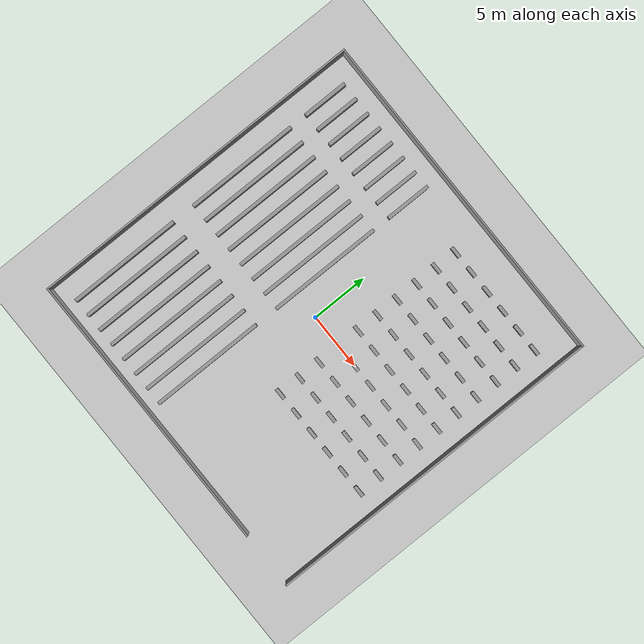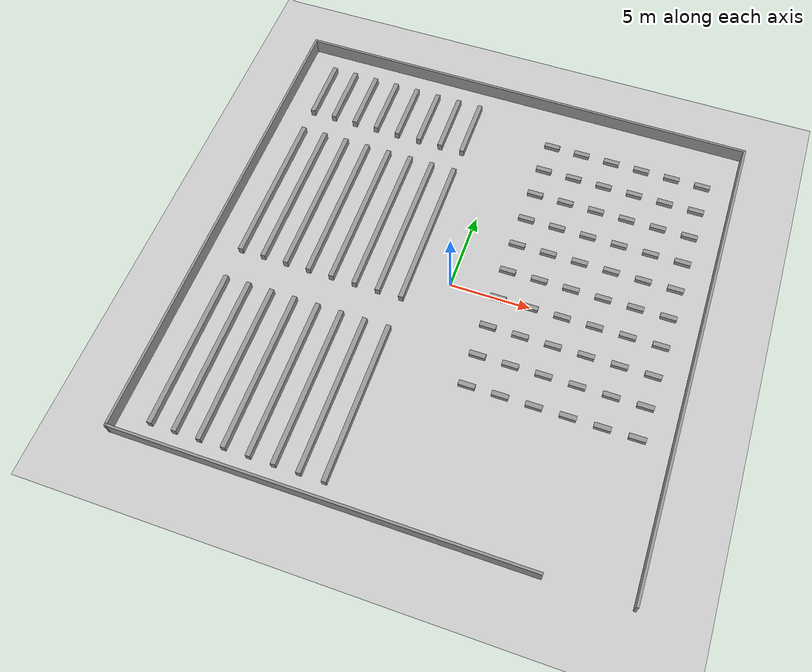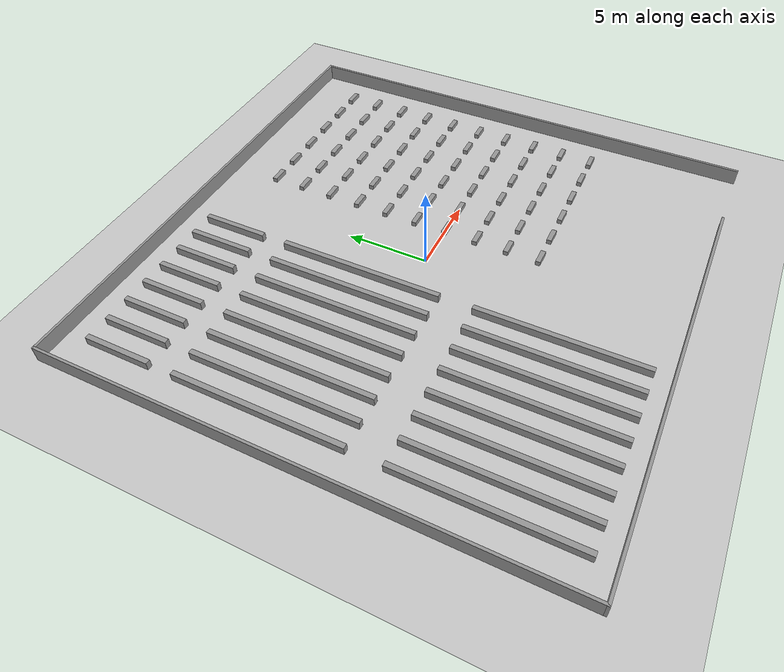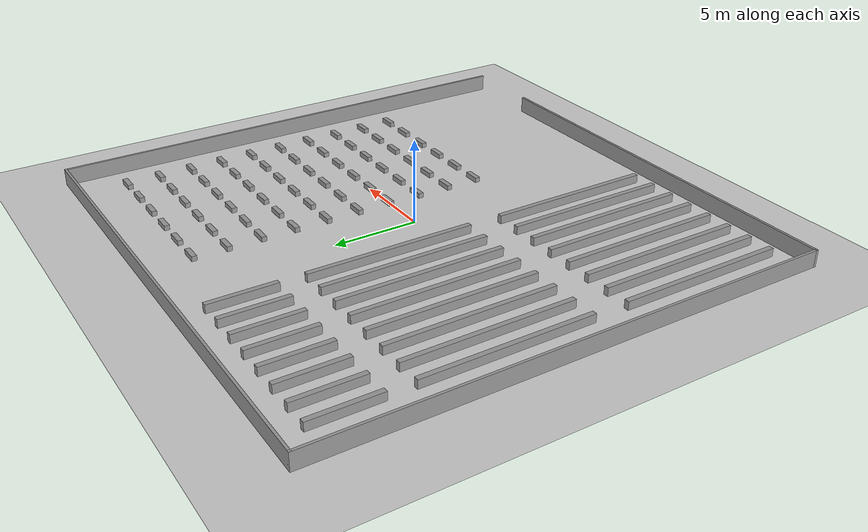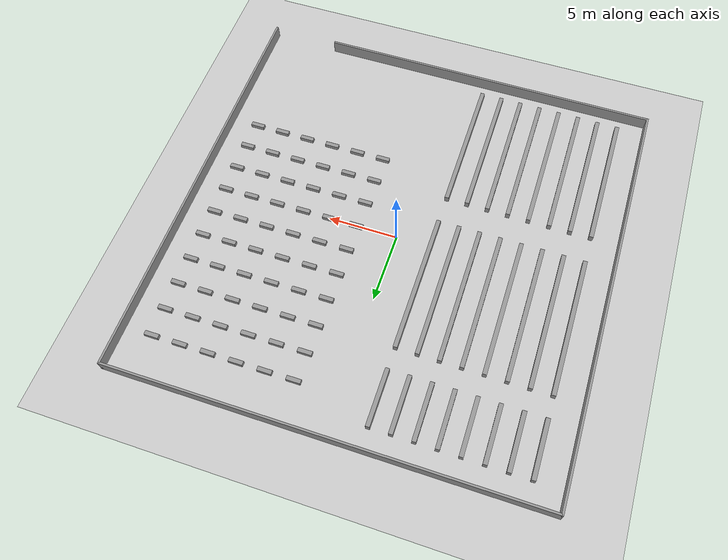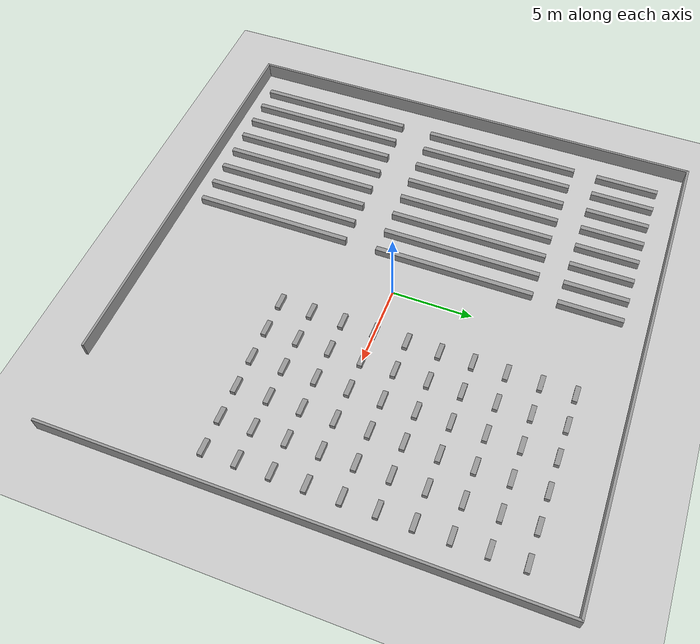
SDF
<sdf version="1.6">
 <world name="default">
  <light name="sun" type="directional">
   <pose>0 0 10 0 -0 0</pose>
   <diffuse>0.8 0.8 0.8 1</diffuse>
   <specular>0.1 0.1 0.1 1</specular>
   <attenuation>
    <range>1000</range>
    <constant>0.9</constant>
    <linear>0.01</linear>
    <quadratic>0.001</quadratic>
   </attenuation>
   <direction>-0.5 0.5 -1</direction>
  </light>
  <model name="ground_plane">
   <static>1</static>
   <link name="link">
    <collision name="collision">
     <geometry><plane><normal>0 0 1</normal><size>100 100</size></plane></geometry>
     <surface><friction><ode><mu>100</mu><mu2>50</mu2></ode></friction></surface>
    </collision>
    <visual name="visual">
     <cast_shadows>0</cast_shadows>
     <geometry><plane><normal>0 0 1</normal><size>100 100</size></plane></geometry>
     <material>
      <script><uri>file://media/materials/scripts/gazebo.material</uri><name>Gazebo/Grey</name></script>
     </material>
    </visual>
   </link>
  </model>
  <gravity>0 0 -9.8</gravity>
  <magnetic_field>6e-06 2.3e-05 -4.2e-05</magnetic_field>
  <atmosphere type="adiabatic"/>
  <physics name="default_physics" default="0" type="ode">
   <max_step_size>0.001</max_step_size>
   <real_time_factor>1</real_time_factor>
   <real_time_update_rate>1000</real_time_update_rate>
  </physics>
  <scene><ambient>0.4 0.4 0.4 1</ambient><background>0.7 0.7 0.7 1</background><shadows>1</shadows></scene>
  <spherical_coordinates>
   <surface_model>EARTH_WGS84</surface_model>
   <latitude_deg>0</latitude_deg>
   <longitude_deg>0</longitude_deg>
   <elevation>0</elevation>
   <heading_deg>0</heading_deg>
  </spherical_coordinates>
  <model name="w1">
   <link name="Wall_0">
    <collision name="Wall_0_Collision">
     <geometry><box><size>25.15 0.15 1</size></box></geometry>
     <pose>0 0 0.5 0 -0 0</pose>
    </collision>
    <visual name="Wall_0_Visual">
     <pose>0 0 0.5 0 -0 0</pose>
     <geometry><box><size>25.15 0.15 1</size></box></geometry>
     <material>
      <script><uri>file://media/materials/scripts/gazebo.material</uri><name>Gazebo/Grey</name></script>
      <ambient>1 1 1 1</ambient>
     </material>
    </visual>
    <pose>-2.5 -15 0 0 -0 3.14159</pose>
   </link>
   <link name="Wall_1">
    <collision name="Wall_1_Collision">
     <geometry><box><size>30.15 0.15 1</size></box></geometry>
     <pose>0 0 0.5 0 -0 0</pose>
    </collision>
    <visual name="Wall_1_Visual">
     <pose>0 0 0.5 0 -0 0</pose>
     <geometry><box><size>30.15 0.15 1</size></box></geometry>
     <material>
      <script><uri>file://media/materials/scripts/gazebo.material</uri><name>Gazebo/Grey</name></script>
      <ambient>1 1 1 1</ambient>
     </material>
    </visual>
    <pose>-15 0 0 0 -0 1.5708</pose>
   </link>
   <link name="Wall_2">
    <collision name="Wall_2_Collision">
     <geometry><box><size>30.15 0.15 1</size></box></geometry>
     <pose>0 0 0.5 0 -0 0</pose>
    </collision>
    <visual name="Wall_2_Visual">
     <pose>0 0 0.5 0 -0 0</pose>
     <geometry><box><size>30.15 0.15 1</size></box></geometry>
     <material>
      <script><uri>file://media/materials/scripts/gazebo.material</uri><name>Gazebo/Grey</name></script>
      <ambient>1 1 1 1</ambient>
     </material>
    </visual>
    <pose>0 15 0 0 -0 0</pose>
   </link>
   <link name="Wall_3">
    <collision name="Wall_3_Collision">
     <geometry><box><size>30.15 0.15 1</size></box></geometry>
     <pose>0 0 0.5 0 -0 0</pose>
    </collision>
    <visual name="Wall_3_Visual">
     <pose>0 0 0.5 0 -0 0</pose>
     <geometry><box><size>30.15 0.15 1</size></box></geometry>
     <material>
      <script><uri>file://media/materials/scripts/gazebo.material</uri><name>Gazebo/Grey</name></script>
      <ambient>1 1 1 1</ambient>
     </material>
    </visual>
    <pose>15 0 0 0 0 -1.5708</pose>
   </link>
   <static>1</static>
  </model>
  <model name="ss1_clone_1_0">
   <link name="link_0">
    <inertial>
     <mass>1</mass>
     <inertia>
      <ixx>0.166667</ixx>
      <ixy>0</ixy>
      <ixz>0</ixz>
      <iyy>0.166667</iyy>
      <iyz>0</iyz>
      <izz>0.166667</izz>
     </inertia>
    </inertial>
    <visual name="visual">
     <geometry><box><size>0.3 10 0.5</size></box></geometry>
     <material>
      <lighting>1</lighting>
      <script><uri>file://media/materials/scripts/gazebo.material</uri><name>Gazebo/Grey</name></script>
      <ambient>0.3 0.3 0.3 1</ambient>
      <diffuse>0.7 0.7 0.7 1</diffuse>
      <specular>0.01 0.01 0.01 1</specular>
      <emissive>0 0 0 1</emissive>
      <shader type="vertex"><normal_map>__default__</normal_map></shader>
     </material>
    </visual>
    <collision name="collision">
     <geometry><box><size>0.3 10 0.5</size></box></geometry>
     <surface>
      <friction>
       <ode><mu>1</mu><mu2>1</mu2><fdir1>0 0 0</fdir1><slip1>0</slip1><slip2>0</slip2></ode>
       <torsional>
        <coefficient>1</coefficient>
        <patch_radius>0</patch_radius>
        <surface_radius>0</surface_radius>
        <use_patch_radius>1</use_patch_radius>
        <ode><slip>0</slip></ode>
       </torsional>
      </friction>
      <bounce><restitution_coefficient>0</restitution_coefficient><threshold>1e+06</threshold></bounce>
      <contact>
       <collide_without_contact>0</collide_without_contact>
       <collide_without_contact_bitmask>1</collide_without_contact_bitmask>
       <collide_bitmask>1</collide_bitmask>
       <ode>
        <soft_cfm>0</soft_cfm>
        <soft_erp>0.2</soft_erp>
        <kp>1e+13</kp>
        <kd>1</kd>
        <max_vel>0.01</max_vel>
        <min_depth>0</min_depth>
       </ode>
       <bullet>
        <split_impulse>1</split_impulse>
        <split_impulse_penetration_threshold>-0.01</split_impulse_penetration_threshold>
        <soft_cfm>0</soft_cfm>
        <soft_erp>0.2</soft_erp>
        <kp>1e+13</kp>
        <kd>1</kd>
       </bullet>
      </contact>
     </surface>
    </collision>
   </link>
   <static>0</static>
   <pose>-13 -9 0.25 0 -0 0</pose>
  </model>
  <model name="ss1_clone_1_0_clone_0">
   <link name="link_0">
    <inertial>
     <mass>1</mass>
     <inertia>
      <ixx>0.166667</ixx>
      <ixy>0</ixy>
      <ixz>0</ixz>
      <iyy>0.166667</iyy>
      <iyz>0</iyz>
      <izz>0.166667</izz>
     </inertia>
    </inertial>
    <visual name="visual">
     <geometry><box><size>0.3 10 0.5</size></box></geometry>
     <material>
      <lighting>1</lighting>
      <script><uri>file://media/materials/scripts/gazebo.material</uri><name>Gazebo/Grey</name></script>
      <ambient>0.3 0.3 0.3 1</ambient>
      <diffuse>0.7 0.7 0.7 1</diffuse>
      <specular>0.01 0.01 0.01 1</specular>
      <emissive>0 0 0 1</emissive>
      <shader type="vertex"><normal_map>__default__</normal_map></shader>
     </material>
    </visual>
    <collision name="collision">
     <geometry><box><size>0.3 10 0.5</size></box></geometry>
     <surface>
      <friction>
       <ode><mu>1</mu><mu2>1</mu2><fdir1>0 0 0</fdir1><slip1>0</slip1><slip2>0</slip2></ode>
       <torsional>
        <coefficient>1</coefficient>
        <patch_radius>0</patch_radius>
        <surface_radius>0</surface_radius>
        <use_patch_radius>1</use_patch_radius>
        <ode><slip>0</slip></ode>
       </torsional>
      </friction>
      <bounce><restitution_coefficient>0</restitution_coefficient><threshold>1e+06</threshold></bounce>
      <contact>
       <collide_without_contact>0</collide_without_contact>
       <collide_without_contact_bitmask>1</collide_without_contact_bitmask>
       <collide_bitmask>1</collide_bitmask>
       <ode>
        <soft_cfm>0</soft_cfm>
        <soft_erp>0.2</soft_erp>
        <kp>1e+13</kp>
        <kd>1</kd>
        <max_vel>0.01</max_vel>
        <min_depth>0</min_depth>
       </ode>
       <bullet>
        <split_impulse>1</split_impulse>
        <split_impulse_penetration_threshold>-0.01</split_impulse_penetration_threshold>
        <soft_cfm>0</soft_cfm>
        <soft_erp>0.2</soft_erp>
        <kp>1e+13</kp>
        <kd>1</kd>
       </bullet>
      </contact>
     </surface>
    </collision>
   </link>
   <static>0</static>
   <pose>-11.5 -9 0.25 0 -0 0</pose>
  </model>
  <model name="ss1_clone_1_0_clone_1">
   <link name="link_0">
    <inertial>
     <mass>1</mass>
     <inertia>
      <ixx>0.166667</ixx>
      <ixy>0</ixy>
      <ixz>0</ixz>
      <iyy>0.166667</iyy>
      <iyz>0</iyz>
      <izz>0.166667</izz>
     </inertia>
    </inertial>
    <visual name="visual">
     <geometry><box><size>0.3 10 0.5</size></box></geometry>
     <material>
      <lighting>1</lighting>
      <script><uri>file://media/materials/scripts/gazebo.material</uri><name>Gazebo/Grey</name></script>
      <ambient>0.3 0.3 0.3 1</ambient>
      <diffuse>0.7 0.7 0.7 1</diffuse>
      <specular>0.01 0.01 0.01 1</specular>
      <emissive>0 0 0 1</emissive>
      <shader type="vertex"><normal_map>__default__</normal_map></shader>
     </material>
    </visual>
    <collision name="collision">
     <geometry><box><size>0.3 10 0.5</size></box></geometry>
     <surface>
      <friction>
       <ode><mu>1</mu><mu2>1</mu2><fdir1>0 0 0</fdir1><slip1>0</slip1><slip2>0</slip2></ode>
       <torsional>
        <coefficient>1</coefficient>
        <patch_radius>0</patch_radius>
        <surface_radius>0</surface_radius>
        <use_patch_radius>1</use_patch_radius>
        <ode><slip>0</slip></ode>
       </torsional>
      </friction>
      <bounce><restitution_coefficient>0</restitution_coefficient><threshold>1e+06</threshold></bounce>
      <contact>
       <collide_without_contact>0</collide_without_contact>
       <collide_without_contact_bitmask>1</collide_without_contact_bitmask>
       <collide_bitmask>1</collide_bitmask>
       <ode>
        <soft_cfm>0</soft_cfm>
        <soft_erp>0.2</soft_erp>
        <kp>1e+13</kp>
        <kd>1</kd>
        <max_vel>0.01</max_vel>
        <min_depth>0</min_depth>
       </ode>
       <bullet>
        <split_impulse>1</split_impulse>
        <split_impulse_penetration_threshold>-0.01</split_impulse_penetration_threshold>
        <soft_cfm>0</soft_cfm>
        <soft_erp>0.2</soft_erp>
        <kp>1e+13</kp>
        <kd>1</kd>
       </bullet>
      </contact>
     </surface>
    </collision>
   </link>
   <static>0</static>
   <pose>-11.5 3 0.25 0 -0 0</pose>
  </model>
  <model name="ss1_clone_1_0_clone_2">
   <link name="link_0">
    <inertial>
     <mass>1</mass>
     <inertia>
      <ixx>0.166667</ixx>
      <ixy>0</ixy>
      <ixz>0</ixz>
      <iyy>0.166667</iyy>
      <iyz>0</iyz>
      <izz>0.166667</izz>
     </inertia>
    </inertial>
    <visual name="visual">
     <geometry><box><size>0.3 10 0.5</size></box></geometry>
     <material>
      <lighting>1</lighting>
      <script><uri>file://media/materials/scripts/gazebo.material</uri><name>Gazebo/Grey</name></script>
      <ambient>0.3 0.3 0.3 1</ambient>
      <diffuse>0.7 0.7 0.7 1</diffuse>
      <specular>0.01 0.01 0.01 1</specular>
      <emissive>0 0 0 1</emissive>
      <shader type="vertex"><normal_map>__default__</normal_map></shader>
     </material>
    </visual>
    <collision name="collision">
     <geometry><box><size>0.3 10 0.5</size></box></geometry>
     <surface>
      <friction>
       <ode><mu>1</mu><mu2>1</mu2><fdir1>0 0 0</fdir1><slip1>0</slip1><slip2>0</slip2></ode>
       <torsional>
        <coefficient>1</coefficient>
        <patch_radius>0</patch_radius>
        <surface_radius>0</surface_radius>
        <use_patch_radius>1</use_patch_radius>
        <ode><slip>0</slip></ode>
       </torsional>
      </friction>
      <bounce><restitution_coefficient>0</restitution_coefficient><threshold>1e+06</threshold></bounce>
      <contact>
       <collide_without_contact>0</collide_without_contact>
       <collide_without_contact_bitmask>1</collide_without_contact_bitmask>
       <collide_bitmask>1</collide_bitmask>
       <ode>
        <soft_cfm>0</soft_cfm>
        <soft_erp>0.2</soft_erp>
        <kp>1e+13</kp>
        <kd>1</kd>
        <max_vel>0.01</max_vel>
        <min_depth>0</min_depth>
       </ode>
       <bullet>
        <split_impulse>1</split_impulse>
        <split_impulse_penetration_threshold>-0.01</split_impulse_penetration_threshold>
        <soft_cfm>0</soft_cfm>
        <soft_erp>0.2</soft_erp>
        <kp>1e+13</kp>
        <kd>1</kd>
       </bullet>
      </contact>
     </surface>
    </collision>
   </link>
   <static>0</static>
   <pose>-10 3 0.25 0 -0 0</pose>
  </model>
  <model name="ss1_clone_1_0_clone_3">
   <link name="link_0">
    <inertial>
     <mass>1</mass>
     <inertia>
      <ixx>0.166667</ixx>
      <ixy>0</ixy>
      <ixz>0</ixz>
      <iyy>0.166667</iyy>
      <iyz>0</iyz>
      <izz>0.166667</izz>
     </inertia>
    </inertial>
    <visual name="visual">
     <geometry><box><size>0.3 10 0.5</size></box></geometry>
     <material>
      <lighting>1</lighting>
      <script><uri>file://media/materials/scripts/gazebo.material</uri><name>Gazebo/Grey</name></script>
      <ambient>0.3 0.3 0.3 1</ambient>
      <diffuse>0.7 0.7 0.7 1</diffuse>
      <specular>0.01 0.01 0.01 1</specular>
      <emissive>0 0 0 1</emissive>
      <shader type="vertex"><normal_map>__default__</normal_map></shader>
     </material>
    </visual>
    <collision name="collision">
     <geometry><box><size>0.3 10 0.5</size></box></geometry>
     <surface>
      <friction>
       <ode><mu>1</mu><mu2>1</mu2><fdir1>0 0 0</fdir1><slip1>0</slip1><slip2>0</slip2></ode>
       <torsional>
        <coefficient>1</coefficient>
        <patch_radius>0</patch_radius>
        <surface_radius>0</surface_radius>
        <use_patch_radius>1</use_patch_radius>
        <ode><slip>0</slip></ode>
       </torsional>
      </friction>
      <bounce><restitution_coefficient>0</restitution_coefficient><threshold>1e+06</threshold></bounce>
      <contact>
       <collide_without_contact>0</collide_without_contact>
       <collide_without_contact_bitmask>1</collide_without_contact_bitmask>
       <collide_bitmask>1</collide_bitmask>
       <ode>
        <soft_cfm>0</soft_cfm>
        <soft_erp>0.2</soft_erp>
        <kp>1e+13</kp>
        <kd>1</kd>
        <max_vel>0.01</max_vel>
        <min_depth>0</min_depth>
       </ode>
       <bullet>
        <split_impulse>1</split_impulse>
        <split_impulse_penetration_threshold>-0.01</split_impulse_penetration_threshold>
        <soft_cfm>0</soft_cfm>
        <soft_erp>0.2</soft_erp>
        <kp>1e+13</kp>
        <kd>1</kd>
       </bullet>
      </contact>
     </surface>
    </collision>
   </link>
   <static>0</static>
   <pose>-8.5 3 0.25 0 -0 0</pose>
  </model>
  <model name="ss1_clone_1_0_clone_4">
   <link name="link_0">
    <inertial>
     <mass>1</mass>
     <inertia>
      <ixx>0.166667</ixx>
      <ixy>0</ixy>
      <ixz>0</ixz>
      <iyy>0.166667</iyy>
      <iyz>0</iyz>
      <izz>0.166667</izz>
     </inertia>
    </inertial>
    <visual name="visual">
     <geometry><box><size>0.3 10 0.5</size></box></geometry>
     <material>
      <lighting>1</lighting>
      <script><uri>file://media/materials/scripts/gazebo.material</uri><name>Gazebo/Grey</name></script>
      <ambient>0.3 0.3 0.3 1</ambient>
      <diffuse>0.7 0.7 0.7 1</diffuse>
      <specular>0.01 0.01 0.01 1</specular>
      <emissive>0 0 0 1</emissive>
      <shader type="vertex"><normal_map>__default__</normal_map></shader>
     </material>
    </visual>
    <collision name="collision">
     <geometry><box><size>0.3 10 0.5</size></box></geometry>
     <surface>
      <friction>
       <ode><mu>1</mu><mu2>1</mu2><fdir1>0 0 0</fdir1><slip1>0</slip1><slip2>0</slip2></ode>
       <torsional>
        <coefficient>1</coefficient>
        <patch_radius>0</patch_radius>
        <surface_radius>0</surface_radius>
        <use_patch_radius>1</use_patch_radius>
        <ode><slip>0</slip></ode>
       </torsional>
      </friction>
      <bounce><restitution_coefficient>0</restitution_coefficient><threshold>1e+06</threshold></bounce>
      <contact>
       <collide_without_contact>0</collide_without_contact>
       <collide_without_contact_bitmask>1</collide_without_contact_bitmask>
       <collide_bitmask>1</collide_bitmask>
       <ode>
        <soft_cfm>0</soft_cfm>
        <soft_erp>0.2</soft_erp>
        <kp>1e+13</kp>
        <kd>1</kd>
        <max_vel>0.01</max_vel>
        <min_depth>0</min_depth>
       </ode>
       <bullet>
        <split_impulse>1</split_impulse>
        <split_impulse_penetration_threshold>-0.01</split_impulse_penetration_threshold>
        <soft_cfm>0</soft_cfm>
        <soft_erp>0.2</soft_erp>
        <kp>1e+13</kp>
        <kd>1</kd>
       </bullet>
      </contact>
     </surface>
    </collision>
   </link>
   <static>0</static>
   <pose>-7 3 0.25 0 -0 0</pose>
  </model>
  <model name="ss1_clone_1_0_clone_5">
   <link name="link_0">
    <inertial>
     <mass>1</mass>
     <inertia>
      <ixx>0.166667</ixx>
      <ixy>0</ixy>
      <ixz>0</ixz>
      <iyy>0.166667</iyy>
      <iyz>0</iyz>
      <izz>0.166667</izz>
     </inertia>
    </inertial>
    <visual name="visual">
     <geometry><box><size>0.3 10 0.5</size></box></geometry>
     <material>
      <lighting>1</lighting>
      <script><uri>file://media/materials/scripts/gazebo.material</uri><name>Gazebo/Grey</name></script>
      <ambient>0.3 0.3 0.3 1</ambient>
      <diffuse>0.7 0.7 0.7 1</diffuse>
      <specular>0.01 0.01 0.01 1</specular>
      <emissive>0 0 0 1</emissive>
      <shader type="vertex"><normal_map>__default__</normal_map></shader>
     </material>
    </visual>
    <collision name="collision">
     <geometry><box><size>0.3 10 0.5</size></box></geometry>
     <surface>
      <friction>
       <ode><mu>1</mu><mu2>1</mu2><fdir1>0 0 0</fdir1><slip1>0</slip1><slip2>0</slip2></ode>
       <torsional>
        <coefficient>1</coefficient>
        <patch_radius>0</patch_radius>
        <surface_radius>0</surface_radius>
        <use_patch_radius>1</use_patch_radius>
        <ode><slip>0</slip></ode>
       </torsional>
      </friction>
      <bounce><restitution_coefficient>0</restitution_coefficient><threshold>1e+06</threshold></bounce>
      <contact>
       <collide_without_contact>0</collide_without_contact>
       <collide_without_contact_bitmask>1</collide_without_contact_bitmask>
       <collide_bitmask>1</collide_bitmask>
       <ode>
        <soft_cfm>0</soft_cfm>
        <soft_erp>0.2</soft_erp>
        <kp>1e+13</kp>
        <kd>1</kd>
        <max_vel>0.01</max_vel>
        <min_depth>0</min_depth>
       </ode>
       <bullet>
        <split_impulse>1</split_impulse>
        <split_impulse_penetration_threshold>-0.01</split_impulse_penetration_threshold>
        <soft_cfm>0</soft_cfm>
        <soft_erp>0.2</soft_erp>
        <kp>1e+13</kp>
        <kd>1</kd>
       </bullet>
      </contact>
     </surface>
    </collision>
   </link>
   <static>0</static>
   <pose>-5.5 3 0.25 0 -0 0</pose>
  </model>
  <model name="ss1_clone_1_0_clone_6">
   <link name="link_0">
    <inertial>
     <mass>1</mass>
     <inertia>
      <ixx>0.166667</ixx>
      <ixy>0</ixy>
      <ixz>0</ixz>
      <iyy>0.166667</iyy>
      <iyz>0</iyz>
      <izz>0.166667</izz>
     </inertia>
    </inertial>
    <visual name="visual">
     <geometry><box><size>0.3 10 0.5</size></box></geometry>
     <material>
      <lighting>1</lighting>
      <script><uri>file://media/materials/scripts/gazebo.material</uri><name>Gazebo/Grey</name></script>
      <ambient>0.3 0.3 0.3 1</ambient>
      <diffuse>0.7 0.7 0.7 1</diffuse>
      <specular>0.01 0.01 0.01 1</specular>
      <emissive>0 0 0 1</emissive>
      <shader type="vertex"><normal_map>__default__</normal_map></shader>
     </material>
    </visual>
    <collision name="collision">
     <geometry><box><size>0.3 10 0.5</size></box></geometry>
     <surface>
      <friction>
       <ode><mu>1</mu><mu2>1</mu2><fdir1>0 0 0</fdir1><slip1>0</slip1><slip2>0</slip2></ode>
       <torsional>
        <coefficient>1</coefficient>
        <patch_radius>0</patch_radius>
        <surface_radius>0</surface_radius>
        <use_patch_radius>1</use_patch_radius>
        <ode><slip>0</slip></ode>
       </torsional>
      </friction>
      <bounce><restitution_coefficient>0</restitution_coefficient><threshold>1e+06</threshold></bounce>
      <contact>
       <collide_without_contact>0</collide_without_contact>
       <collide_without_contact_bitmask>1</collide_without_contact_bitmask>
       <collide_bitmask>1</collide_bitmask>
       <ode>
        <soft_cfm>0</soft_cfm>
        <soft_erp>0.2</soft_erp>
        <kp>1e+13</kp>
        <kd>1</kd>
        <max_vel>0.01</max_vel>
        <min_depth>0</min_depth>
       </ode>
       <bullet>
        <split_impulse>1</split_impulse>
        <split_impulse_penetration_threshold>-0.01</split_impulse_penetration_threshold>
        <soft_cfm>0</soft_cfm>
        <soft_erp>0.2</soft_erp>
        <kp>1e+13</kp>
        <kd>1</kd>
       </bullet>
      </contact>
     </surface>
    </collision>
   </link>
   <static>0</static>
   <pose>-4 3 0.25 0 -0 0</pose>
  </model>
  <model name="ss1_clone_1_0_clone_7">
   <link name="link_0">
    <inertial>
     <mass>1</mass>
     <inertia>
      <ixx>0.166667</ixx>
      <ixy>0</ixy>
      <ixz>0</ixz>
      <iyy>0.166667</iyy>
      <iyz>0</iyz>
      <izz>0.166667</izz>
     </inertia>
    </inertial>
    <visual name="visual">
     <geometry><box><size>0.3 10 0.5</size></box></geometry>
     <material>
      <lighting>1</lighting>
      <script><uri>file://media/materials/scripts/gazebo.material</uri><name>Gazebo/Grey</name></script>
      <ambient>0.3 0.3 0.3 1</ambient>
      <diffuse>0.7 0.7 0.7 1</diffuse>
      <specular>0.01 0.01 0.01 1</specular>
      <emissive>0 0 0 1</emissive>
      <shader type="vertex"><normal_map>__default__</normal_map></shader>
     </material>
    </visual>
    <collision name="collision">
     <geometry><box><size>0.3 10 0.5</size></box></geometry>
     <surface>
      <friction>
       <ode><mu>1</mu><mu2>1</mu2><fdir1>0 0 0</fdir1><slip1>0</slip1><slip2>0</slip2></ode>
       <torsional>
        <coefficient>1</coefficient>
        <patch_radius>0</patch_radius>
        <surface_radius>0</surface_radius>
        <use_patch_radius>1</use_patch_radius>
        <ode><slip>0</slip></ode>
       </torsional>
      </friction>
      <bounce><restitution_coefficient>0</restitution_coefficient><threshold>1e+06</threshold></bounce>
      <contact>
       <collide_without_contact>0</collide_without_contact>
       <collide_without_contact_bitmask>1</collide_without_contact_bitmask>
       <collide_bitmask>1</collide_bitmask>
       <ode>
        <soft_cfm>0</soft_cfm>
        <soft_erp>0.2</soft_erp>
        <kp>1e+13</kp>
        <kd>1</kd>
        <max_vel>0.01</max_vel>
        <min_depth>0</min_depth>
       </ode>
       <bullet>
        <split_impulse>1</split_impulse>
        <split_impulse_penetration_threshold>-0.01</split_impulse_penetration_threshold>
        <soft_cfm>0</soft_cfm>
        <soft_erp>0.2</soft_erp>
        <kp>1e+13</kp>
        <kd>1</kd>
       </bullet>
      </contact>
     </surface>
    </collision>
   </link>
   <static>0</static>
   <pose>-2.5 3 0.25 0 -0 0</pose>
  </model>
  <model name="ss1_clone_1_0_clone_8">
   <link name="link_0">
    <inertial>
     <mass>1</mass>
     <inertia>
      <ixx>0.166667</ixx>
      <ixy>0</ixy>
      <ixz>0</ixz>
      <iyy>0.166667</iyy>
      <iyz>0</iyz>
      <izz>0.166667</izz>
     </inertia>
    </inertial>
    <visual name="visual">
     <geometry><box><size>0.3 10 0.5</size></box></geometry>
     <material>
      <lighting>1</lighting>
      <script><uri>file://media/materials/scripts/gazebo.material</uri><name>Gazebo/Grey</name></script>
      <ambient>0.3 0.3 0.3 1</ambient>
      <diffuse>0.7 0.7 0.7 1</diffuse>
      <specular>0.01 0.01 0.01 1</specular>
      <emissive>0 0 0 1</emissive>
      <shader type="vertex"><normal_map>__default__</normal_map></shader>
     </material>
    </visual>
    <collision name="collision">
     <geometry><box><size>0.3 10 0.5</size></box></geometry>
     <surface>
      <friction>
       <ode><mu>1</mu><mu2>1</mu2><fdir1>0 0 0</fdir1><slip1>0</slip1><slip2>0</slip2></ode>
       <torsional>
        <coefficient>1</coefficient>
        <patch_radius>0</patch_radius>
        <surface_radius>0</surface_radius>
        <use_patch_radius>1</use_patch_radius>
        <ode><slip>0</slip></ode>
       </torsional>
      </friction>
      <bounce><restitution_coefficient>0</restitution_coefficient><threshold>1e+06</threshold></bounce>
      <contact>
       <collide_without_contact>0</collide_without_contact>
       <collide_without_contact_bitmask>1</collide_without_contact_bitmask>
       <collide_bitmask>1</collide_bitmask>
       <ode>
        <soft_cfm>0</soft_cfm>
        <soft_erp>0.2</soft_erp>
        <kp>1e+13</kp>
        <kd>1</kd>
        <max_vel>0.01</max_vel>
        <min_depth>0</min_depth>
       </ode>
       <bullet>
        <split_impulse>1</split_impulse>
        <split_impulse_penetration_threshold>-0.01</split_impulse_penetration_threshold>
        <soft_cfm>0</soft_cfm>
        <soft_erp>0.2</soft_erp>
        <kp>1e+13</kp>
        <kd>1</kd>
       </bullet>
      </contact>
     </surface>
    </collision>
   </link>
   <static>0</static>
   <pose>-10 -9 0.25 0 -0 0</pose>
  </model>
  <model name="ss1_clone_1_0_clone_9">
   <link name="link_0">
    <inertial>
     <mass>1</mass>
     <inertia>
      <ixx>0.166667</ixx>
      <ixy>0</ixy>
      <ixz>0</ixz>
      <iyy>0.166667</iyy>
      <iyz>0</iyz>
      <izz>0.166667</izz>
     </inertia>
    </inertial>
    <visual name="visual">
     <geometry><box><size>0.3 10 0.5</size></box></geometry>
     <material>
      <lighting>1</lighting>
      <script><uri>file://media/materials/scripts/gazebo.material</uri><name>Gazebo/Grey</name></script>
      <ambient>0.3 0.3 0.3 1</ambient>
      <diffuse>0.7 0.7 0.7 1</diffuse>
      <specular>0.01 0.01 0.01 1</specular>
      <emissive>0 0 0 1</emissive>
      <shader type="vertex"><normal_map>__default__</normal_map></shader>
     </material>
    </visual>
    <collision name="collision">
     <geometry><box><size>0.3 10 0.5</size></box></geometry>
     <surface>
      <friction>
       <ode><mu>1</mu><mu2>1</mu2><fdir1>0 0 0</fdir1><slip1>0</slip1><slip2>0</slip2></ode>
       <torsional>
        <coefficient>1</coefficient>
        <patch_radius>0</patch_radius>
        <surface_radius>0</surface_radius>
        <use_patch_radius>1</use_patch_radius>
        <ode><slip>0</slip></ode>
       </torsional>
      </friction>
      <bounce><restitution_coefficient>0</restitution_coefficient><threshold>1e+06</threshold></bounce>
      <contact>
       <collide_without_contact>0</collide_without_contact>
       <collide_without_contact_bitmask>1</collide_without_contact_bitmask>
       <collide_bitmask>1</collide_bitmask>
       <ode>
        <soft_cfm>0</soft_cfm>
        <soft_erp>0.2</soft_erp>
        <kp>1e+13</kp>
        <kd>1</kd>
        <max_vel>0.01</max_vel>
        <min_depth>0</min_depth>
       </ode>
       <bullet>
        <split_impulse>1</split_impulse>
        <split_impulse_penetration_threshold>-0.01</split_impulse_penetration_threshold>
        <soft_cfm>0</soft_cfm>
        <soft_erp>0.2</soft_erp>
        <kp>1e+13</kp>
        <kd>1</kd>
       </bullet>
      </contact>
     </surface>
    </collision>
   </link>
   <static>0</static>
   <pose>-8.5 -9 0.25 0 -0 0</pose>
  </model>
  <model name="ss1_clone_1_0_clone_10">
   <link name="link_0">
    <inertial>
     <mass>1</mass>
     <inertia>
      <ixx>0.166667</ixx>
      <ixy>0</ixy>
      <ixz>0</ixz>
      <iyy>0.166667</iyy>
      <iyz>0</iyz>
      <izz>0.166667</izz>
     </inertia>
    </inertial>
    <visual name="visual">
     <geometry><box><size>0.3 10 0.5</size></box></geometry>
     <material>
      <lighting>1</lighting>
      <script><uri>file://media/materials/scripts/gazebo.material</uri><name>Gazebo/Grey</name></script>
      <ambient>0.3 0.3 0.3 1</ambient>
      <diffuse>0.7 0.7 0.7 1</diffuse>
      <specular>0.01 0.01 0.01 1</specular>
      <emissive>0 0 0 1</emissive>
      <shader type="vertex"><normal_map>__default__</normal_map></shader>
     </material>
    </visual>
    <collision name="collision">
     <geometry><box><size>0.3 10 0.5</size></box></geometry>
     <surface>
      <friction>
       <ode><mu>1</mu><mu2>1</mu2><fdir1>0 0 0</fdir1><slip1>0</slip1><slip2>0</slip2></ode>
       <torsional>
        <coefficient>1</coefficient>
        <patch_radius>0</patch_radius>
        <surface_radius>0</surface_radius>
        <use_patch_radius>1</use_patch_radius>
        <ode><slip>0</slip></ode>
       </torsional>
      </friction>
      <bounce><restitution_coefficient>0</restitution_coefficient><threshold>1e+06</threshold></bounce>
      <contact>
       <collide_without_contact>0</collide_without_contact>
       <collide_without_contact_bitmask>1</collide_without_contact_bitmask>
       <collide_bitmask>1</collide_bitmask>
       <ode>
        <soft_cfm>0</soft_cfm>
        <soft_erp>0.2</soft_erp>
        <kp>1e+13</kp>
        <kd>1</kd>
        <max_vel>0.01</max_vel>
        <min_depth>0</min_depth>
       </ode>
       <bullet>
        <split_impulse>1</split_impulse>
        <split_impulse_penetration_threshold>-0.01</split_impulse_penetration_threshold>
        <soft_cfm>0</soft_cfm>
        <soft_erp>0.2</soft_erp>
        <kp>1e+13</kp>
        <kd>1</kd>
       </bullet>
      </contact>
     </surface>
    </collision>
   </link>
   <static>0</static>
   <pose>-7 -9 0.25 0 -0 0</pose>
  </model>
  <model name="ss1_clone_1_0_clone_11">
   <link name="link_0">
    <inertial>
     <mass>1</mass>
     <inertia>
      <ixx>0.166667</ixx>
      <ixy>0</ixy>
      <ixz>0</ixz>
      <iyy>0.166667</iyy>
      <iyz>0</iyz>
      <izz>0.166667</izz>
     </inertia>
    </inertial>
    <visual name="visual">
     <geometry><box><size>0.3 10 0.5</size></box></geometry>
     <material>
      <lighting>1</lighting>
      <script><uri>file://media/materials/scripts/gazebo.material</uri><name>Gazebo/Grey</name></script>
      <ambient>0.3 0.3 0.3 1</ambient>
      <diffuse>0.7 0.7 0.7 1</diffuse>
      <specular>0.01 0.01 0.01 1</specular>
      <emissive>0 0 0 1</emissive>
      <shader type="vertex"><normal_map>__default__</normal_map></shader>
     </material>
    </visual>
    <collision name="collision">
     <geometry><box><size>0.3 10 0.5</size></box></geometry>
     <surface>
      <friction>
       <ode><mu>1</mu><mu2>1</mu2><fdir1>0 0 0</fdir1><slip1>0</slip1><slip2>0</slip2></ode>
       <torsional>
        <coefficient>1</coefficient>
        <patch_radius>0</patch_radius>
        <surface_radius>0</surface_radius>
        <use_patch_radius>1</use_patch_radius>
        <ode><slip>0</slip></ode>
       </torsional>
      </friction>
      <bounce><restitution_coefficient>0</restitution_coefficient><threshold>1e+06</threshold></bounce>
      <contact>
       <collide_without_contact>0</collide_without_contact>
       <collide_without_contact_bitmask>1</collide_without_contact_bitmask>
       <collide_bitmask>1</collide_bitmask>
       <ode>
        <soft_cfm>0</soft_cfm>
        <soft_erp>0.2</soft_erp>
        <kp>1e+13</kp>
        <kd>1</kd>
        <max_vel>0.01</max_vel>
        <min_depth>0</min_depth>
       </ode>
       <bullet>
        <split_impulse>1</split_impulse>
        <split_impulse_penetration_threshold>-0.01</split_impulse_penetration_threshold>
        <soft_cfm>0</soft_cfm>
        <soft_erp>0.2</soft_erp>
        <kp>1e+13</kp>
        <kd>1</kd>
       </bullet>
      </contact>
     </surface>
    </collision>
   </link>
   <static>0</static>
   <pose>-5.5 -9 0.25 0 -0 0</pose>
  </model>
  <model name="ss1_clone_1_0_clone_12">
   <link name="link_0">
    <inertial>
     <mass>1</mass>
     <inertia>
      <ixx>0.166667</ixx>
      <ixy>0</ixy>
      <ixz>0</ixz>
      <iyy>0.166667</iyy>
      <iyz>0</iyz>
      <izz>0.166667</izz>
     </inertia>
    </inertial>
    <visual name="visual">
     <geometry><box><size>0.3 10 0.5</size></box></geometry>
     <material>
      <lighting>1</lighting>
      <script><uri>file://media/materials/scripts/gazebo.material</uri><name>Gazebo/Grey</name></script>
      <ambient>0.3 0.3 0.3 1</ambient>
      <diffuse>0.7 0.7 0.7 1</diffuse>
      <specular>0.01 0.01 0.01 1</specular>
      <emissive>0 0 0 1</emissive>
      <shader type="vertex"><normal_map>__default__</normal_map></shader>
     </material>
    </visual>
    <collision name="collision">
     <geometry><box><size>0.3 10 0.5</size></box></geometry>
     <surface>
      <friction>
       <ode><mu>1</mu><mu2>1</mu2><fdir1>0 0 0</fdir1><slip1>0</slip1><slip2>0</slip2></ode>
       <torsional>
        <coefficient>1</coefficient>
        <patch_radius>0</patch_radius>
        <surface_radius>0</surface_radius>
        <use_patch_radius>1</use_patch_radius>
        <ode><slip>0</slip></ode>
       </torsional>
      </friction>
      <bounce><restitution_coefficient>0</restitution_coefficient><threshold>1e+06</threshold></bounce>
      <contact>
       <collide_without_contact>0</collide_without_contact>
       <collide_without_contact_bitmask>1</collide_without_contact_bitmask>
       <collide_bitmask>1</collide_bitmask>
       <ode>
        <soft_cfm>0</soft_cfm>
        <soft_erp>0.2</soft_erp>
        <kp>1e+13</kp>
        <kd>1</kd>
        <max_vel>0.01</max_vel>
        <min_depth>0</min_depth>
       </ode>
       <bullet>
        <split_impulse>1</split_impulse>
        <split_impulse_penetration_threshold>-0.01</split_impulse_penetration_threshold>
        <soft_cfm>0</soft_cfm>
        <soft_erp>0.2</soft_erp>
        <kp>1e+13</kp>
        <kd>1</kd>
       </bullet>
      </contact>
     </surface>
    </collision>
   </link>
   <static>0</static>
   <pose>-4 -9 0.25 0 -0 0</pose>
  </model>
  <model name="ss1_clone_1_0_clone_13">
   <link name="link_0">
    <inertial>
     <mass>1</mass>
     <inertia>
      <ixx>0.166667</ixx>
      <ixy>0</ixy>
      <ixz>0</ixz>
      <iyy>0.166667</iyy>
      <iyz>0</iyz>
      <izz>0.166667</izz>
     </inertia>
    </inertial>
    <visual name="visual">
     <geometry><box><size>0.3 10 0.5</size></box></geometry>
     <material>
      <lighting>1</lighting>
      <script><uri>file://media/materials/scripts/gazebo.material</uri><name>Gazebo/Grey</name></script>
      <ambient>0.3 0.3 0.3 1</ambient>
      <diffuse>0.7 0.7 0.7 1</diffuse>
      <specular>0.01 0.01 0.01 1</specular>
      <emissive>0 0 0 1</emissive>
      <shader type="vertex"><normal_map>__default__</normal_map></shader>
     </material>
    </visual>
    <collision name="collision">
     <geometry><box><size>0.3 10 0.5</size></box></geometry>
     <surface>
      <friction>
       <ode><mu>1</mu><mu2>1</mu2><fdir1>0 0 0</fdir1><slip1>0</slip1><slip2>0</slip2></ode>
       <torsional>
        <coefficient>1</coefficient>
        <patch_radius>0</patch_radius>
        <surface_radius>0</surface_radius>
        <use_patch_radius>1</use_patch_radius>
        <ode><slip>0</slip></ode>
       </torsional>
      </friction>
      <bounce><restitution_coefficient>0</restitution_coefficient><threshold>1e+06</threshold></bounce>
      <contact>
       <collide_without_contact>0</collide_without_contact>
       <collide_without_contact_bitmask>1</collide_without_contact_bitmask>
       <collide_bitmask>1</collide_bitmask>
       <ode>
        <soft_cfm>0</soft_cfm>
        <soft_erp>0.2</soft_erp>
        <kp>1e+13</kp>
        <kd>1</kd>
        <max_vel>0.01</max_vel>
        <min_depth>0</min_depth>
       </ode>
       <bullet>
        <split_impulse>1</split_impulse>
        <split_impulse_penetration_threshold>-0.01</split_impulse_penetration_threshold>
        <soft_cfm>0</soft_cfm>
        <soft_erp>0.2</soft_erp>
        <kp>1e+13</kp>
        <kd>1</kd>
       </bullet>
      </contact>
     </surface>
    </collision>
   </link>
   <static>0</static>
   <pose>-2.5 -9 0.25 0 -0 0</pose>
  </model>
  <model name="ss1_me">
   <link name="link_0">
    <inertial>
     <mass>1</mass>
     <inertia>
      <ixx>0.166667</ixx>
      <ixy>0</ixy>
      <ixz>0</ixz>
      <iyy>0.166667</iyy>
      <iyz>0</iyz>
      <izz>0.166667</izz>
     </inertia>
    </inertial>
    <visual name="visual">
     <geometry><box><size>0.3 4 0.5</size></box></geometry>
     <material>
      <lighting>1</lighting>
      <script><uri>file://media/materials/scripts/gazebo.material</uri><name>Gazebo/Grey</name></script>
      <ambient>0.3 0.3 0.3 1</ambient>
      <diffuse>0.7 0.7 0.7 1</diffuse>
      <specular>0.01 0.01 0.01 1</specular>
      <emissive>0 0 0 1</emissive>
      <shader type="vertex"><normal_map>__default__</normal_map></shader>
     </material>
    </visual>
    <collision name="collision">
     <geometry><box><size>0.3 1 0.5</size></box></geometry>
     <surface>
      <friction>
       <ode><mu>1</mu><mu2>1</mu2><fdir1>0 0 0</fdir1><slip1>0</slip1><slip2>0</slip2></ode>
       <torsional>
        <coefficient>1</coefficient>
        <patch_radius>0</patch_radius>
        <surface_radius>0</surface_radius>
        <use_patch_radius>1</use_patch_radius>
        <ode><slip>0</slip></ode>
       </torsional>
      </friction>
      <bounce><restitution_coefficient>0</restitution_coefficient><threshold>1e+06</threshold></bounce>
      <contact>
       <collide_without_contact>0</collide_without_contact>
       <collide_without_contact_bitmask>1</collide_without_contact_bitmask>
       <collide_bitmask>1</collide_bitmask>
       <ode>
        <soft_cfm>0</soft_cfm>
        <soft_erp>0.2</soft_erp>
        <kp>1e+13</kp>
        <kd>1</kd>
        <max_vel>0.01</max_vel>
        <min_depth>0</min_depth>
       </ode>
       <bullet>
        <split_impulse>1</split_impulse>
        <split_impulse_penetration_threshold>-0.01</split_impulse_penetration_threshold>
        <soft_cfm>0</soft_cfm>
        <soft_erp>0.2</soft_erp>
        <kp>1e+13</kp>
        <kd>1</kd>
       </bullet>
      </contact>
     </surface>
    </collision>
   </link>
   <static>0</static>
   <pose>-13 11.5 0.249999 0 -0 0</pose>
  </model>
  <model name="ss1_clone_1_0_clone_14">
   <link name="link_0">
    <inertial>
     <mass>100</mass>
     <inertia>
      <ixx>0.166667</ixx>
      <ixy>0</ixy>
      <ixz>0</ixz>
      <iyy>0.166667</iyy>
      <iyz>0</iyz>
      <izz>0.166667</izz>
     </inertia>
    </inertial>
    <visual name="visual">
     <geometry><box><size>0.3 10 0.5</size></box></geometry>
     <material>
      <lighting>1</lighting>
      <script><uri>file://media/materials/scripts/gazebo.material</uri><name>Gazebo/Grey</name></script>
      <ambient>0.3 0.3 0.3 1</ambient>
      <diffuse>0.7 0.7 0.7 1</diffuse>
      <specular>0.01 0.01 0.01 1</specular>
      <emissive>0 0 0 1</emissive>
      <shader type="vertex"><normal_map>__default__</normal_map></shader>
     </material>
    </visual>
    <collision name="collision">
     <geometry><box><size>0.3 10 0.5</size></box></geometry>
     <surface>
      <friction>
       <ode><mu>1</mu><mu2>1</mu2><fdir1>0 0 0</fdir1><slip1>0</slip1><slip2>0</slip2></ode>
       <torsional>
        <coefficient>1</coefficient>
        <patch_radius>0</patch_radius>
        <surface_radius>0</surface_radius>
        <use_patch_radius>1</use_patch_radius>
        <ode><slip>0</slip></ode>
       </torsional>
      </friction>
      <bounce><restitution_coefficient>0</restitution_coefficient><threshold>1e+06</threshold></bounce>
      <contact>
       <collide_without_contact>0</collide_without_contact>
       <collide_without_contact_bitmask>1</collide_without_contact_bitmask>
       <collide_bitmask>1</collide_bitmask>
       <ode>
        <soft_cfm>0</soft_cfm>
        <soft_erp>0.2</soft_erp>
        <kp>1e+13</kp>
        <kd>1</kd>
        <max_vel>0.01</max_vel>
        <min_depth>0</min_depth>
       </ode>
       <bullet>
        <split_impulse>1</split_impulse>
        <split_impulse_penetration_threshold>-0.01</split_impulse_penetration_threshold>
        <soft_cfm>0</soft_cfm>
        <soft_erp>0.2</soft_erp>
        <kp>1e+13</kp>
        <kd>1</kd>
       </bullet>
      </contact>
     </surface>
    </collision>
   </link>
   <static>0</static>
   <pose>-13 3 0.25 0 -0 0</pose>
  </model>
  <model name="ss1_me_clone">
   <link name="link_0">
    <inertial>
     <mass>1</mass>
     <inertia>
      <ixx>0.166667</ixx>
      <ixy>0</ixy>
      <ixz>0</ixz>
      <iyy>0.166667</iyy>
      <iyz>0</iyz>
      <izz>0.166667</izz>
     </inertia>
    </inertial>
    <visual name="visual">
     <geometry><box><size>0.3 4 0.5</size></box></geometry>
     <material>
      <lighting>1</lighting>
      <script><uri>file://media/materials/scripts/gazebo.material</uri><name>Gazebo/Grey</name></script>
      <ambient>0.3 0.3 0.3 1</ambient>
      <diffuse>0.7 0.7 0.7 1</diffuse>
      <specular>0.01 0.01 0.01 1</specular>
      <emissive>0 0 0 1</emissive>
      <shader type="vertex"><normal_map>__default__</normal_map></shader>
     </material>
    </visual>
    <collision name="collision">
     <geometry><box><size>0.3 1 0.5</size></box></geometry>
     <surface>
      <friction>
       <ode><mu>1</mu><mu2>1</mu2><fdir1>0 0 0</fdir1><slip1>0</slip1><slip2>0</slip2></ode>
       <torsional>
        <coefficient>1</coefficient>
        <patch_radius>0</patch_radius>
        <surface_radius>0</surface_radius>
        <use_patch_radius>1</use_patch_radius>
        <ode><slip>0</slip></ode>
       </torsional>
      </friction>
      <bounce><restitution_coefficient>0</restitution_coefficient><threshold>1e+06</threshold></bounce>
      <contact>
       <collide_without_contact>0</collide_without_contact>
       <collide_without_contact_bitmask>1</collide_without_contact_bitmask>
       <collide_bitmask>1</collide_bitmask>
       <ode>
        <soft_cfm>0</soft_cfm>
        <soft_erp>0.2</soft_erp>
        <kp>1e+13</kp>
        <kd>1</kd>
        <max_vel>0.01</max_vel>
        <min_depth>0</min_depth>
       </ode>
       <bullet>
        <split_impulse>1</split_impulse>
        <split_impulse_penetration_threshold>-0.01</split_impulse_penetration_threshold>
        <soft_cfm>0</soft_cfm>
        <soft_erp>0.2</soft_erp>
        <kp>1e+13</kp>
        <kd>1</kd>
       </bullet>
      </contact>
     </surface>
    </collision>
   </link>
   <static>0</static>
   <pose>-11.5 11.5 0.249999 0 -0 0</pose>
  </model>
  <model name="ss1_me_clone_0">
   <link name="link_0">
    <inertial>
     <mass>1</mass>
     <inertia>
      <ixx>0.166667</ixx>
      <ixy>0</ixy>
      <ixz>0</ixz>
      <iyy>0.166667</iyy>
      <iyz>0</iyz>
      <izz>0.166667</izz>
     </inertia>
    </inertial>
    <visual name="visual">
     <geometry><box><size>0.3 4 0.5</size></box></geometry>
     <material>
      <lighting>1</lighting>
      <script><uri>file://media/materials/scripts/gazebo.material</uri><name>Gazebo/Grey</name></script>
      <ambient>0.3 0.3 0.3 1</ambient>
      <diffuse>0.7 0.7 0.7 1</diffuse>
      <specular>0.01 0.01 0.01 1</specular>
      <emissive>0 0 0 1</emissive>
      <shader type="vertex"><normal_map>__default__</normal_map></shader>
     </material>
    </visual>
    <collision name="collision">
     <geometry><box><size>0.3 1 0.5</size></box></geometry>
     <surface>
      <friction>
       <ode><mu>1</mu><mu2>1</mu2><fdir1>0 0 0</fdir1><slip1>0</slip1><slip2>0</slip2></ode>
       <torsional>
        <coefficient>1</coefficient>
        <patch_radius>0</patch_radius>
        <surface_radius>0</surface_radius>
        <use_patch_radius>1</use_patch_radius>
        <ode><slip>0</slip></ode>
       </torsional>
      </friction>
      <bounce><restitution_coefficient>0</restitution_coefficient><threshold>1e+06</threshold></bounce>
      <contact>
       <collide_without_contact>0</collide_without_contact>
       <collide_without_contact_bitmask>1</collide_without_contact_bitmask>
       <collide_bitmask>1</collide_bitmask>
       <ode>
        <soft_cfm>0</soft_cfm>
        <soft_erp>0.2</soft_erp>
        <kp>1e+13</kp>
        <kd>1</kd>
        <max_vel>0.01</max_vel>
        <min_depth>0</min_depth>
       </ode>
       <bullet>
        <split_impulse>1</split_impulse>
        <split_impulse_penetration_threshold>-0.01</split_impulse_penetration_threshold>
        <soft_cfm>0</soft_cfm>
        <soft_erp>0.2</soft_erp>
        <kp>1e+13</kp>
        <kd>1</kd>
       </bullet>
      </contact>
     </surface>
    </collision>
   </link>
   <static>0</static>
   <pose>-10 11.5 0.25 0 -0 0</pose>
  </model>
  <model name="ss1_me_clone_1">
   <link name="link_0">
    <inertial>
     <mass>1</mass>
     <inertia>
      <ixx>0.166667</ixx>
      <ixy>0</ixy>
      <ixz>0</ixz>
      <iyy>0.166667</iyy>
      <iyz>0</iyz>
      <izz>0.166667</izz>
     </inertia>
    </inertial>
    <visual name="visual">
     <geometry><box><size>0.3 4 0.5</size></box></geometry>
     <material>
      <lighting>1</lighting>
      <script><uri>file://media/materials/scripts/gazebo.material</uri><name>Gazebo/Grey</name></script>
      <ambient>0.3 0.3 0.3 1</ambient>
      <diffuse>0.7 0.7 0.7 1</diffuse>
      <specular>0.01 0.01 0.01 1</specular>
      <emissive>0 0 0 1</emissive>
      <shader type="vertex"><normal_map>__default__</normal_map></shader>
     </material>
    </visual>
    <collision name="collision">
     <geometry><box><size>0.3 1 0.5</size></box></geometry>
     <surface>
      <friction>
       <ode><mu>1</mu><mu2>1</mu2><fdir1>0 0 0</fdir1><slip1>0</slip1><slip2>0</slip2></ode>
       <torsional>
        <coefficient>1</coefficient>
        <patch_radius>0</patch_radius>
        <surface_radius>0</surface_radius>
        <use_patch_radius>1</use_patch_radius>
        <ode><slip>0</slip></ode>
       </torsional>
      </friction>
      <bounce><restitution_coefficient>0</restitution_coefficient><threshold>1e+06</threshold></bounce>
      <contact>
       <collide_without_contact>0</collide_without_contact>
       <collide_without_contact_bitmask>1</collide_without_contact_bitmask>
       <collide_bitmask>1</collide_bitmask>
       <ode>
        <soft_cfm>0</soft_cfm>
        <soft_erp>0.2</soft_erp>
        <kp>1e+13</kp>
        <kd>1</kd>
        <max_vel>0.01</max_vel>
        <min_depth>0</min_depth>
       </ode>
       <bullet>
        <split_impulse>1</split_impulse>
        <split_impulse_penetration_threshold>-0.01</split_impulse_penetration_threshold>
        <soft_cfm>0</soft_cfm>
        <soft_erp>0.2</soft_erp>
        <kp>1e+13</kp>
        <kd>1</kd>
       </bullet>
      </contact>
     </surface>
    </collision>
   </link>
   <static>0</static>
   <pose>-8.5 11.5 0.249999 0 -0 0</pose>
  </model>
  <model name="ss1_me_clone_2">
   <link name="link_0">
    <inertial>
     <mass>1</mass>
     <inertia>
      <ixx>0.166667</ixx>
      <ixy>0</ixy>
      <ixz>0</ixz>
      <iyy>0.166667</iyy>
      <iyz>0</iyz>
      <izz>0.166667</izz>
     </inertia>
    </inertial>
    <visual name="visual">
     <geometry><box><size>0.3 4 0.5</size></box></geometry>
     <material>
      <lighting>1</lighting>
      <script><uri>file://media/materials/scripts/gazebo.material</uri><name>Gazebo/Grey</name></script>
      <ambient>0.3 0.3 0.3 1</ambient>
      <diffuse>0.7 0.7 0.7 1</diffuse>
      <specular>0.01 0.01 0.01 1</specular>
      <emissive>0 0 0 1</emissive>
      <shader type="vertex"><normal_map>__default__</normal_map></shader>
     </material>
    </visual>
    <collision name="collision">
     <geometry><box><size>0.3 1 0.5</size></box></geometry>
     <surface>
      <friction>
       <ode><mu>1</mu><mu2>1</mu2><fdir1>0 0 0</fdir1><slip1>0</slip1><slip2>0</slip2></ode>
       <torsional>
        <coefficient>1</coefficient>
        <patch_radius>0</patch_radius>
        <surface_radius>0</surface_radius>
        <use_patch_radius>1</use_patch_radius>
        <ode><slip>0</slip></ode>
       </torsional>
      </friction>
      <bounce><restitution_coefficient>0</restitution_coefficient><threshold>1e+06</threshold></bounce>
      <contact>
       <collide_without_contact>0</collide_without_contact>
       <collide_without_contact_bitmask>1</collide_without_contact_bitmask>
       <collide_bitmask>1</collide_bitmask>
       <ode>
        <soft_cfm>0</soft_cfm>
        <soft_erp>0.2</soft_erp>
        <kp>1e+13</kp>
        <kd>1</kd>
        <max_vel>0.01</max_vel>
        <min_depth>0</min_depth>
       </ode>
       <bullet>
        <split_impulse>1</split_impulse>
        <split_impulse_penetration_threshold>-0.01</split_impulse_penetration_threshold>
        <soft_cfm>0</soft_cfm>
        <soft_erp>0.2</soft_erp>
        <kp>1e+13</kp>
        <kd>1</kd>
       </bullet>
      </contact>
     </surface>
    </collision>
   </link>
   <static>0</static>
   <pose>-7 11.5 0.249999 0 -0 0</pose>
  </model>
  <model name="ss1_me_clone_3">
   <link name="link_0">
    <inertial>
     <mass>1</mass>
     <inertia>
      <ixx>0.166667</ixx>
      <ixy>0</ixy>
      <ixz>0</ixz>
      <iyy>0.166667</iyy>
      <iyz>0</iyz>
      <izz>0.166667</izz>
     </inertia>
    </inertial>
    <visual name="visual">
     <geometry><box><size>0.3 4 0.5</size></box></geometry>
     <material>
      <lighting>1</lighting>
      <script><uri>file://media/materials/scripts/gazebo.material</uri><name>Gazebo/Grey</name></script>
      <ambient>0.3 0.3 0.3 1</ambient>
      <diffuse>0.7 0.7 0.7 1</diffuse>
      <specular>0.01 0.01 0.01 1</specular>
      <emissive>0 0 0 1</emissive>
      <shader type="vertex"><normal_map>__default__</normal_map></shader>
     </material>
    </visual>
    <collision name="collision">
     <geometry><box><size>0.3 1 0.5</size></box></geometry>
     <surface>
      <friction>
       <ode><mu>1</mu><mu2>1</mu2><fdir1>0 0 0</fdir1><slip1>0</slip1><slip2>0</slip2></ode>
       <torsional>
        <coefficient>1</coefficient>
        <patch_radius>0</patch_radius>
        <surface_radius>0</surface_radius>
        <use_patch_radius>1</use_patch_radius>
        <ode><slip>0</slip></ode>
       </torsional>
      </friction>
      <bounce><restitution_coefficient>0</restitution_coefficient><threshold>1e+06</threshold></bounce>
      <contact>
       <collide_without_contact>0</collide_without_contact>
       <collide_without_contact_bitmask>1</collide_without_contact_bitmask>
       <collide_bitmask>1</collide_bitmask>
       <ode>
        <soft_cfm>0</soft_cfm>
        <soft_erp>0.2</soft_erp>
        <kp>1e+13</kp>
        <kd>1</kd>
        <max_vel>0.01</max_vel>
        <min_depth>0</min_depth>
       </ode>
       <bullet>
        <split_impulse>1</split_impulse>
        <split_impulse_penetration_threshold>-0.01</split_impulse_penetration_threshold>
        <soft_cfm>0</soft_cfm>
        <soft_erp>0.2</soft_erp>
        <kp>1e+13</kp>
        <kd>1</kd>
       </bullet>
      </contact>
     </surface>
    </collision>
   </link>
   <static>0</static>
   <pose>-5.5 11.5 0.249999 0 -0 0</pose>
  </model>
  <model name="ss1_me_clone_4">
   <link name="link_0">
    <inertial>
     <mass>1</mass>
     <inertia>
      <ixx>0.166667</ixx>
      <ixy>0</ixy>
      <ixz>0</ixz>
      <iyy>0.166667</iyy>
      <iyz>0</iyz>
      <izz>0.166667</izz>
     </inertia>
    </inertial>
    <visual name="visual">
     <geometry><box><size>0.3 4 0.5</size></box></geometry>
     <material>
      <lighting>1</lighting>
      <script><uri>file://media/materials/scripts/gazebo.material</uri><name>Gazebo/Grey</name></script>
      <ambient>0.3 0.3 0.3 1</ambient>
      <diffuse>0.7 0.7 0.7 1</diffuse>
      <specular>0.01 0.01 0.01 1</specular>
      <emissive>0 0 0 1</emissive>
      <shader type="vertex"><normal_map>__default__</normal_map></shader>
     </material>
    </visual>
    <collision name="collision">
     <geometry><box><size>0.3 1 0.5</size></box></geometry>
     <surface>
      <friction>
       <ode><mu>1</mu><mu2>1</mu2><fdir1>0 0 0</fdir1><slip1>0</slip1><slip2>0</slip2></ode>
       <torsional>
        <coefficient>1</coefficient>
        <patch_radius>0</patch_radius>
        <surface_radius>0</surface_radius>
        <use_patch_radius>1</use_patch_radius>
        <ode><slip>0</slip></ode>
       </torsional>
      </friction>
      <bounce><restitution_coefficient>0</restitution_coefficient><threshold>1e+06</threshold></bounce>
      <contact>
       <collide_without_contact>0</collide_without_contact>
       <collide_without_contact_bitmask>1</collide_without_contact_bitmask>
       <collide_bitmask>1</collide_bitmask>
       <ode>
        <soft_cfm>0</soft_cfm>
        <soft_erp>0.2</soft_erp>
        <kp>1e+13</kp>
        <kd>1</kd>
        <max_vel>0.01</max_vel>
        <min_depth>0</min_depth>
       </ode>
       <bullet>
        <split_impulse>1</split_impulse>
        <split_impulse_penetration_threshold>-0.01</split_impulse_penetration_threshold>
        <soft_cfm>0</soft_cfm>
        <soft_erp>0.2</soft_erp>
        <kp>1e+13</kp>
        <kd>1</kd>
       </bullet>
      </contact>
     </surface>
    </collision>
   </link>
   <static>0</static>
   <pose>-4 11.5 0.249999 0 -0 0</pose>
  </model>
  <model name="ss1_me_clone_5">
   <link name="link_0">
    <inertial>
     <mass>1</mass>
     <inertia>
      <ixx>0.166667</ixx>
      <ixy>0</ixy>
      <ixz>0</ixz>
      <iyy>0.166667</iyy>
      <iyz>0</iyz>
      <izz>0.166667</izz>
     </inertia>
    </inertial>
    <visual name="visual">
     <geometry><box><size>0.3 4 0.5</size></box></geometry>
     <material>
      <lighting>1</lighting>
      <script><uri>file://media/materials/scripts/gazebo.material</uri><name>Gazebo/Grey</name></script>
      <ambient>0.3 0.3 0.3 1</ambient>
      <diffuse>0.7 0.7 0.7 1</diffuse>
      <specular>0.01 0.01 0.01 1</specular>
      <emissive>0 0 0 1</emissive>
      <shader type="vertex"><normal_map>__default__</normal_map></shader>
     </material>
    </visual>
    <collision name="collision">
     <geometry><box><size>0.3 1 0.5</size></box></geometry>
     <surface>
      <friction>
       <ode><mu>1</mu><mu2>1</mu2><fdir1>0 0 0</fdir1><slip1>0</slip1><slip2>0</slip2></ode>
       <torsional>
        <coefficient>1</coefficient>
        <patch_radius>0</patch_radius>
        <surface_radius>0</surface_radius>
        <use_patch_radius>1</use_patch_radius>
        <ode><slip>0</slip></ode>
       </torsional>
      </friction>
      <bounce><restitution_coefficient>0</restitution_coefficient><threshold>1e+06</threshold></bounce>
      <contact>
       <collide_without_contact>0</collide_without_contact>
       <collide_without_contact_bitmask>1</collide_without_contact_bitmask>
       <collide_bitmask>1</collide_bitmask>
       <ode>
        <soft_cfm>0</soft_cfm>
        <soft_erp>0.2</soft_erp>
        <kp>1e+13</kp>
        <kd>1</kd>
        <max_vel>0.01</max_vel>
        <min_depth>0</min_depth>
       </ode>
       <bullet>
        <split_impulse>1</split_impulse>
        <split_impulse_penetration_threshold>-0.01</split_impulse_penetration_threshold>
        <soft_cfm>0</soft_cfm>
        <soft_erp>0.2</soft_erp>
        <kp>1e+13</kp>
        <kd>1</kd>
       </bullet>
      </contact>
     </surface>
    </collision>
   </link>
   <static>0</static>
   <pose>-2.5 11.5 0.249999 0 -0 0</pose>
  </model>
  <model name="ss1_0_clone">
   <link name="link_0">
    <inertial>
     <mass>1</mass>
     <inertia>
      <ixx>0.166667</ixx>
      <ixy>0</ixy>
      <ixz>0</ixz>
      <iyy>0.166667</iyy>
      <iyz>0</iyz>
      <izz>0.166667</izz>
     </inertia>
    </inertial>
    <visual name="visual">
     <geometry><box><size>0.3 1 0.5</size></box></geometry>
     <material>
      <lighting>1</lighting>
      <script><uri>file://media/materials/scripts/gazebo.material</uri><name>Gazebo/Grey</name></script>
      <ambient>0.3 0.3 0.3 1</ambient>
      <diffuse>0.7 0.7 0.7 1</diffuse>
      <specular>0.01 0.01 0.01 1</specular>
      <emissive>0 0 0 1</emissive>
      <shader type="vertex"><normal_map>__default__</normal_map></shader>
     </material>
    </visual>
    <collision name="collision">
     <geometry><box><size>0.3 1 0.5</size></box></geometry>
     <surface>
      <friction>
       <ode><mu>1</mu><mu2>1</mu2><fdir1>0 0 0</fdir1><slip1>0</slip1><slip2>0</slip2></ode>
       <torsional>
        <coefficient>1</coefficient>
        <patch_radius>0</patch_radius>
        <surface_radius>0</surface_radius>
        <use_patch_radius>1</use_patch_radius>
        <ode><slip>0</slip></ode>
       </torsional>
      </friction>
      <bounce><restitution_coefficient>0</restitution_coefficient><threshold>1e+06</threshold></bounce>
      <contact>
       <collide_without_contact>0</collide_without_contact>
       <collide_without_contact_bitmask>1</collide_without_contact_bitmask>
       <collide_bitmask>1</collide_bitmask>
       <ode>
        <soft_cfm>0</soft_cfm>
        <soft_erp>0.2</soft_erp>
        <kp>1e+13</kp>
        <kd>1</kd>
        <max_vel>0.01</max_vel>
        <min_depth>0</min_depth>
       </ode>
       <bullet>
        <split_impulse>1</split_impulse>
        <split_impulse_penetration_threshold>-0.01</split_impulse_penetration_threshold>
        <soft_cfm>0</soft_cfm>
        <soft_erp>0.2</soft_erp>
        <kp>1e+13</kp>
        <kd>1</kd>
       </bullet>
      </contact>
     </surface>
    </collision>
   </link>
   <static>0</static>
   <pose>3 -6 0 0 -0 1.5708</pose>
  </model>
  <model name="ss1_0_clone_0">
   <link name="link_0">
    <inertial>
     <mass>1</mass>
     <inertia>
      <ixx>0.166667</ixx>
      <ixy>0</ixy>
      <ixz>0</ixz>
      <iyy>0.166667</iyy>
      <iyz>0</iyz>
      <izz>0.166667</izz>
     </inertia>
    </inertial>
    <visual name="visual">
     <geometry><box><size>0.3 1 0.5</size></box></geometry>
     <material>
      <lighting>1</lighting>
      <script><uri>file://media/materials/scripts/gazebo.material</uri><name>Gazebo/Grey</name></script>
      <ambient>0.3 0.3 0.3 1</ambient>
      <diffuse>0.7 0.7 0.7 1</diffuse>
      <specular>0.01 0.01 0.01 1</specular>
      <emissive>0 0 0 1</emissive>
      <shader type="vertex"><normal_map>__default__</normal_map></shader>
     </material>
    </visual>
    <collision name="collision">
     <geometry><box><size>0.3 1 0.5</size></box></geometry>
     <surface>
      <friction>
       <ode><mu>1</mu><mu2>1</mu2><fdir1>0 0 0</fdir1><slip1>0</slip1><slip2>0</slip2></ode>
       <torsional>
        <coefficient>1</coefficient>
        <patch_radius>0</patch_radius>
        <surface_radius>0</surface_radius>
        <use_patch_radius>1</use_patch_radius>
        <ode><slip>0</slip></ode>
       </torsional>
      </friction>
      <bounce><restitution_coefficient>0</restitution_coefficient><threshold>1e+06</threshold></bounce>
      <contact>
       <collide_without_contact>0</collide_without_contact>
       <collide_without_contact_bitmask>1</collide_without_contact_bitmask>
       <collide_bitmask>1</collide_bitmask>
       <ode>
        <soft_cfm>0</soft_cfm>
        <soft_erp>0.2</soft_erp>
        <kp>1e+13</kp>
        <kd>1</kd>
        <max_vel>0.01</max_vel>
        <min_depth>0</min_depth>
       </ode>
       <bullet>
        <split_impulse>1</split_impulse>
        <split_impulse_penetration_threshold>-0.01</split_impulse_penetration_threshold>
        <soft_cfm>0</soft_cfm>
        <soft_erp>0.2</soft_erp>
        <kp>1e+13</kp>
        <kd>1</kd>
       </bullet>
      </contact>
     </surface>
    </collision>
   </link>
   <static>0</static>
   <pose>5 -6 0 0 -0 1.5708</pose>
  </model>
  <model name="ss1_0_clone_1">
   <link name="link_0">
    <inertial>
     <mass>1</mass>
     <inertia>
      <ixx>0.166667</ixx>
      <ixy>0</ixy>
      <ixz>0</ixz>
      <iyy>0.166667</iyy>
      <iyz>0</iyz>
      <izz>0.166667</izz>
     </inertia>
    </inertial>
    <visual name="visual">
     <geometry><box><size>0.3 1 0.5</size></box></geometry>
     <material>
      <lighting>1</lighting>
      <script><uri>file://media/materials/scripts/gazebo.material</uri><name>Gazebo/Grey</name></script>
      <ambient>0.3 0.3 0.3 1</ambient>
      <diffuse>0.7 0.7 0.7 1</diffuse>
      <specular>0.01 0.01 0.01 1</specular>
      <emissive>0 0 0 1</emissive>
      <shader type="vertex"><normal_map>__default__</normal_map></shader>
     </material>
    </visual>
    <collision name="collision">
     <geometry><box><size>0.3 1 0.5</size></box></geometry>
     <surface>
      <friction>
       <ode><mu>1</mu><mu2>1</mu2><fdir1>0 0 0</fdir1><slip1>0</slip1><slip2>0</slip2></ode>
       <torsional>
        <coefficient>1</coefficient>
        <patch_radius>0</patch_radius>
        <surface_radius>0</surface_radius>
        <use_patch_radius>1</use_patch_radius>
        <ode><slip>0</slip></ode>
       </torsional>
      </friction>
      <bounce><restitution_coefficient>0</restitution_coefficient><threshold>1e+06</threshold></bounce>
      <contact>
       <collide_without_contact>0</collide_without_contact>
       <collide_without_contact_bitmask>1</collide_without_contact_bitmask>
       <collide_bitmask>1</collide_bitmask>
       <ode>
        <soft_cfm>0</soft_cfm>
        <soft_erp>0.2</soft_erp>
        <kp>1e+13</kp>
        <kd>1</kd>
        <max_vel>0.01</max_vel>
        <min_depth>0</min_depth>
       </ode>
       <bullet>
        <split_impulse>1</split_impulse>
        <split_impulse_penetration_threshold>-0.01</split_impulse_penetration_threshold>
        <soft_cfm>0</soft_cfm>
        <soft_erp>0.2</soft_erp>
        <kp>1e+13</kp>
        <kd>1</kd>
       </bullet>
      </contact>
     </surface>
    </collision>
   </link>
   <static>0</static>
   <pose>7 -6 0 0 -0 1.5708</pose>
  </model>
  <model name="ss1_0_clone_2">
   <link name="link_0">
    <inertial>
     <mass>1</mass>
     <inertia>
      <ixx>0.166667</ixx>
      <ixy>0</ixy>
      <ixz>0</ixz>
      <iyy>0.166667</iyy>
      <iyz>0</iyz>
      <izz>0.166667</izz>
     </inertia>
    </inertial>
    <visual name="visual">
     <geometry><box><size>0.3 1 0.5</size></box></geometry>
     <material>
      <lighting>1</lighting>
      <script><uri>file://media/materials/scripts/gazebo.material</uri><name>Gazebo/Grey</name></script>
      <ambient>0.3 0.3 0.3 1</ambient>
      <diffuse>0.7 0.7 0.7 1</diffuse>
      <specular>0.01 0.01 0.01 1</specular>
      <emissive>0 0 0 1</emissive>
      <shader type="vertex"><normal_map>__default__</normal_map></shader>
     </material>
    </visual>
    <collision name="collision">
     <geometry><box><size>0.3 1 0.5</size></box></geometry>
     <surface>
      <friction>
       <ode><mu>1</mu><mu2>1</mu2><fdir1>0 0 0</fdir1><slip1>0</slip1><slip2>0</slip2></ode>
       <torsional>
        <coefficient>1</coefficient>
        <patch_radius>0</patch_radius>
        <surface_radius>0</surface_radius>
        <use_patch_radius>1</use_patch_radius>
        <ode><slip>0</slip></ode>
       </torsional>
      </friction>
      <bounce><restitution_coefficient>0</restitution_coefficient><threshold>1e+06</threshold></bounce>
      <contact>
       <collide_without_contact>0</collide_without_contact>
       <collide_without_contact_bitmask>1</collide_without_contact_bitmask>
       <collide_bitmask>1</collide_bitmask>
       <ode>
        <soft_cfm>0</soft_cfm>
        <soft_erp>0.2</soft_erp>
        <kp>1e+13</kp>
        <kd>1</kd>
        <max_vel>0.01</max_vel>
        <min_depth>0</min_depth>
       </ode>
       <bullet>
        <split_impulse>1</split_impulse>
        <split_impulse_penetration_threshold>-0.01</split_impulse_penetration_threshold>
        <soft_cfm>0</soft_cfm>
        <soft_erp>0.2</soft_erp>
        <kp>1e+13</kp>
        <kd>1</kd>
       </bullet>
      </contact>
     </surface>
    </collision>
   </link>
   <static>0</static>
   <pose>9 -6 0 0 -0 1.5708</pose>
  </model>
  <model name="ss1_0_clone_3">
   <link name="link_0">
    <inertial>
     <mass>1</mass>
     <inertia>
      <ixx>0.166667</ixx>
      <ixy>0</ixy>
      <ixz>0</ixz>
      <iyy>0.166667</iyy>
      <iyz>0</iyz>
      <izz>0.166667</izz>
     </inertia>
    </inertial>
    <visual name="visual">
     <geometry><box><size>0.3 1 0.5</size></box></geometry>
     <material>
      <lighting>1</lighting>
      <script><uri>file://media/materials/scripts/gazebo.material</uri><name>Gazebo/Grey</name></script>
      <ambient>0.3 0.3 0.3 1</ambient>
      <diffuse>0.7 0.7 0.7 1</diffuse>
      <specular>0.01 0.01 0.01 1</specular>
      <emissive>0 0 0 1</emissive>
      <shader type="vertex"><normal_map>__default__</normal_map></shader>
     </material>
    </visual>
    <collision name="collision">
     <geometry><box><size>0.3 1 0.5</size></box></geometry>
     <surface>
      <friction>
       <ode><mu>1</mu><mu2>1</mu2><fdir1>0 0 0</fdir1><slip1>0</slip1><slip2>0</slip2></ode>
       <torsional>
        <coefficient>1</coefficient>
        <patch_radius>0</patch_radius>
        <surface_radius>0</surface_radius>
        <use_patch_radius>1</use_patch_radius>
        <ode><slip>0</slip></ode>
       </torsional>
      </friction>
      <bounce><restitution_coefficient>0</restitution_coefficient><threshold>1e+06</threshold></bounce>
      <contact>
       <collide_without_contact>0</collide_without_contact>
       <collide_without_contact_bitmask>1</collide_without_contact_bitmask>
       <collide_bitmask>1</collide_bitmask>
       <ode>
        <soft_cfm>0</soft_cfm>
        <soft_erp>0.2</soft_erp>
        <kp>1e+13</kp>
        <kd>1</kd>
        <max_vel>0.01</max_vel>
        <min_depth>0</min_depth>
       </ode>
       <bullet>
        <split_impulse>1</split_impulse>
        <split_impulse_penetration_threshold>-0.01</split_impulse_penetration_threshold>
        <soft_cfm>0</soft_cfm>
        <soft_erp>0.2</soft_erp>
        <kp>1e+13</kp>
        <kd>1</kd>
       </bullet>
      </contact>
     </surface>
    </collision>
   </link>
   <static>0</static>
   <pose>11 -6 0 0 -0 1.5708</pose>
  </model>
  <model name="ss1_0_clone_4">
   <link name="link_0">
    <inertial>
     <mass>1</mass>
     <inertia>
      <ixx>0.166667</ixx>
      <ixy>0</ixy>
      <ixz>0</ixz>
      <iyy>0.166667</iyy>
      <iyz>0</iyz>
      <izz>0.166667</izz>
     </inertia>
    </inertial>
    <visual name="visual">
     <geometry><box><size>0.3 1 0.5</size></box></geometry>
     <material>
      <lighting>1</lighting>
      <script><uri>file://media/materials/scripts/gazebo.material</uri><name>Gazebo/Grey</name></script>
      <ambient>0.3 0.3 0.3 1</ambient>
      <diffuse>0.7 0.7 0.7 1</diffuse>
      <specular>0.01 0.01 0.01 1</specular>
      <emissive>0 0 0 1</emissive>
      <shader type="vertex"><normal_map>__default__</normal_map></shader>
     </material>
    </visual>
    <collision name="collision">
     <geometry><box><size>0.3 1 0.5</size></box></geometry>
     <surface>
      <friction>
       <ode><mu>1</mu><mu2>1</mu2><fdir1>0 0 0</fdir1><slip1>0</slip1><slip2>0</slip2></ode>
       <torsional>
        <coefficient>1</coefficient>
        <patch_radius>0</patch_radius>
        <surface_radius>0</surface_radius>
        <use_patch_radius>1</use_patch_radius>
        <ode><slip>0</slip></ode>
       </torsional>
      </friction>
      <bounce><restitution_coefficient>0</restitution_coefficient><threshold>1e+06</threshold></bounce>
      <contact>
       <collide_without_contact>0</collide_without_contact>
       <collide_without_contact_bitmask>1</collide_without_contact_bitmask>
       <collide_bitmask>1</collide_bitmask>
       <ode>
        <soft_cfm>0</soft_cfm>
        <soft_erp>0.2</soft_erp>
        <kp>1e+13</kp>
        <kd>1</kd>
        <max_vel>0.01</max_vel>
        <min_depth>0</min_depth>
       </ode>
       <bullet>
        <split_impulse>1</split_impulse>
        <split_impulse_penetration_threshold>-0.01</split_impulse_penetration_threshold>
        <soft_cfm>0</soft_cfm>
        <soft_erp>0.2</soft_erp>
        <kp>1e+13</kp>
        <kd>1</kd>
       </bullet>
      </contact>
     </surface>
    </collision>
   </link>
   <static>0</static>
   <pose>13 -6 0 0 -0 1.5708</pose>
  </model>
  <model name="ss1_0_clone_clone">
   <link name="link_0">
    <inertial>
     <mass>1</mass>
     <inertia>
      <ixx>0.166667</ixx>
      <ixy>0</ixy>
      <ixz>0</ixz>
      <iyy>0.166667</iyy>
      <iyz>0</iyz>
      <izz>0.166667</izz>
     </inertia>
    </inertial>
    <visual name="visual">
     <geometry><box><size>0.3 1 0.5</size></box></geometry>
     <material>
      <lighting>1</lighting>
      <script><uri>file://media/materials/scripts/gazebo.material</uri><name>Gazebo/Grey</name></script>
      <ambient>0.3 0.3 0.3 1</ambient>
      <diffuse>0.7 0.7 0.7 1</diffuse>
      <specular>0.01 0.01 0.01 1</specular>
      <emissive>0 0 0 1</emissive>
      <shader type="vertex"><normal_map>__default__</normal_map></shader>
     </material>
    </visual>
    <collision name="collision">
     <geometry><box><size>0.3 1 0.5</size></box></geometry>
     <surface>
      <friction>
       <ode><mu>1</mu><mu2>1</mu2><fdir1>0 0 0</fdir1><slip1>0</slip1><slip2>0</slip2></ode>
       <torsional>
        <coefficient>1</coefficient>
        <patch_radius>0</patch_radius>
        <surface_radius>0</surface_radius>
        <use_patch_radius>1</use_patch_radius>
        <ode><slip>0</slip></ode>
       </torsional>
      </friction>
      <bounce><restitution_coefficient>0</restitution_coefficient><threshold>1e+06</threshold></bounce>
      <contact>
       <collide_without_contact>0</collide_without_contact>
       <collide_without_contact_bitmask>1</collide_without_contact_bitmask>
       <collide_bitmask>1</collide_bitmask>
       <ode>
        <soft_cfm>0</soft_cfm>
        <soft_erp>0.2</soft_erp>
        <kp>1e+13</kp>
        <kd>1</kd>
        <max_vel>0.01</max_vel>
        <min_depth>0</min_depth>
       </ode>
       <bullet>
        <split_impulse>1</split_impulse>
        <split_impulse_penetration_threshold>-0.01</split_impulse_penetration_threshold>
        <soft_cfm>0</soft_cfm>
        <soft_erp>0.2</soft_erp>
        <kp>1e+13</kp>
        <kd>1</kd>
       </bullet>
      </contact>
     </surface>
    </collision>
   </link>
   <static>0</static>
   <pose>3 -4 0 0 -0 1.5708</pose>
  </model>
  <model name="ss1_0_clone_clone_0">
   <link name="link_0">
    <inertial>
     <mass>1</mass>
     <inertia>
      <ixx>0.166667</ixx>
      <ixy>0</ixy>
      <ixz>0</ixz>
      <iyy>0.166667</iyy>
      <iyz>0</iyz>
      <izz>0.166667</izz>
     </inertia>
    </inertial>
    <visual name="visual">
     <geometry><box><size>0.3 1 0.5</size></box></geometry>
     <material>
      <lighting>1</lighting>
      <script><uri>file://media/materials/scripts/gazebo.material</uri><name>Gazebo/Grey</name></script>
      <ambient>0.3 0.3 0.3 1</ambient>
      <diffuse>0.7 0.7 0.7 1</diffuse>
      <specular>0.01 0.01 0.01 1</specular>
      <emissive>0 0 0 1</emissive>
      <shader type="vertex"><normal_map>__default__</normal_map></shader>
     </material>
    </visual>
    <collision name="collision">
     <geometry><box><size>0.3 1 0.5</size></box></geometry>
     <surface>
      <friction>
       <ode><mu>1</mu><mu2>1</mu2><fdir1>0 0 0</fdir1><slip1>0</slip1><slip2>0</slip2></ode>
       <torsional>
        <coefficient>1</coefficient>
        <patch_radius>0</patch_radius>
        <surface_radius>0</surface_radius>
        <use_patch_radius>1</use_patch_radius>
        <ode><slip>0</slip></ode>
       </torsional>
      </friction>
      <bounce><restitution_coefficient>0</restitution_coefficient><threshold>1e+06</threshold></bounce>
      <contact>
       <collide_without_contact>0</collide_without_contact>
       <collide_without_contact_bitmask>1</collide_without_contact_bitmask>
       <collide_bitmask>1</collide_bitmask>
       <ode>
        <soft_cfm>0</soft_cfm>
        <soft_erp>0.2</soft_erp>
        <kp>1e+13</kp>
        <kd>1</kd>
        <max_vel>0.01</max_vel>
        <min_depth>0</min_depth>
       </ode>
       <bullet>
        <split_impulse>1</split_impulse>
        <split_impulse_penetration_threshold>-0.01</split_impulse_penetration_threshold>
        <soft_cfm>0</soft_cfm>
        <soft_erp>0.2</soft_erp>
        <kp>1e+13</kp>
        <kd>1</kd>
       </bullet>
      </contact>
     </surface>
    </collision>
   </link>
   <static>0</static>
   <pose>5 -4 0 0 -0 1.5708</pose>
  </model>
  <model name="ss1_0_clone_clone_1">
   <link name="link_0">
    <inertial>
     <mass>1</mass>
     <inertia>
      <ixx>0.166667</ixx>
      <ixy>0</ixy>
      <ixz>0</ixz>
      <iyy>0.166667</iyy>
      <iyz>0</iyz>
      <izz>0.166667</izz>
     </inertia>
    </inertial>
    <visual name="visual">
     <geometry><box><size>0.3 1 0.5</size></box></geometry>
     <material>
      <lighting>1</lighting>
      <script><uri>file://media/materials/scripts/gazebo.material</uri><name>Gazebo/Grey</name></script>
      <ambient>0.3 0.3 0.3 1</ambient>
      <diffuse>0.7 0.7 0.7 1</diffuse>
      <specular>0.01 0.01 0.01 1</specular>
      <emissive>0 0 0 1</emissive>
      <shader type="vertex"><normal_map>__default__</normal_map></shader>
     </material>
    </visual>
    <collision name="collision">
     <geometry><box><size>0.3 1 0.5</size></box></geometry>
     <surface>
      <friction>
       <ode><mu>1</mu><mu2>1</mu2><fdir1>0 0 0</fdir1><slip1>0</slip1><slip2>0</slip2></ode>
       <torsional>
        <coefficient>1</coefficient>
        <patch_radius>0</patch_radius>
        <surface_radius>0</surface_radius>
        <use_patch_radius>1</use_patch_radius>
        <ode><slip>0</slip></ode>
       </torsional>
      </friction>
      <bounce><restitution_coefficient>0</restitution_coefficient><threshold>1e+06</threshold></bounce>
      <contact>
       <collide_without_contact>0</collide_without_contact>
       <collide_without_contact_bitmask>1</collide_without_contact_bitmask>
       <collide_bitmask>1</collide_bitmask>
       <ode>
        <soft_cfm>0</soft_cfm>
        <soft_erp>0.2</soft_erp>
        <kp>1e+13</kp>
        <kd>1</kd>
        <max_vel>0.01</max_vel>
        <min_depth>0</min_depth>
       </ode>
       <bullet>
        <split_impulse>1</split_impulse>
        <split_impulse_penetration_threshold>-0.01</split_impulse_penetration_threshold>
        <soft_cfm>0</soft_cfm>
        <soft_erp>0.2</soft_erp>
        <kp>1e+13</kp>
        <kd>1</kd>
       </bullet>
      </contact>
     </surface>
    </collision>
   </link>
   <static>0</static>
   <pose>7 -4 0 0 -0 1.5708</pose>
  </model>
  <model name="ss1_0_clone_clone_2">
   <link name="link_0">
    <inertial>
     <mass>1</mass>
     <inertia>
      <ixx>0.166667</ixx>
      <ixy>0</ixy>
      <ixz>0</ixz>
      <iyy>0.166667</iyy>
      <iyz>0</iyz>
      <izz>0.166667</izz>
     </inertia>
    </inertial>
    <visual name="visual">
     <geometry><box><size>0.3 1 0.5</size></box></geometry>
     <material>
      <lighting>1</lighting>
      <script><uri>file://media/materials/scripts/gazebo.material</uri><name>Gazebo/Grey</name></script>
      <ambient>0.3 0.3 0.3 1</ambient>
      <diffuse>0.7 0.7 0.7 1</diffuse>
      <specular>0.01 0.01 0.01 1</specular>
      <emissive>0 0 0 1</emissive>
      <shader type="vertex"><normal_map>__default__</normal_map></shader>
     </material>
    </visual>
    <collision name="collision">
     <geometry><box><size>0.3 1 0.5</size></box></geometry>
     <surface>
      <friction>
       <ode><mu>1</mu><mu2>1</mu2><fdir1>0 0 0</fdir1><slip1>0</slip1><slip2>0</slip2></ode>
       <torsional>
        <coefficient>1</coefficient>
        <patch_radius>0</patch_radius>
        <surface_radius>0</surface_radius>
        <use_patch_radius>1</use_patch_radius>
        <ode><slip>0</slip></ode>
       </torsional>
      </friction>
      <bounce><restitution_coefficient>0</restitution_coefficient><threshold>1e+06</threshold></bounce>
      <contact>
       <collide_without_contact>0</collide_without_contact>
       <collide_without_contact_bitmask>1</collide_without_contact_bitmask>
       <collide_bitmask>1</collide_bitmask>
       <ode>
        <soft_cfm>0</soft_cfm>
        <soft_erp>0.2</soft_erp>
        <kp>1e+13</kp>
        <kd>1</kd>
        <max_vel>0.01</max_vel>
        <min_depth>0</min_depth>
       </ode>
       <bullet>
        <split_impulse>1</split_impulse>
        <split_impulse_penetration_threshold>-0.01</split_impulse_penetration_threshold>
        <soft_cfm>0</soft_cfm>
        <soft_erp>0.2</soft_erp>
        <kp>1e+13</kp>
        <kd>1</kd>
       </bullet>
      </contact>
     </surface>
    </collision>
   </link>
   <static>0</static>
   <pose>9 -4 0 0 -0 1.5708</pose>
  </model>
  <model name="ss1_0_clone_clone_3">
   <link name="link_0">
    <inertial>
     <mass>1</mass>
     <inertia>
      <ixx>0.166667</ixx>
      <ixy>0</ixy>
      <ixz>0</ixz>
      <iyy>0.166667</iyy>
      <iyz>0</iyz>
      <izz>0.166667</izz>
     </inertia>
    </inertial>
    <visual name="visual">
     <geometry><box><size>0.3 1 0.5</size></box></geometry>
     <material>
      <lighting>1</lighting>
      <script><uri>file://media/materials/scripts/gazebo.material</uri><name>Gazebo/Grey</name></script>
      <ambient>0.3 0.3 0.3 1</ambient>
      <diffuse>0.7 0.7 0.7 1</diffuse>
      <specular>0.01 0.01 0.01 1</specular>
      <emissive>0 0 0 1</emissive>
      <shader type="vertex"><normal_map>__default__</normal_map></shader>
     </material>
    </visual>
    <collision name="collision">
     <geometry><box><size>0.3 1 0.5</size></box></geometry>
     <surface>
      <friction>
       <ode><mu>1</mu><mu2>1</mu2><fdir1>0 0 0</fdir1><slip1>0</slip1><slip2>0</slip2></ode>
       <torsional>
        <coefficient>1</coefficient>
        <patch_radius>0</patch_radius>
        <surface_radius>0</surface_radius>
        <use_patch_radius>1</use_patch_radius>
        <ode><slip>0</slip></ode>
       </torsional>
      </friction>
      <bounce><restitution_coefficient>0</restitution_coefficient><threshold>1e+06</threshold></bounce>
      <contact>
       <collide_without_contact>0</collide_without_contact>
       <collide_without_contact_bitmask>1</collide_without_contact_bitmask>
       <collide_bitmask>1</collide_bitmask>
       <ode>
        <soft_cfm>0</soft_cfm>
        <soft_erp>0.2</soft_erp>
        <kp>1e+13</kp>
        <kd>1</kd>
        <max_vel>0.01</max_vel>
        <min_depth>0</min_depth>
       </ode>
       <bullet>
        <split_impulse>1</split_impulse>
        <split_impulse_penetration_threshold>-0.01</split_impulse_penetration_threshold>
        <soft_cfm>0</soft_cfm>
        <soft_erp>0.2</soft_erp>
        <kp>1e+13</kp>
        <kd>1</kd>
       </bullet>
      </contact>
     </surface>
    </collision>
   </link>
   <static>0</static>
   <pose>11 -4 0 0 -0 1.5708</pose>
  </model>
  <model name="ss1_0_clone_clone_4">
   <link name="link_0">
    <inertial>
     <mass>1</mass>
     <inertia>
      <ixx>0.166667</ixx>
      <ixy>0</ixy>
      <ixz>0</ixz>
      <iyy>0.166667</iyy>
      <iyz>0</iyz>
      <izz>0.166667</izz>
     </inertia>
    </inertial>
    <visual name="visual">
     <geometry><box><size>0.3 1 0.5</size></box></geometry>
     <material>
      <lighting>1</lighting>
      <script><uri>file://media/materials/scripts/gazebo.material</uri><name>Gazebo/Grey</name></script>
      <ambient>0.3 0.3 0.3 1</ambient>
      <diffuse>0.7 0.7 0.7 1</diffuse>
      <specular>0.01 0.01 0.01 1</specular>
      <emissive>0 0 0 1</emissive>
      <shader type="vertex"><normal_map>__default__</normal_map></shader>
     </material>
    </visual>
    <collision name="collision">
     <geometry><box><size>0.3 1 0.5</size></box></geometry>
     <surface>
      <friction>
       <ode><mu>1</mu><mu2>1</mu2><fdir1>0 0 0</fdir1><slip1>0</slip1><slip2>0</slip2></ode>
       <torsional>
        <coefficient>1</coefficient>
        <patch_radius>0</patch_radius>
        <surface_radius>0</surface_radius>
        <use_patch_radius>1</use_patch_radius>
        <ode><slip>0</slip></ode>
       </torsional>
      </friction>
      <bounce><restitution_coefficient>0</restitution_coefficient><threshold>1e+06</threshold></bounce>
      <contact>
       <collide_without_contact>0</collide_without_contact>
       <collide_without_contact_bitmask>1</collide_without_contact_bitmask>
       <collide_bitmask>1</collide_bitmask>
       <ode>
        <soft_cfm>0</soft_cfm>
        <soft_erp>0.2</soft_erp>
        <kp>1e+13</kp>
        <kd>1</kd>
        <max_vel>0.01</max_vel>
        <min_depth>0</min_depth>
       </ode>
       <bullet>
        <split_impulse>1</split_impulse>
        <split_impulse_penetration_threshold>-0.01</split_impulse_penetration_threshold>
        <soft_cfm>0</soft_cfm>
        <soft_erp>0.2</soft_erp>
        <kp>1e+13</kp>
        <kd>1</kd>
       </bullet>
      </contact>
     </surface>
    </collision>
   </link>
   <static>0</static>
   <pose>13 -4 0 0 -0 1.5708</pose>
  </model>
  <model name="ss1_0_clone_clone_5">
   <link name="link_0">
    <inertial>
     <mass>1</mass>
     <inertia>
      <ixx>0.166667</ixx>
      <ixy>0</ixy>
      <ixz>0</ixz>
      <iyy>0.166667</iyy>
      <iyz>0</iyz>
      <izz>0.166667</izz>
     </inertia>
    </inertial>
    <visual name="visual">
     <geometry><box><size>0.3 1 0.5</size></box></geometry>
     <material>
      <lighting>1</lighting>
      <script><uri>file://media/materials/scripts/gazebo.material</uri><name>Gazebo/Grey</name></script>
      <ambient>0.3 0.3 0.3 1</ambient>
      <diffuse>0.7 0.7 0.7 1</diffuse>
      <specular>0.01 0.01 0.01 1</specular>
      <emissive>0 0 0 1</emissive>
      <shader type="vertex"><normal_map>__default__</normal_map></shader>
     </material>
    </visual>
    <collision name="collision">
     <geometry><box><size>0.3 1 0.5</size></box></geometry>
     <surface>
      <friction>
       <ode><mu>1</mu><mu2>1</mu2><fdir1>0 0 0</fdir1><slip1>0</slip1><slip2>0</slip2></ode>
       <torsional>
        <coefficient>1</coefficient>
        <patch_radius>0</patch_radius>
        <surface_radius>0</surface_radius>
        <use_patch_radius>1</use_patch_radius>
        <ode><slip>0</slip></ode>
       </torsional>
      </friction>
      <bounce><restitution_coefficient>0</restitution_coefficient><threshold>1e+06</threshold></bounce>
      <contact>
       <collide_without_contact>0</collide_without_contact>
       <collide_without_contact_bitmask>1</collide_without_contact_bitmask>
       <collide_bitmask>1</collide_bitmask>
       <ode>
        <soft_cfm>0</soft_cfm>
        <soft_erp>0.2</soft_erp>
        <kp>1e+13</kp>
        <kd>1</kd>
        <max_vel>0.01</max_vel>
        <min_depth>0</min_depth>
       </ode>
       <bullet>
        <split_impulse>1</split_impulse>
        <split_impulse_penetration_threshold>-0.01</split_impulse_penetration_threshold>
        <soft_cfm>0</soft_cfm>
        <soft_erp>0.2</soft_erp>
        <kp>1e+13</kp>
        <kd>1</kd>
       </bullet>
      </contact>
     </surface>
    </collision>
   </link>
   <static>0</static>
   <pose>3 -2 0 0 -0 1.5708</pose>
  </model>
  <model name="ss1_0_clone_clone_6">
   <link name="link_0">
    <inertial>
     <mass>1</mass>
     <inertia>
      <ixx>0.166667</ixx>
      <ixy>0</ixy>
      <ixz>0</ixz>
      <iyy>0.166667</iyy>
      <iyz>0</iyz>
      <izz>0.166667</izz>
     </inertia>
    </inertial>
    <visual name="visual">
     <geometry><box><size>0.3 1 0.5</size></box></geometry>
     <material>
      <lighting>1</lighting>
      <script><uri>file://media/materials/scripts/gazebo.material</uri><name>Gazebo/Grey</name></script>
      <ambient>0.3 0.3 0.3 1</ambient>
      <diffuse>0.7 0.7 0.7 1</diffuse>
      <specular>0.01 0.01 0.01 1</specular>
      <emissive>0 0 0 1</emissive>
      <shader type="vertex"><normal_map>__default__</normal_map></shader>
     </material>
    </visual>
    <collision name="collision">
     <geometry><box><size>0.3 1 0.5</size></box></geometry>
     <surface>
      <friction>
       <ode><mu>1</mu><mu2>1</mu2><fdir1>0 0 0</fdir1><slip1>0</slip1><slip2>0</slip2></ode>
       <torsional>
        <coefficient>1</coefficient>
        <patch_radius>0</patch_radius>
        <surface_radius>0</surface_radius>
        <use_patch_radius>1</use_patch_radius>
        <ode><slip>0</slip></ode>
       </torsional>
      </friction>
      <bounce><restitution_coefficient>0</restitution_coefficient><threshold>1e+06</threshold></bounce>
      <contact>
       <collide_without_contact>0</collide_without_contact>
       <collide_without_contact_bitmask>1</collide_without_contact_bitmask>
       <collide_bitmask>1</collide_bitmask>
       <ode>
        <soft_cfm>0</soft_cfm>
        <soft_erp>0.2</soft_erp>
        <kp>1e+13</kp>
        <kd>1</kd>
        <max_vel>0.01</max_vel>
        <min_depth>0</min_depth>
       </ode>
       <bullet>
        <split_impulse>1</split_impulse>
        <split_impulse_penetration_threshold>-0.01</split_impulse_penetration_threshold>
        <soft_cfm>0</soft_cfm>
        <soft_erp>0.2</soft_erp>
        <kp>1e+13</kp>
        <kd>1</kd>
       </bullet>
      </contact>
     </surface>
    </collision>
   </link>
   <static>0</static>
   <pose>5 -2 0 0 -0 1.5708</pose>
  </model>
  <model name="ss1_0_clone_clone_7">
   <link name="link_0">
    <inertial>
     <mass>1</mass>
     <inertia>
      <ixx>0.166667</ixx>
      <ixy>0</ixy>
      <ixz>0</ixz>
      <iyy>0.166667</iyy>
      <iyz>0</iyz>
      <izz>0.166667</izz>
     </inertia>
    </inertial>
    <visual name="visual">
     <geometry><box><size>0.3 1 0.5</size></box></geometry>
     <material>
      <lighting>1</lighting>
      <script><uri>file://media/materials/scripts/gazebo.material</uri><name>Gazebo/Grey</name></script>
      <ambient>0.3 0.3 0.3 1</ambient>
      <diffuse>0.7 0.7 0.7 1</diffuse>
      <specular>0.01 0.01 0.01 1</specular>
      <emissive>0 0 0 1</emissive>
      <shader type="vertex"><normal_map>__default__</normal_map></shader>
     </material>
    </visual>
    <collision name="collision">
     <geometry><box><size>0.3 1 0.5</size></box></geometry>
     <surface>
      <friction>
       <ode><mu>1</mu><mu2>1</mu2><fdir1>0 0 0</fdir1><slip1>0</slip1><slip2>0</slip2></ode>
       <torsional>
        <coefficient>1</coefficient>
        <patch_radius>0</patch_radius>
        <surface_radius>0</surface_radius>
        <use_patch_radius>1</use_patch_radius>
        <ode><slip>0</slip></ode>
       </torsional>
      </friction>
      <bounce><restitution_coefficient>0</restitution_coefficient><threshold>1e+06</threshold></bounce>
      <contact>
       <collide_without_contact>0</collide_without_contact>
       <collide_without_contact_bitmask>1</collide_without_contact_bitmask>
       <collide_bitmask>1</collide_bitmask>
       <ode>
        <soft_cfm>0</soft_cfm>
        <soft_erp>0.2</soft_erp>
        <kp>1e+13</kp>
        <kd>1</kd>
        <max_vel>0.01</max_vel>
        <min_depth>0</min_depth>
       </ode>
       <bullet>
        <split_impulse>1</split_impulse>
        <split_impulse_penetration_threshold>-0.01</split_impulse_penetration_threshold>
        <soft_cfm>0</soft_cfm>
        <soft_erp>0.2</soft_erp>
        <kp>1e+13</kp>
        <kd>1</kd>
       </bullet>
      </contact>
     </surface>
    </collision>
   </link>
   <static>0</static>
   <pose>7 -2 0 0 -0 1.5708</pose>
  </model>
  <model name="ss1_0_clone_clone_8">
   <link name="link_0">
    <inertial>
     <mass>1</mass>
     <inertia>
      <ixx>0.166667</ixx>
      <ixy>0</ixy>
      <ixz>0</ixz>
      <iyy>0.166667</iyy>
      <iyz>0</iyz>
      <izz>0.166667</izz>
     </inertia>
    </inertial>
    <visual name="visual">
     <geometry><box><size>0.3 1 0.5</size></box></geometry>
     <material>
      <lighting>1</lighting>
      <script><uri>file://media/materials/scripts/gazebo.material</uri><name>Gazebo/Grey</name></script>
      <ambient>0.3 0.3 0.3 1</ambient>
      <diffuse>0.7 0.7 0.7 1</diffuse>
      <specular>0.01 0.01 0.01 1</specular>
      <emissive>0 0 0 1</emissive>
      <shader type="vertex"><normal_map>__default__</normal_map></shader>
     </material>
    </visual>
    <collision name="collision">
     <geometry><box><size>0.3 1 0.5</size></box></geometry>
     <surface>
      <friction>
       <ode><mu>1</mu><mu2>1</mu2><fdir1>0 0 0</fdir1><slip1>0</slip1><slip2>0</slip2></ode>
       <torsional>
        <coefficient>1</coefficient>
        <patch_radius>0</patch_radius>
        <surface_radius>0</surface_radius>
        <use_patch_radius>1</use_patch_radius>
        <ode><slip>0</slip></ode>
       </torsional>
      </friction>
      <bounce><restitution_coefficient>0</restitution_coefficient><threshold>1e+06</threshold></bounce>
      <contact>
       <collide_without_contact>0</collide_without_contact>
       <collide_without_contact_bitmask>1</collide_without_contact_bitmask>
       <collide_bitmask>1</collide_bitmask>
       <ode>
        <soft_cfm>0</soft_cfm>
        <soft_erp>0.2</soft_erp>
        <kp>1e+13</kp>
        <kd>1</kd>
        <max_vel>0.01</max_vel>
        <min_depth>0</min_depth>
       </ode>
       <bullet>
        <split_impulse>1</split_impulse>
        <split_impulse_penetration_threshold>-0.01</split_impulse_penetration_threshold>
        <soft_cfm>0</soft_cfm>
        <soft_erp>0.2</soft_erp>
        <kp>1e+13</kp>
        <kd>1</kd>
       </bullet>
      </contact>
     </surface>
    </collision>
   </link>
   <static>0</static>
   <pose>9 -2 0 0 -0 1.5708</pose>
  </model>
  <model name="ss1_0_clone_clone_9">
   <link name="link_0">
    <inertial>
     <mass>1</mass>
     <inertia>
      <ixx>0.166667</ixx>
      <ixy>0</ixy>
      <ixz>0</ixz>
      <iyy>0.166667</iyy>
      <iyz>0</iyz>
      <izz>0.166667</izz>
     </inertia>
    </inertial>
    <visual name="visual">
     <geometry><box><size>0.3 1 0.5</size></box></geometry>
     <material>
      <lighting>1</lighting>
      <script><uri>file://media/materials/scripts/gazebo.material</uri><name>Gazebo/Grey</name></script>
      <ambient>0.3 0.3 0.3 1</ambient>
      <diffuse>0.7 0.7 0.7 1</diffuse>
      <specular>0.01 0.01 0.01 1</specular>
      <emissive>0 0 0 1</emissive>
      <shader type="vertex"><normal_map>__default__</normal_map></shader>
     </material>
    </visual>
    <collision name="collision">
     <geometry><box><size>0.3 1 0.5</size></box></geometry>
     <surface>
      <friction>
       <ode><mu>1</mu><mu2>1</mu2><fdir1>0 0 0</fdir1><slip1>0</slip1><slip2>0</slip2></ode>
       <torsional>
        <coefficient>1</coefficient>
        <patch_radius>0</patch_radius>
        <surface_radius>0</surface_radius>
        <use_patch_radius>1</use_patch_radius>
        <ode><slip>0</slip></ode>
       </torsional>
      </friction>
      <bounce><restitution_coefficient>0</restitution_coefficient><threshold>1e+06</threshold></bounce>
      <contact>
       <collide_without_contact>0</collide_without_contact>
       <collide_without_contact_bitmask>1</collide_without_contact_bitmask>
       <collide_bitmask>1</collide_bitmask>
       <ode>
        <soft_cfm>0</soft_cfm>
        <soft_erp>0.2</soft_erp>
        <kp>1e+13</kp>
        <kd>1</kd>
        <max_vel>0.01</max_vel>
        <min_depth>0</min_depth>
       </ode>
       <bullet>
        <split_impulse>1</split_impulse>
        <split_impulse_penetration_threshold>-0.01</split_impulse_penetration_threshold>
        <soft_cfm>0</soft_cfm>
        <soft_erp>0.2</soft_erp>
        <kp>1e+13</kp>
        <kd>1</kd>
       </bullet>
      </contact>
     </surface>
    </collision>
   </link>
   <static>0</static>
   <pose>11 -2 0 0 -0 1.5708</pose>
  </model>
  <model name="ss1_0_clone_clone_10">
   <link name="link_0">
    <inertial>
     <mass>1</mass>
     <inertia>
      <ixx>0.166667</ixx>
      <ixy>0</ixy>
      <ixz>0</ixz>
      <iyy>0.166667</iyy>
      <iyz>0</iyz>
      <izz>0.166667</izz>
     </inertia>
    </inertial>
    <visual name="visual">
     <geometry><box><size>0.3 1 0.5</size></box></geometry>
     <material>
      <lighting>1</lighting>
      <script><uri>file://media/materials/scripts/gazebo.material</uri><name>Gazebo/Grey</name></script>
      <ambient>0.3 0.3 0.3 1</ambient>
      <diffuse>0.7 0.7 0.7 1</diffuse>
      <specular>0.01 0.01 0.01 1</specular>
      <emissive>0 0 0 1</emissive>
      <shader type="vertex"><normal_map>__default__</normal_map></shader>
     </material>
    </visual>
    <collision name="collision">
     <geometry><box><size>0.3 1 0.5</size></box></geometry>
     <surface>
      <friction>
       <ode><mu>1</mu><mu2>1</mu2><fdir1>0 0 0</fdir1><slip1>0</slip1><slip2>0</slip2></ode>
       <torsional>
        <coefficient>1</coefficient>
        <patch_radius>0</patch_radius>
        <surface_radius>0</surface_radius>
        <use_patch_radius>1</use_patch_radius>
        <ode><slip>0</slip></ode>
       </torsional>
      </friction>
      <bounce><restitution_coefficient>0</restitution_coefficient><threshold>1e+06</threshold></bounce>
      <contact>
       <collide_without_contact>0</collide_without_contact>
       <collide_without_contact_bitmask>1</collide_without_contact_bitmask>
       <collide_bitmask>1</collide_bitmask>
       <ode>
        <soft_cfm>0</soft_cfm>
        <soft_erp>0.2</soft_erp>
        <kp>1e+13</kp>
        <kd>1</kd>
        <max_vel>0.01</max_vel>
        <min_depth>0</min_depth>
       </ode>
       <bullet>
        <split_impulse>1</split_impulse>
        <split_impulse_penetration_threshold>-0.01</split_impulse_penetration_threshold>
        <soft_cfm>0</soft_cfm>
        <soft_erp>0.2</soft_erp>
        <kp>1e+13</kp>
        <kd>1</kd>
       </bullet>
      </contact>
     </surface>
    </collision>
   </link>
   <static>0</static>
   <pose>13 -2 0 0 -0 1.5708</pose>
  </model>
  <model name="ss1_0_clone_clone_11">
   <link name="link_0">
    <inertial>
     <mass>1</mass>
     <inertia>
      <ixx>0.166667</ixx>
      <ixy>0</ixy>
      <ixz>0</ixz>
      <iyy>0.166667</iyy>
      <iyz>0</iyz>
      <izz>0.166667</izz>
     </inertia>
    </inertial>
    <visual name="visual">
     <geometry><box><size>0.3 1 0.5</size></box></geometry>
     <material>
      <lighting>1</lighting>
      <script><uri>file://media/materials/scripts/gazebo.material</uri><name>Gazebo/Grey</name></script>
      <ambient>0.3 0.3 0.3 1</ambient>
      <diffuse>0.7 0.7 0.7 1</diffuse>
      <specular>0.01 0.01 0.01 1</specular>
      <emissive>0 0 0 1</emissive>
      <shader type="vertex"><normal_map>__default__</normal_map></shader>
     </material>
    </visual>
    <collision name="collision">
     <geometry><box><size>0.3 1 0.5</size></box></geometry>
     <surface>
      <friction>
       <ode><mu>1</mu><mu2>1</mu2><fdir1>0 0 0</fdir1><slip1>0</slip1><slip2>0</slip2></ode>
       <torsional>
        <coefficient>1</coefficient>
        <patch_radius>0</patch_radius>
        <surface_radius>0</surface_radius>
        <use_patch_radius>1</use_patch_radius>
        <ode><slip>0</slip></ode>
       </torsional>
      </friction>
      <bounce><restitution_coefficient>0</restitution_coefficient><threshold>1e+06</threshold></bounce>
      <contact>
       <collide_without_contact>0</collide_without_contact>
       <collide_without_contact_bitmask>1</collide_without_contact_bitmask>
       <collide_bitmask>1</collide_bitmask>
       <ode>
        <soft_cfm>0</soft_cfm>
        <soft_erp>0.2</soft_erp>
        <kp>1e+13</kp>
        <kd>1</kd>
        <max_vel>0.01</max_vel>
        <min_depth>0</min_depth>
       </ode>
       <bullet>
        <split_impulse>1</split_impulse>
        <split_impulse_penetration_threshold>-0.01</split_impulse_penetration_threshold>
        <soft_cfm>0</soft_cfm>
        <soft_erp>0.2</soft_erp>
        <kp>1e+13</kp>
        <kd>1</kd>
       </bullet>
      </contact>
     </surface>
    </collision>
   </link>
   <static>0</static>
   <pose>3 0 0 0 -0 1.5708</pose>
  </model>
  <model name="ss1_0_clone_clone_12">
   <link name="link_0">
    <inertial>
     <mass>1</mass>
     <inertia>
      <ixx>0.166667</ixx>
      <ixy>0</ixy>
      <ixz>0</ixz>
      <iyy>0.166667</iyy>
      <iyz>0</iyz>
      <izz>0.166667</izz>
     </inertia>
    </inertial>
    <visual name="visual">
     <geometry><box><size>0.3 1 0.5</size></box></geometry>
     <material>
      <lighting>1</lighting>
      <script><uri>file://media/materials/scripts/gazebo.material</uri><name>Gazebo/Grey</name></script>
      <ambient>0.3 0.3 0.3 1</ambient>
      <diffuse>0.7 0.7 0.7 1</diffuse>
      <specular>0.01 0.01 0.01 1</specular>
      <emissive>0 0 0 1</emissive>
      <shader type="vertex"><normal_map>__default__</normal_map></shader>
     </material>
    </visual>
    <collision name="collision">
     <geometry><box><size>0.3 1 0.5</size></box></geometry>
     <surface>
      <friction>
       <ode><mu>1</mu><mu2>1</mu2><fdir1>0 0 0</fdir1><slip1>0</slip1><slip2>0</slip2></ode>
       <torsional>
        <coefficient>1</coefficient>
        <patch_radius>0</patch_radius>
        <surface_radius>0</surface_radius>
        <use_patch_radius>1</use_patch_radius>
        <ode><slip>0</slip></ode>
       </torsional>
      </friction>
      <bounce><restitution_coefficient>0</restitution_coefficient><threshold>1e+06</threshold></bounce>
      <contact>
       <collide_without_contact>0</collide_without_contact>
       <collide_without_contact_bitmask>1</collide_without_contact_bitmask>
       <collide_bitmask>1</collide_bitmask>
       <ode>
        <soft_cfm>0</soft_cfm>
        <soft_erp>0.2</soft_erp>
        <kp>1e+13</kp>
        <kd>1</kd>
        <max_vel>0.01</max_vel>
        <min_depth>0</min_depth>
       </ode>
       <bullet>
        <split_impulse>1</split_impulse>
        <split_impulse_penetration_threshold>-0.01</split_impulse_penetration_threshold>
        <soft_cfm>0</soft_cfm>
        <soft_erp>0.2</soft_erp>
        <kp>1e+13</kp>
        <kd>1</kd>
       </bullet>
      </contact>
     </surface>
    </collision>
   </link>
   <static>0</static>
   <pose>5 0 0 0 -0 1.5708</pose>
  </model>
  <model name="ss1_0_clone_clone_13">
   <link name="link_0">
    <inertial>
     <mass>1</mass>
     <inertia>
      <ixx>0.166667</ixx>
      <ixy>0</ixy>
      <ixz>0</ixz>
      <iyy>0.166667</iyy>
      <iyz>0</iyz>
      <izz>0.166667</izz>
     </inertia>
    </inertial>
    <visual name="visual">
     <geometry><box><size>0.3 1 0.5</size></box></geometry>
     <material>
      <lighting>1</lighting>
      <script><uri>file://media/materials/scripts/gazebo.material</uri><name>Gazebo/Grey</name></script>
      <ambient>0.3 0.3 0.3 1</ambient>
      <diffuse>0.7 0.7 0.7 1</diffuse>
      <specular>0.01 0.01 0.01 1</specular>
      <emissive>0 0 0 1</emissive>
      <shader type="vertex"><normal_map>__default__</normal_map></shader>
     </material>
    </visual>
    <collision name="collision">
     <geometry><box><size>0.3 1 0.5</size></box></geometry>
     <surface>
      <friction>
       <ode><mu>1</mu><mu2>1</mu2><fdir1>0 0 0</fdir1><slip1>0</slip1><slip2>0</slip2></ode>
       <torsional>
        <coefficient>1</coefficient>
        <patch_radius>0</patch_radius>
        <surface_radius>0</surface_radius>
        <use_patch_radius>1</use_patch_radius>
        <ode><slip>0</slip></ode>
       </torsional>
      </friction>
      <bounce><restitution_coefficient>0</restitution_coefficient><threshold>1e+06</threshold></bounce>
      <contact>
       <collide_without_contact>0</collide_without_contact>
       <collide_without_contact_bitmask>1</collide_without_contact_bitmask>
       <collide_bitmask>1</collide_bitmask>
       <ode>
        <soft_cfm>0</soft_cfm>
        <soft_erp>0.2</soft_erp>
        <kp>1e+13</kp>
        <kd>1</kd>
        <max_vel>0.01</max_vel>
        <min_depth>0</min_depth>
       </ode>
       <bullet>
        <split_impulse>1</split_impulse>
        <split_impulse_penetration_threshold>-0.01</split_impulse_penetration_threshold>
        <soft_cfm>0</soft_cfm>
        <soft_erp>0.2</soft_erp>
        <kp>1e+13</kp>
        <kd>1</kd>
       </bullet>
      </contact>
     </surface>
    </collision>
   </link>
   <static>0</static>
   <pose>7 0 0 0 -0 1.5708</pose>
  </model>
  <model name="ss1_0_clone_clone_14">
   <link name="link_0">
    <inertial>
     <mass>1</mass>
     <inertia>
      <ixx>0.166667</ixx>
      <ixy>0</ixy>
      <ixz>0</ixz>
      <iyy>0.166667</iyy>
      <iyz>0</iyz>
      <izz>0.166667</izz>
     </inertia>
    </inertial>
    <visual name="visual">
     <geometry><box><size>0.3 1 0.5</size></box></geometry>
     <material>
      <lighting>1</lighting>
      <script><uri>file://media/materials/scripts/gazebo.material</uri><name>Gazebo/Grey</name></script>
      <ambient>0.3 0.3 0.3 1</ambient>
      <diffuse>0.7 0.7 0.7 1</diffuse>
      <specular>0.01 0.01 0.01 1</specular>
      <emissive>0 0 0 1</emissive>
      <shader type="vertex"><normal_map>__default__</normal_map></shader>
     </material>
    </visual>
    <collision name="collision">
     <geometry><box><size>0.3 1 0.5</size></box></geometry>
     <surface>
      <friction>
       <ode><mu>1</mu><mu2>1</mu2><fdir1>0 0 0</fdir1><slip1>0</slip1><slip2>0</slip2></ode>
       <torsional>
        <coefficient>1</coefficient>
        <patch_radius>0</patch_radius>
        <surface_radius>0</surface_radius>
        <use_patch_radius>1</use_patch_radius>
        <ode><slip>0</slip></ode>
       </torsional>
      </friction>
      <bounce><restitution_coefficient>0</restitution_coefficient><threshold>1e+06</threshold></bounce>
      <contact>
       <collide_without_contact>0</collide_without_contact>
       <collide_without_contact_bitmask>1</collide_without_contact_bitmask>
       <collide_bitmask>1</collide_bitmask>
       <ode>
        <soft_cfm>0</soft_cfm>
        <soft_erp>0.2</soft_erp>
        <kp>1e+13</kp>
        <kd>1</kd>
        <max_vel>0.01</max_vel>
        <min_depth>0</min_depth>
       </ode>
       <bullet>
        <split_impulse>1</split_impulse>
        <split_impulse_penetration_threshold>-0.01</split_impulse_penetration_threshold>
        <soft_cfm>0</soft_cfm>
        <soft_erp>0.2</soft_erp>
        <kp>1e+13</kp>
        <kd>1</kd>
       </bullet>
      </contact>
     </surface>
    </collision>
   </link>
   <static>0</static>
   <pose>3 2 0 0 -0 1.5708</pose>
  </model>
  <model name="ss1_0_clone_clone_15">
   <link name="link_0">
    <inertial>
     <mass>1</mass>
     <inertia>
      <ixx>0.166667</ixx>
      <ixy>0</ixy>
      <ixz>0</ixz>
      <iyy>0.166667</iyy>
      <iyz>0</iyz>
      <izz>0.166667</izz>
     </inertia>
    </inertial>
    <visual name="visual">
     <geometry><box><size>0.3 1 0.5</size></box></geometry>
     <material>
      <lighting>1</lighting>
      <script><uri>file://media/materials/scripts/gazebo.material</uri><name>Gazebo/Grey</name></script>
      <ambient>0.3 0.3 0.3 1</ambient>
      <diffuse>0.7 0.7 0.7 1</diffuse>
      <specular>0.01 0.01 0.01 1</specular>
      <emissive>0 0 0 1</emissive>
      <shader type="vertex"><normal_map>__default__</normal_map></shader>
     </material>
    </visual>
    <collision name="collision">
     <geometry><box><size>0.3 1 0.5</size></box></geometry>
     <surface>
      <friction>
       <ode><mu>1</mu><mu2>1</mu2><fdir1>0 0 0</fdir1><slip1>0</slip1><slip2>0</slip2></ode>
       <torsional>
        <coefficient>1</coefficient>
        <patch_radius>0</patch_radius>
        <surface_radius>0</surface_radius>
        <use_patch_radius>1</use_patch_radius>
        <ode><slip>0</slip></ode>
       </torsional>
      </friction>
      <bounce><restitution_coefficient>0</restitution_coefficient><threshold>1e+06</threshold></bounce>
      <contact>
       <collide_without_contact>0</collide_without_contact>
       <collide_without_contact_bitmask>1</collide_without_contact_bitmask>
       <collide_bitmask>1</collide_bitmask>
       <ode>
        <soft_cfm>0</soft_cfm>
        <soft_erp>0.2</soft_erp>
        <kp>1e+13</kp>
        <kd>1</kd>
        <max_vel>0.01</max_vel>
        <min_depth>0</min_depth>
       </ode>
       <bullet>
        <split_impulse>1</split_impulse>
        <split_impulse_penetration_threshold>-0.01</split_impulse_penetration_threshold>
        <soft_cfm>0</soft_cfm>
        <soft_erp>0.2</soft_erp>
        <kp>1e+13</kp>
        <kd>1</kd>
       </bullet>
      </contact>
     </surface>
    </collision>
   </link>
   <static>0</static>
   <pose>3 4 0 0 -0 1.5708</pose>
  </model>
  <model name="ss1_0_clone_clone_16">
   <link name="link_0">
    <inertial>
     <mass>1</mass>
     <inertia>
      <ixx>0.166667</ixx>
      <ixy>0</ixy>
      <ixz>0</ixz>
      <iyy>0.166667</iyy>
      <iyz>0</iyz>
      <izz>0.166667</izz>
     </inertia>
    </inertial>
    <visual name="visual">
     <geometry><box><size>0.3 1 0.5</size></box></geometry>
     <material>
      <lighting>1</lighting>
      <script><uri>file://media/materials/scripts/gazebo.material</uri><name>Gazebo/Grey</name></script>
      <ambient>0.3 0.3 0.3 1</ambient>
      <diffuse>0.7 0.7 0.7 1</diffuse>
      <specular>0.01 0.01 0.01 1</specular>
      <emissive>0 0 0 1</emissive>
      <shader type="vertex"><normal_map>__default__</normal_map></shader>
     </material>
    </visual>
    <collision name="collision">
     <geometry><box><size>0.3 1 0.5</size></box></geometry>
     <surface>
      <friction>
       <ode><mu>1</mu><mu2>1</mu2><fdir1>0 0 0</fdir1><slip1>0</slip1><slip2>0</slip2></ode>
       <torsional>
        <coefficient>1</coefficient>
        <patch_radius>0</patch_radius>
        <surface_radius>0</surface_radius>
        <use_patch_radius>1</use_patch_radius>
        <ode><slip>0</slip></ode>
       </torsional>
      </friction>
      <bounce><restitution_coefficient>0</restitution_coefficient><threshold>1e+06</threshold></bounce>
      <contact>
       <collide_without_contact>0</collide_without_contact>
       <collide_without_contact_bitmask>1</collide_without_contact_bitmask>
       <collide_bitmask>1</collide_bitmask>
       <ode>
        <soft_cfm>0</soft_cfm>
        <soft_erp>0.2</soft_erp>
        <kp>1e+13</kp>
        <kd>1</kd>
        <max_vel>0.01</max_vel>
        <min_depth>0</min_depth>
       </ode>
       <bullet>
        <split_impulse>1</split_impulse>
        <split_impulse_penetration_threshold>-0.01</split_impulse_penetration_threshold>
        <soft_cfm>0</soft_cfm>
        <soft_erp>0.2</soft_erp>
        <kp>1e+13</kp>
        <kd>1</kd>
       </bullet>
      </contact>
     </surface>
    </collision>
   </link>
   <static>0</static>
   <pose>3 6 0 0 -0 1.5708</pose>
  </model>
  <model name="ss1_0_clone_clone_17">
   <link name="link_0">
    <inertial>
     <mass>1</mass>
     <inertia>
      <ixx>0.166667</ixx>
      <ixy>0</ixy>
      <ixz>0</ixz>
      <iyy>0.166667</iyy>
      <iyz>0</iyz>
      <izz>0.166667</izz>
     </inertia>
    </inertial>
    <visual name="visual">
     <geometry><box><size>0.3 1 0.5</size></box></geometry>
     <material>
      <lighting>1</lighting>
      <script><uri>file://media/materials/scripts/gazebo.material</uri><name>Gazebo/Grey</name></script>
      <ambient>0.3 0.3 0.3 1</ambient>
      <diffuse>0.7 0.7 0.7 1</diffuse>
      <specular>0.01 0.01 0.01 1</specular>
      <emissive>0 0 0 1</emissive>
      <shader type="vertex"><normal_map>__default__</normal_map></shader>
     </material>
    </visual>
    <collision name="collision">
     <geometry><box><size>0.3 1 0.5</size></box></geometry>
     <surface>
      <friction>
       <ode><mu>1</mu><mu2>1</mu2><fdir1>0 0 0</fdir1><slip1>0</slip1><slip2>0</slip2></ode>
       <torsional>
        <coefficient>1</coefficient>
        <patch_radius>0</patch_radius>
        <surface_radius>0</surface_radius>
        <use_patch_radius>1</use_patch_radius>
        <ode><slip>0</slip></ode>
       </torsional>
      </friction>
      <bounce><restitution_coefficient>0</restitution_coefficient><threshold>1e+06</threshold></bounce>
      <contact>
       <collide_without_contact>0</collide_without_contact>
       <collide_without_contact_bitmask>1</collide_without_contact_bitmask>
       <collide_bitmask>1</collide_bitmask>
       <ode>
        <soft_cfm>0</soft_cfm>
        <soft_erp>0.2</soft_erp>
        <kp>1e+13</kp>
        <kd>1</kd>
        <max_vel>0.01</max_vel>
        <min_depth>0</min_depth>
       </ode>
       <bullet>
        <split_impulse>1</split_impulse>
        <split_impulse_penetration_threshold>-0.01</split_impulse_penetration_threshold>
        <soft_cfm>0</soft_cfm>
        <soft_erp>0.2</soft_erp>
        <kp>1e+13</kp>
        <kd>1</kd>
       </bullet>
      </contact>
     </surface>
    </collision>
   </link>
   <static>0</static>
   <pose>3 8 0 0 -0 1.5708</pose>
  </model>
  <model name="ss1_0_clone_clone_18">
   <link name="link_0">
    <inertial>
     <mass>1</mass>
     <inertia>
      <ixx>0.166667</ixx>
      <ixy>0</ixy>
      <ixz>0</ixz>
      <iyy>0.166667</iyy>
      <iyz>0</iyz>
      <izz>0.166667</izz>
     </inertia>
    </inertial>
    <visual name="visual">
     <geometry><box><size>0.3 1 0.5</size></box></geometry>
     <material>
      <lighting>1</lighting>
      <script><uri>file://media/materials/scripts/gazebo.material</uri><name>Gazebo/Grey</name></script>
      <ambient>0.3 0.3 0.3 1</ambient>
      <diffuse>0.7 0.7 0.7 1</diffuse>
      <specular>0.01 0.01 0.01 1</specular>
      <emissive>0 0 0 1</emissive>
      <shader type="vertex"><normal_map>__default__</normal_map></shader>
     </material>
    </visual>
    <collision name="collision">
     <geometry><box><size>0.3 1 0.5</size></box></geometry>
     <surface>
      <friction>
       <ode><mu>1</mu><mu2>1</mu2><fdir1>0 0 0</fdir1><slip1>0</slip1><slip2>0</slip2></ode>
       <torsional>
        <coefficient>1</coefficient>
        <patch_radius>0</patch_radius>
        <surface_radius>0</surface_radius>
        <use_patch_radius>1</use_patch_radius>
        <ode><slip>0</slip></ode>
       </torsional>
      </friction>
      <bounce><restitution_coefficient>0</restitution_coefficient><threshold>1e+06</threshold></bounce>
      <contact>
       <collide_without_contact>0</collide_without_contact>
       <collide_without_contact_bitmask>1</collide_without_contact_bitmask>
       <collide_bitmask>1</collide_bitmask>
       <ode>
        <soft_cfm>0</soft_cfm>
        <soft_erp>0.2</soft_erp>
        <kp>1e+13</kp>
        <kd>1</kd>
        <max_vel>0.01</max_vel>
        <min_depth>0</min_depth>
       </ode>
       <bullet>
        <split_impulse>1</split_impulse>
        <split_impulse_penetration_threshold>-0.01</split_impulse_penetration_threshold>
        <soft_cfm>0</soft_cfm>
        <soft_erp>0.2</soft_erp>
        <kp>1e+13</kp>
        <kd>1</kd>
       </bullet>
      </contact>
     </surface>
    </collision>
   </link>
   <static>0</static>
   <pose>3 10 0 0 -0 1.5708</pose>
  </model>
  <model name="ss1_0_clone_clone_19">
   <link name="link_0">
    <inertial>
     <mass>1</mass>
     <inertia>
      <ixx>0.166667</ixx>
      <ixy>0</ixy>
      <ixz>0</ixz>
      <iyy>0.166667</iyy>
      <iyz>0</iyz>
      <izz>0.166667</izz>
     </inertia>
    </inertial>
    <visual name="visual">
     <geometry><box><size>0.3 1 0.5</size></box></geometry>
     <material>
      <lighting>1</lighting>
      <script><uri>file://media/materials/scripts/gazebo.material</uri><name>Gazebo/Grey</name></script>
      <ambient>0.3 0.3 0.3 1</ambient>
      <diffuse>0.7 0.7 0.7 1</diffuse>
      <specular>0.01 0.01 0.01 1</specular>
      <emissive>0 0 0 1</emissive>
      <shader type="vertex"><normal_map>__default__</normal_map></shader>
     </material>
    </visual>
    <collision name="collision">
     <geometry><box><size>0.3 1 0.5</size></box></geometry>
     <surface>
      <friction>
       <ode><mu>1</mu><mu2>1</mu2><fdir1>0 0 0</fdir1><slip1>0</slip1><slip2>0</slip2></ode>
       <torsional>
        <coefficient>1</coefficient>
        <patch_radius>0</patch_radius>
        <surface_radius>0</surface_radius>
        <use_patch_radius>1</use_patch_radius>
        <ode><slip>0</slip></ode>
       </torsional>
      </friction>
      <bounce><restitution_coefficient>0</restitution_coefficient><threshold>1e+06</threshold></bounce>
      <contact>
       <collide_without_contact>0</collide_without_contact>
       <collide_without_contact_bitmask>1</collide_without_contact_bitmask>
       <collide_bitmask>1</collide_bitmask>
       <ode>
        <soft_cfm>0</soft_cfm>
        <soft_erp>0.2</soft_erp>
        <kp>1e+13</kp>
        <kd>1</kd>
        <max_vel>0.01</max_vel>
        <min_depth>0</min_depth>
       </ode>
       <bullet>
        <split_impulse>1</split_impulse>
        <split_impulse_penetration_threshold>-0.01</split_impulse_penetration_threshold>
        <soft_cfm>0</soft_cfm>
        <soft_erp>0.2</soft_erp>
        <kp>1e+13</kp>
        <kd>1</kd>
       </bullet>
      </contact>
     </surface>
    </collision>
   </link>
   <static>0</static>
   <pose>3 12 0 0 -0 1.5708</pose>
  </model>
  <model name="ss1_0_clone_clone_20">
   <link name="link_0">
    <inertial>
     <mass>1</mass>
     <inertia>
      <ixx>0.166667</ixx>
      <ixy>0</ixy>
      <ixz>0</ixz>
      <iyy>0.166667</iyy>
      <iyz>0</iyz>
      <izz>0.166667</izz>
     </inertia>
    </inertial>
    <visual name="visual">
     <geometry><box><size>0.3 1 0.5</size></box></geometry>
     <material>
      <lighting>1</lighting>
      <script><uri>file://media/materials/scripts/gazebo.material</uri><name>Gazebo/Grey</name></script>
      <ambient>0.3 0.3 0.3 1</ambient>
      <diffuse>0.7 0.7 0.7 1</diffuse>
      <specular>0.01 0.01 0.01 1</specular>
      <emissive>0 0 0 1</emissive>
      <shader type="vertex"><normal_map>__default__</normal_map></shader>
     </material>
    </visual>
    <collision name="collision">
     <geometry><box><size>0.3 1 0.5</size></box></geometry>
     <surface>
      <friction>
       <ode><mu>1</mu><mu2>1</mu2><fdir1>0 0 0</fdir1><slip1>0</slip1><slip2>0</slip2></ode>
       <torsional>
        <coefficient>1</coefficient>
        <patch_radius>0</patch_radius>
        <surface_radius>0</surface_radius>
        <use_patch_radius>1</use_patch_radius>
        <ode><slip>0</slip></ode>
       </torsional>
      </friction>
      <bounce><restitution_coefficient>0</restitution_coefficient><threshold>1e+06</threshold></bounce>
      <contact>
       <collide_without_contact>0</collide_without_contact>
       <collide_without_contact_bitmask>1</collide_without_contact_bitmask>
       <collide_bitmask>1</collide_bitmask>
       <ode>
        <soft_cfm>0</soft_cfm>
        <soft_erp>0.2</soft_erp>
        <kp>1e+13</kp>
        <kd>1</kd>
        <max_vel>0.01</max_vel>
        <min_depth>0</min_depth>
       </ode>
       <bullet>
        <split_impulse>1</split_impulse>
        <split_impulse_penetration_threshold>-0.01</split_impulse_penetration_threshold>
        <soft_cfm>0</soft_cfm>
        <soft_erp>0.2</soft_erp>
        <kp>1e+13</kp>
        <kd>1</kd>
       </bullet>
      </contact>
     </surface>
    </collision>
   </link>
   <static>0</static>
   <pose>5 2 0 0 -0 1.5708</pose>
  </model>
  <model name="ss1_0_clone_clone_21">
   <link name="link_0">
    <inertial>
     <mass>1</mass>
     <inertia>
      <ixx>0.166667</ixx>
      <ixy>0</ixy>
      <ixz>0</ixz>
      <iyy>0.166667</iyy>
      <iyz>0</iyz>
      <izz>0.166667</izz>
     </inertia>
    </inertial>
    <visual name="visual">
     <geometry><box><size>0.3 1 0.5</size></box></geometry>
     <material>
      <lighting>1</lighting>
      <script><uri>file://media/materials/scripts/gazebo.material</uri><name>Gazebo/Grey</name></script>
      <ambient>0.3 0.3 0.3 1</ambient>
      <diffuse>0.7 0.7 0.7 1</diffuse>
      <specular>0.01 0.01 0.01 1</specular>
      <emissive>0 0 0 1</emissive>
      <shader type="vertex"><normal_map>__default__</normal_map></shader>
     </material>
    </visual>
    <collision name="collision">
     <geometry><box><size>0.3 1 0.5</size></box></geometry>
     <surface>
      <friction>
       <ode><mu>1</mu><mu2>1</mu2><fdir1>0 0 0</fdir1><slip1>0</slip1><slip2>0</slip2></ode>
       <torsional>
        <coefficient>1</coefficient>
        <patch_radius>0</patch_radius>
        <surface_radius>0</surface_radius>
        <use_patch_radius>1</use_patch_radius>
        <ode><slip>0</slip></ode>
       </torsional>
      </friction>
      <bounce><restitution_coefficient>0</restitution_coefficient><threshold>1e+06</threshold></bounce>
      <contact>
       <collide_without_contact>0</collide_without_contact>
       <collide_without_contact_bitmask>1</collide_without_contact_bitmask>
       <collide_bitmask>1</collide_bitmask>
       <ode>
        <soft_cfm>0</soft_cfm>
        <soft_erp>0.2</soft_erp>
        <kp>1e+13</kp>
        <kd>1</kd>
        <max_vel>0.01</max_vel>
        <min_depth>0</min_depth>
       </ode>
       <bullet>
        <split_impulse>1</split_impulse>
        <split_impulse_penetration_threshold>-0.01</split_impulse_penetration_threshold>
        <soft_cfm>0</soft_cfm>
        <soft_erp>0.2</soft_erp>
        <kp>1e+13</kp>
        <kd>1</kd>
       </bullet>
      </contact>
     </surface>
    </collision>
   </link>
   <static>0</static>
   <pose>5 4 0 0 -0 1.5708</pose>
  </model>
  <model name="ss1_0_clone_clone_22">
   <link name="link_0">
    <inertial>
     <mass>1</mass>
     <inertia>
      <ixx>0.166667</ixx>
      <ixy>0</ixy>
      <ixz>0</ixz>
      <iyy>0.166667</iyy>
      <iyz>0</iyz>
      <izz>0.166667</izz>
     </inertia>
    </inertial>
    <visual name="visual">
     <geometry><box><size>0.3 1 0.5</size></box></geometry>
     <material>
      <lighting>1</lighting>
      <script><uri>file://media/materials/scripts/gazebo.material</uri><name>Gazebo/Grey</name></script>
      <ambient>0.3 0.3 0.3 1</ambient>
      <diffuse>0.7 0.7 0.7 1</diffuse>
      <specular>0.01 0.01 0.01 1</specular>
      <emissive>0 0 0 1</emissive>
      <shader type="vertex"><normal_map>__default__</normal_map></shader>
     </material>
    </visual>
    <collision name="collision">
     <geometry><box><size>0.3 1 0.5</size></box></geometry>
     <surface>
      <friction>
       <ode><mu>1</mu><mu2>1</mu2><fdir1>0 0 0</fdir1><slip1>0</slip1><slip2>0</slip2></ode>
       <torsional>
        <coefficient>1</coefficient>
        <patch_radius>0</patch_radius>
        <surface_radius>0</surface_radius>
        <use_patch_radius>1</use_patch_radius>
        <ode><slip>0</slip></ode>
       </torsional>
      </friction>
      <bounce><restitution_coefficient>0</restitution_coefficient><threshold>1e+06</threshold></bounce>
      <contact>
       <collide_without_contact>0</collide_without_contact>
       <collide_without_contact_bitmask>1</collide_without_contact_bitmask>
       <collide_bitmask>1</collide_bitmask>
       <ode>
        <soft_cfm>0</soft_cfm>
        <soft_erp>0.2</soft_erp>
        <kp>1e+13</kp>
        <kd>1</kd>
        <max_vel>0.01</max_vel>
        <min_depth>0</min_depth>
       </ode>
       <bullet>
        <split_impulse>1</split_impulse>
        <split_impulse_penetration_threshold>-0.01</split_impulse_penetration_threshold>
        <soft_cfm>0</soft_cfm>
        <soft_erp>0.2</soft_erp>
        <kp>1e+13</kp>
        <kd>1</kd>
       </bullet>
      </contact>
     </surface>
    </collision>
   </link>
   <static>0</static>
   <pose>5 6 0 0 -0 1.5708</pose>
  </model>
  <model name="ss1_0_clone_clone_23">
   <link name="link_0">
    <inertial>
     <mass>1</mass>
     <inertia>
      <ixx>0.166667</ixx>
      <ixy>0</ixy>
      <ixz>0</ixz>
      <iyy>0.166667</iyy>
      <iyz>0</iyz>
      <izz>0.166667</izz>
     </inertia>
    </inertial>
    <visual name="visual">
     <geometry><box><size>0.3 1 0.5</size></box></geometry>
     <material>
      <lighting>1</lighting>
      <script><uri>file://media/materials/scripts/gazebo.material</uri><name>Gazebo/Grey</name></script>
      <ambient>0.3 0.3 0.3 1</ambient>
      <diffuse>0.7 0.7 0.7 1</diffuse>
      <specular>0.01 0.01 0.01 1</specular>
      <emissive>0 0 0 1</emissive>
      <shader type="vertex"><normal_map>__default__</normal_map></shader>
     </material>
    </visual>
    <collision name="collision">
     <geometry><box><size>0.3 1 0.5</size></box></geometry>
     <surface>
      <friction>
       <ode><mu>1</mu><mu2>1</mu2><fdir1>0 0 0</fdir1><slip1>0</slip1><slip2>0</slip2></ode>
       <torsional>
        <coefficient>1</coefficient>
        <patch_radius>0</patch_radius>
        <surface_radius>0</surface_radius>
        <use_patch_radius>1</use_patch_radius>
        <ode><slip>0</slip></ode>
       </torsional>
      </friction>
      <bounce><restitution_coefficient>0</restitution_coefficient><threshold>1e+06</threshold></bounce>
      <contact>
       <collide_without_contact>0</collide_without_contact>
       <collide_without_contact_bitmask>1</collide_without_contact_bitmask>
       <collide_bitmask>1</collide_bitmask>
       <ode>
        <soft_cfm>0</soft_cfm>
        <soft_erp>0.2</soft_erp>
        <kp>1e+13</kp>
        <kd>1</kd>
        <max_vel>0.01</max_vel>
        <min_depth>0</min_depth>
       </ode>
       <bullet>
        <split_impulse>1</split_impulse>
        <split_impulse_penetration_threshold>-0.01</split_impulse_penetration_threshold>
        <soft_cfm>0</soft_cfm>
        <soft_erp>0.2</soft_erp>
        <kp>1e+13</kp>
        <kd>1</kd>
       </bullet>
      </contact>
     </surface>
    </collision>
   </link>
   <static>0</static>
   <pose>5 8 0 0 -0 1.5708</pose>
  </model>
  <model name="ss1_0_clone_clone_24">
   <link name="link_0">
    <inertial>
     <mass>1</mass>
     <inertia>
      <ixx>0.166667</ixx>
      <ixy>0</ixy>
      <ixz>0</ixz>
      <iyy>0.166667</iyy>
      <iyz>0</iyz>
      <izz>0.166667</izz>
     </inertia>
    </inertial>
    <visual name="visual">
     <geometry><box><size>0.3 1 0.5</size></box></geometry>
     <material>
      <lighting>1</lighting>
      <script><uri>file://media/materials/scripts/gazebo.material</uri><name>Gazebo/Grey</name></script>
      <ambient>0.3 0.3 0.3 1</ambient>
      <diffuse>0.7 0.7 0.7 1</diffuse>
      <specular>0.01 0.01 0.01 1</specular>
      <emissive>0 0 0 1</emissive>
      <shader type="vertex"><normal_map>__default__</normal_map></shader>
     </material>
    </visual>
    <collision name="collision">
     <geometry><box><size>0.3 1 0.5</size></box></geometry>
     <surface>
      <friction>
       <ode><mu>1</mu><mu2>1</mu2><fdir1>0 0 0</fdir1><slip1>0</slip1><slip2>0</slip2></ode>
       <torsional>
        <coefficient>1</coefficient>
        <patch_radius>0</patch_radius>
        <surface_radius>0</surface_radius>
        <use_patch_radius>1</use_patch_radius>
        <ode><slip>0</slip></ode>
       </torsional>
      </friction>
      <bounce><restitution_coefficient>0</restitution_coefficient><threshold>1e+06</threshold></bounce>
      <contact>
       <collide_without_contact>0</collide_without_contact>
       <collide_without_contact_bitmask>1</collide_without_contact_bitmask>
       <collide_bitmask>1</collide_bitmask>
       <ode>
        <soft_cfm>0</soft_cfm>
        <soft_erp>0.2</soft_erp>
        <kp>1e+13</kp>
        <kd>1</kd>
        <max_vel>0.01</max_vel>
        <min_depth>0</min_depth>
       </ode>
       <bullet>
        <split_impulse>1</split_impulse>
        <split_impulse_penetration_threshold>-0.01</split_impulse_penetration_threshold>
        <soft_cfm>0</soft_cfm>
        <soft_erp>0.2</soft_erp>
        <kp>1e+13</kp>
        <kd>1</kd>
       </bullet>
      </contact>
     </surface>
    </collision>
   </link>
   <static>0</static>
   <pose>5 10 0 0 -0 1.5708</pose>
  </model>
  <model name="ss1_0_clone_clone_25">
   <link name="link_0">
    <inertial>
     <mass>1</mass>
     <inertia>
      <ixx>0.166667</ixx>
      <ixy>0</ixy>
      <ixz>0</ixz>
      <iyy>0.166667</iyy>
      <iyz>0</iyz>
      <izz>0.166667</izz>
     </inertia>
    </inertial>
    <visual name="visual">
     <geometry><box><size>0.3 1 0.5</size></box></geometry>
     <material>
      <lighting>1</lighting>
      <script><uri>file://media/materials/scripts/gazebo.material</uri><name>Gazebo/Grey</name></script>
      <ambient>0.3 0.3 0.3 1</ambient>
      <diffuse>0.7 0.7 0.7 1</diffuse>
      <specular>0.01 0.01 0.01 1</specular>
      <emissive>0 0 0 1</emissive>
      <shader type="vertex"><normal_map>__default__</normal_map></shader>
     </material>
    </visual>
    <collision name="collision">
     <geometry><box><size>0.3 1 0.5</size></box></geometry>
     <surface>
      <friction>
       <ode><mu>1</mu><mu2>1</mu2><fdir1>0 0 0</fdir1><slip1>0</slip1><slip2>0</slip2></ode>
       <torsional>
        <coefficient>1</coefficient>
        <patch_radius>0</patch_radius>
        <surface_radius>0</surface_radius>
        <use_patch_radius>1</use_patch_radius>
        <ode><slip>0</slip></ode>
       </torsional>
      </friction>
      <bounce><restitution_coefficient>0</restitution_coefficient><threshold>1e+06</threshold></bounce>
      <contact>
       <collide_without_contact>0</collide_without_contact>
       <collide_without_contact_bitmask>1</collide_without_contact_bitmask>
       <collide_bitmask>1</collide_bitmask>
       <ode>
        <soft_cfm>0</soft_cfm>
        <soft_erp>0.2</soft_erp>
        <kp>1e+13</kp>
        <kd>1</kd>
        <max_vel>0.01</max_vel>
        <min_depth>0</min_depth>
       </ode>
       <bullet>
        <split_impulse>1</split_impulse>
        <split_impulse_penetration_threshold>-0.01</split_impulse_penetration_threshold>
        <soft_cfm>0</soft_cfm>
        <soft_erp>0.2</soft_erp>
        <kp>1e+13</kp>
        <kd>1</kd>
       </bullet>
      </contact>
     </surface>
    </collision>
   </link>
   <static>0</static>
   <pose>5 12 0 0 -0 1.5708</pose>
  </model>
  <model name="ss1_0_clone_clone_26">
   <link name="link_0">
    <inertial>
     <mass>1</mass>
     <inertia>
      <ixx>0.166667</ixx>
      <ixy>0</ixy>
      <ixz>0</ixz>
      <iyy>0.166667</iyy>
      <iyz>0</iyz>
      <izz>0.166667</izz>
     </inertia>
    </inertial>
    <visual name="visual">
     <geometry><box><size>0.3 1 0.5</size></box></geometry>
     <material>
      <lighting>1</lighting>
      <script><uri>file://media/materials/scripts/gazebo.material</uri><name>Gazebo/Grey</name></script>
      <ambient>0.3 0.3 0.3 1</ambient>
      <diffuse>0.7 0.7 0.7 1</diffuse>
      <specular>0.01 0.01 0.01 1</specular>
      <emissive>0 0 0 1</emissive>
      <shader type="vertex"><normal_map>__default__</normal_map></shader>
     </material>
    </visual>
    <collision name="collision">
     <geometry><box><size>0.3 1 0.5</size></box></geometry>
     <surface>
      <friction>
       <ode><mu>1</mu><mu2>1</mu2><fdir1>0 0 0</fdir1><slip1>0</slip1><slip2>0</slip2></ode>
       <torsional>
        <coefficient>1</coefficient>
        <patch_radius>0</patch_radius>
        <surface_radius>0</surface_radius>
        <use_patch_radius>1</use_patch_radius>
        <ode><slip>0</slip></ode>
       </torsional>
      </friction>
      <bounce><restitution_coefficient>0</restitution_coefficient><threshold>1e+06</threshold></bounce>
      <contact>
       <collide_without_contact>0</collide_without_contact>
       <collide_without_contact_bitmask>1</collide_without_contact_bitmask>
       <collide_bitmask>1</collide_bitmask>
       <ode>
        <soft_cfm>0</soft_cfm>
        <soft_erp>0.2</soft_erp>
        <kp>1e+13</kp>
        <kd>1</kd>
        <max_vel>0.01</max_vel>
        <min_depth>0</min_depth>
       </ode>
       <bullet>
        <split_impulse>1</split_impulse>
        <split_impulse_penetration_threshold>-0.01</split_impulse_penetration_threshold>
        <soft_cfm>0</soft_cfm>
        <soft_erp>0.2</soft_erp>
        <kp>1e+13</kp>
        <kd>1</kd>
       </bullet>
      </contact>
     </surface>
    </collision>
   </link>
   <static>0</static>
   <pose>7 2 0 0 -0 1.5708</pose>
  </model>
  <model name="ss1_0_clone_clone_27">
   <link name="link_0">
    <inertial>
     <mass>1</mass>
     <inertia>
      <ixx>0.166667</ixx>
      <ixy>0</ixy>
      <ixz>0</ixz>
      <iyy>0.166667</iyy>
      <iyz>0</iyz>
      <izz>0.166667</izz>
     </inertia>
    </inertial>
    <visual name="visual">
     <geometry><box><size>0.3 1 0.5</size></box></geometry>
     <material>
      <lighting>1</lighting>
      <script><uri>file://media/materials/scripts/gazebo.material</uri><name>Gazebo/Grey</name></script>
      <ambient>0.3 0.3 0.3 1</ambient>
      <diffuse>0.7 0.7 0.7 1</diffuse>
      <specular>0.01 0.01 0.01 1</specular>
      <emissive>0 0 0 1</emissive>
      <shader type="vertex"><normal_map>__default__</normal_map></shader>
     </material>
    </visual>
    <collision name="collision">
     <geometry><box><size>0.3 1 0.5</size></box></geometry>
     <surface>
      <friction>
       <ode><mu>1</mu><mu2>1</mu2><fdir1>0 0 0</fdir1><slip1>0</slip1><slip2>0</slip2></ode>
       <torsional>
        <coefficient>1</coefficient>
        <patch_radius>0</patch_radius>
        <surface_radius>0</surface_radius>
        <use_patch_radius>1</use_patch_radius>
        <ode><slip>0</slip></ode>
       </torsional>
      </friction>
      <bounce><restitution_coefficient>0</restitution_coefficient><threshold>1e+06</threshold></bounce>
      <contact>
       <collide_without_contact>0</collide_without_contact>
       <collide_without_contact_bitmask>1</collide_without_contact_bitmask>
       <collide_bitmask>1</collide_bitmask>
       <ode>
        <soft_cfm>0</soft_cfm>
        <soft_erp>0.2</soft_erp>
        <kp>1e+13</kp>
        <kd>1</kd>
        <max_vel>0.01</max_vel>
        <min_depth>0</min_depth>
       </ode>
       <bullet>
        <split_impulse>1</split_impulse>
        <split_impulse_penetration_threshold>-0.01</split_impulse_penetration_threshold>
        <soft_cfm>0</soft_cfm>
        <soft_erp>0.2</soft_erp>
        <kp>1e+13</kp>
        <kd>1</kd>
       </bullet>
      </contact>
     </surface>
    </collision>
   </link>
   <static>0</static>
   <pose>9 0 0 0 -0 1.5708</pose>
  </model>
  <model name="ss1_0_clone_clone_28">
   <link name="link_0">
    <inertial>
     <mass>1</mass>
     <inertia>
      <ixx>0.166667</ixx>
      <ixy>0</ixy>
      <ixz>0</ixz>
      <iyy>0.166667</iyy>
      <iyz>0</iyz>
      <izz>0.166667</izz>
     </inertia>
    </inertial>
    <visual name="visual">
     <geometry><box><size>0.3 1 0.5</size></box></geometry>
     <material>
      <lighting>1</lighting>
      <script><uri>file://media/materials/scripts/gazebo.material</uri><name>Gazebo/Grey</name></script>
      <ambient>0.3 0.3 0.3 1</ambient>
      <diffuse>0.7 0.7 0.7 1</diffuse>
      <specular>0.01 0.01 0.01 1</specular>
      <emissive>0 0 0 1</emissive>
      <shader type="vertex"><normal_map>__default__</normal_map></shader>
     </material>
    </visual>
    <collision name="collision">
     <geometry><box><size>0.3 1 0.5</size></box></geometry>
     <surface>
      <friction>
       <ode><mu>1</mu><mu2>1</mu2><fdir1>0 0 0</fdir1><slip1>0</slip1><slip2>0</slip2></ode>
       <torsional>
        <coefficient>1</coefficient>
        <patch_radius>0</patch_radius>
        <surface_radius>0</surface_radius>
        <use_patch_radius>1</use_patch_radius>
        <ode><slip>0</slip></ode>
       </torsional>
      </friction>
      <bounce><restitution_coefficient>0</restitution_coefficient><threshold>1e+06</threshold></bounce>
      <contact>
       <collide_without_contact>0</collide_without_contact>
       <collide_without_contact_bitmask>1</collide_without_contact_bitmask>
       <collide_bitmask>1</collide_bitmask>
       <ode>
        <soft_cfm>0</soft_cfm>
        <soft_erp>0.2</soft_erp>
        <kp>1e+13</kp>
        <kd>1</kd>
        <max_vel>0.01</max_vel>
        <min_depth>0</min_depth>
       </ode>
       <bullet>
        <split_impulse>1</split_impulse>
        <split_impulse_penetration_threshold>-0.01</split_impulse_penetration_threshold>
        <soft_cfm>0</soft_cfm>
        <soft_erp>0.2</soft_erp>
        <kp>1e+13</kp>
        <kd>1</kd>
       </bullet>
      </contact>
     </surface>
    </collision>
   </link>
   <static>0</static>
   <pose>11 0 0 0 -0 1.5708</pose>
  </model>
  <model name="ss1_0_clone_clone_29">
   <link name="link_0">
    <inertial>
     <mass>1</mass>
     <inertia>
      <ixx>0.166667</ixx>
      <ixy>0</ixy>
      <ixz>0</ixz>
      <iyy>0.166667</iyy>
      <iyz>0</iyz>
      <izz>0.166667</izz>
     </inertia>
    </inertial>
    <visual name="visual">
     <geometry><box><size>0.3 1 0.5</size></box></geometry>
     <material>
      <lighting>1</lighting>
      <script><uri>file://media/materials/scripts/gazebo.material</uri><name>Gazebo/Grey</name></script>
      <ambient>0.3 0.3 0.3 1</ambient>
      <diffuse>0.7 0.7 0.7 1</diffuse>
      <specular>0.01 0.01 0.01 1</specular>
      <emissive>0 0 0 1</emissive>
      <shader type="vertex"><normal_map>__default__</normal_map></shader>
     </material>
    </visual>
    <collision name="collision">
     <geometry><box><size>0.3 1 0.5</size></box></geometry>
     <surface>
      <friction>
       <ode><mu>1</mu><mu2>1</mu2><fdir1>0 0 0</fdir1><slip1>0</slip1><slip2>0</slip2></ode>
       <torsional>
        <coefficient>1</coefficient>
        <patch_radius>0</patch_radius>
        <surface_radius>0</surface_radius>
        <use_patch_radius>1</use_patch_radius>
        <ode><slip>0</slip></ode>
       </torsional>
      </friction>
      <bounce><restitution_coefficient>0</restitution_coefficient><threshold>1e+06</threshold></bounce>
      <contact>
       <collide_without_contact>0</collide_without_contact>
       <collide_without_contact_bitmask>1</collide_without_contact_bitmask>
       <collide_bitmask>1</collide_bitmask>
       <ode>
        <soft_cfm>0</soft_cfm>
        <soft_erp>0.2</soft_erp>
        <kp>1e+13</kp>
        <kd>1</kd>
        <max_vel>0.01</max_vel>
        <min_depth>0</min_depth>
       </ode>
       <bullet>
        <split_impulse>1</split_impulse>
        <split_impulse_penetration_threshold>-0.01</split_impulse_penetration_threshold>
        <soft_cfm>0</soft_cfm>
        <soft_erp>0.2</soft_erp>
        <kp>1e+13</kp>
        <kd>1</kd>
       </bullet>
      </contact>
     </surface>
    </collision>
   </link>
   <static>0</static>
   <pose>13 0 0 0 -0 1.5708</pose>
  </model>
  <model name="ss1_0_clone_clone_30">
   <link name="link_0">
    <inertial>
     <mass>1</mass>
     <inertia>
      <ixx>0.166667</ixx>
      <ixy>0</ixy>
      <ixz>0</ixz>
      <iyy>0.166667</iyy>
      <iyz>0</iyz>
      <izz>0.166667</izz>
     </inertia>
    </inertial>
    <visual name="visual">
     <geometry><box><size>0.3 1 0.5</size></box></geometry>
     <material>
      <lighting>1</lighting>
      <script><uri>file://media/materials/scripts/gazebo.material</uri><name>Gazebo/Grey</name></script>
      <ambient>0.3 0.3 0.3 1</ambient>
      <diffuse>0.7 0.7 0.7 1</diffuse>
      <specular>0.01 0.01 0.01 1</specular>
      <emissive>0 0 0 1</emissive>
      <shader type="vertex"><normal_map>__default__</normal_map></shader>
     </material>
    </visual>
    <collision name="collision">
     <geometry><box><size>0.3 1 0.5</size></box></geometry>
     <surface>
      <friction>
       <ode><mu>1</mu><mu2>1</mu2><fdir1>0 0 0</fdir1><slip1>0</slip1><slip2>0</slip2></ode>
       <torsional>
        <coefficient>1</coefficient>
        <patch_radius>0</patch_radius>
        <surface_radius>0</surface_radius>
        <use_patch_radius>1</use_patch_radius>
        <ode><slip>0</slip></ode>
       </torsional>
      </friction>
      <bounce><restitution_coefficient>0</restitution_coefficient><threshold>1e+06</threshold></bounce>
      <contact>
       <collide_without_contact>0</collide_without_contact>
       <collide_without_contact_bitmask>1</collide_without_contact_bitmask>
       <collide_bitmask>1</collide_bitmask>
       <ode>
        <soft_cfm>0</soft_cfm>
        <soft_erp>0.2</soft_erp>
        <kp>1e+13</kp>
        <kd>1</kd>
        <max_vel>0.01</max_vel>
        <min_depth>0</min_depth>
       </ode>
       <bullet>
        <split_impulse>1</split_impulse>
        <split_impulse_penetration_threshold>-0.01</split_impulse_penetration_threshold>
        <soft_cfm>0</soft_cfm>
        <soft_erp>0.2</soft_erp>
        <kp>1e+13</kp>
        <kd>1</kd>
       </bullet>
      </contact>
     </surface>
    </collision>
   </link>
   <static>0</static>
   <pose>13 2 0 0 -0 1.5708</pose>
  </model>
  <model name="ss1_0_clone_clone_31">
   <link name="link_0">
    <inertial>
     <mass>1</mass>
     <inertia>
      <ixx>0.166667</ixx>
      <ixy>0</ixy>
      <ixz>0</ixz>
      <iyy>0.166667</iyy>
      <iyz>0</iyz>
      <izz>0.166667</izz>
     </inertia>
    </inertial>
    <visual name="visual">
     <geometry><box><size>0.3 1 0.5</size></box></geometry>
     <material>
      <lighting>1</lighting>
      <script><uri>file://media/materials/scripts/gazebo.material</uri><name>Gazebo/Grey</name></script>
      <ambient>0.3 0.3 0.3 1</ambient>
      <diffuse>0.7 0.7 0.7 1</diffuse>
      <specular>0.01 0.01 0.01 1</specular>
      <emissive>0 0 0 1</emissive>
      <shader type="vertex"><normal_map>__default__</normal_map></shader>
     </material>
    </visual>
    <collision name="collision">
     <geometry><box><size>0.3 1 0.5</size></box></geometry>
     <surface>
      <friction>
       <ode><mu>1</mu><mu2>1</mu2><fdir1>0 0 0</fdir1><slip1>0</slip1><slip2>0</slip2></ode>
       <torsional>
        <coefficient>1</coefficient>
        <patch_radius>0</patch_radius>
        <surface_radius>0</surface_radius>
        <use_patch_radius>1</use_patch_radius>
        <ode><slip>0</slip></ode>
       </torsional>
      </friction>
      <bounce><restitution_coefficient>0</restitution_coefficient><threshold>1e+06</threshold></bounce>
      <contact>
       <collide_without_contact>0</collide_without_contact>
       <collide_without_contact_bitmask>1</collide_without_contact_bitmask>
       <collide_bitmask>1</collide_bitmask>
       <ode>
        <soft_cfm>0</soft_cfm>
        <soft_erp>0.2</soft_erp>
        <kp>1e+13</kp>
        <kd>1</kd>
        <max_vel>0.01</max_vel>
        <min_depth>0</min_depth>
       </ode>
       <bullet>
        <split_impulse>1</split_impulse>
        <split_impulse_penetration_threshold>-0.01</split_impulse_penetration_threshold>
        <soft_cfm>0</soft_cfm>
        <soft_erp>0.2</soft_erp>
        <kp>1e+13</kp>
        <kd>1</kd>
       </bullet>
      </contact>
     </surface>
    </collision>
   </link>
   <static>0</static>
   <pose>11 2 0 0 -0 1.5708</pose>
  </model>
  <model name="ss1_0_clone_clone_32">
   <link name="link_0">
    <inertial>
     <mass>1</mass>
     <inertia>
      <ixx>0.166667</ixx>
      <ixy>0</ixy>
      <ixz>0</ixz>
      <iyy>0.166667</iyy>
      <iyz>0</iyz>
      <izz>0.166667</izz>
     </inertia>
    </inertial>
    <visual name="visual">
     <geometry><box><size>0.3 1 0.5</size></box></geometry>
     <material>
      <lighting>1</lighting>
      <script><uri>file://media/materials/scripts/gazebo.material</uri><name>Gazebo/Grey</name></script>
      <ambient>0.3 0.3 0.3 1</ambient>
      <diffuse>0.7 0.7 0.7 1</diffuse>
      <specular>0.01 0.01 0.01 1</specular>
      <emissive>0 0 0 1</emissive>
      <shader type="vertex"><normal_map>__default__</normal_map></shader>
     </material>
    </visual>
    <collision name="collision">
     <geometry><box><size>0.3 1 0.5</size></box></geometry>
     <surface>
      <friction>
       <ode><mu>1</mu><mu2>1</mu2><fdir1>0 0 0</fdir1><slip1>0</slip1><slip2>0</slip2></ode>
       <torsional>
        <coefficient>1</coefficient>
        <patch_radius>0</patch_radius>
        <surface_radius>0</surface_radius>
        <use_patch_radius>1</use_patch_radius>
        <ode><slip>0</slip></ode>
       </torsional>
      </friction>
      <bounce><restitution_coefficient>0</restitution_coefficient><threshold>1e+06</threshold></bounce>
      <contact>
       <collide_without_contact>0</collide_without_contact>
       <collide_without_contact_bitmask>1</collide_without_contact_bitmask>
       <collide_bitmask>1</collide_bitmask>
       <ode>
        <soft_cfm>0</soft_cfm>
        <soft_erp>0.2</soft_erp>
        <kp>1e+13</kp>
        <kd>1</kd>
        <max_vel>0.01</max_vel>
        <min_depth>0</min_depth>
       </ode>
       <bullet>
        <split_impulse>1</split_impulse>
        <split_impulse_penetration_threshold>-0.01</split_impulse_penetration_threshold>
        <soft_cfm>0</soft_cfm>
        <soft_erp>0.2</soft_erp>
        <kp>1e+13</kp>
        <kd>1</kd>
       </bullet>
      </contact>
     </surface>
    </collision>
   </link>
   <static>0</static>
   <pose>9 2 0 0 -0 1.5708</pose>
  </model>
  <model name="ss1_0_clone_clone_33">
   <link name="link_0">
    <inertial>
     <mass>1</mass>
     <inertia>
      <ixx>0.166667</ixx>
      <ixy>0</ixy>
      <ixz>0</ixz>
      <iyy>0.166667</iyy>
      <iyz>0</iyz>
      <izz>0.166667</izz>
     </inertia>
    </inertial>
    <visual name="visual">
     <geometry><box><size>0.3 1 0.5</size></box></geometry>
     <material>
      <lighting>1</lighting>
      <script><uri>file://media/materials/scripts/gazebo.material</uri><name>Gazebo/Grey</name></script>
      <ambient>0.3 0.3 0.3 1</ambient>
      <diffuse>0.7 0.7 0.7 1</diffuse>
      <specular>0.01 0.01 0.01 1</specular>
      <emissive>0 0 0 1</emissive>
      <shader type="vertex"><normal_map>__default__</normal_map></shader>
     </material>
    </visual>
    <collision name="collision">
     <geometry><box><size>0.3 1 0.5</size></box></geometry>
     <surface>
      <friction>
       <ode><mu>1</mu><mu2>1</mu2><fdir1>0 0 0</fdir1><slip1>0</slip1><slip2>0</slip2></ode>
       <torsional>
        <coefficient>1</coefficient>
        <patch_radius>0</patch_radius>
        <surface_radius>0</surface_radius>
        <use_patch_radius>1</use_patch_radius>
        <ode><slip>0</slip></ode>
       </torsional>
      </friction>
      <bounce><restitution_coefficient>0</restitution_coefficient><threshold>1e+06</threshold></bounce>
      <contact>
       <collide_without_contact>0</collide_without_contact>
       <collide_without_contact_bitmask>1</collide_without_contact_bitmask>
       <collide_bitmask>1</collide_bitmask>
       <ode>
        <soft_cfm>0</soft_cfm>
        <soft_erp>0.2</soft_erp>
        <kp>1e+13</kp>
        <kd>1</kd>
        <max_vel>0.01</max_vel>
        <min_depth>0</min_depth>
       </ode>
       <bullet>
        <split_impulse>1</split_impulse>
        <split_impulse_penetration_threshold>-0.01</split_impulse_penetration_threshold>
        <soft_cfm>0</soft_cfm>
        <soft_erp>0.2</soft_erp>
        <kp>1e+13</kp>
        <kd>1</kd>
       </bullet>
      </contact>
     </surface>
    </collision>
   </link>
   <static>0</static>
   <pose>7 4 0 0 -0 1.5708</pose>
  </model>
  <model name="ss1_0_clone_clone_34">
   <link name="link_0">
    <inertial>
     <mass>1</mass>
     <inertia>
      <ixx>0.166667</ixx>
      <ixy>0</ixy>
      <ixz>0</ixz>
      <iyy>0.166667</iyy>
      <iyz>0</iyz>
      <izz>0.166667</izz>
     </inertia>
    </inertial>
    <visual name="visual">
     <geometry><box><size>0.3 1 0.5</size></box></geometry>
     <material>
      <lighting>1</lighting>
      <script><uri>file://media/materials/scripts/gazebo.material</uri><name>Gazebo/Grey</name></script>
      <ambient>0.3 0.3 0.3 1</ambient>
      <diffuse>0.7 0.7 0.7 1</diffuse>
      <specular>0.01 0.01 0.01 1</specular>
      <emissive>0 0 0 1</emissive>
      <shader type="vertex"><normal_map>__default__</normal_map></shader>
     </material>
    </visual>
    <collision name="collision">
     <geometry><box><size>0.3 1 0.5</size></box></geometry>
     <surface>
      <friction>
       <ode><mu>1</mu><mu2>1</mu2><fdir1>0 0 0</fdir1><slip1>0</slip1><slip2>0</slip2></ode>
       <torsional>
        <coefficient>1</coefficient>
        <patch_radius>0</patch_radius>
        <surface_radius>0</surface_radius>
        <use_patch_radius>1</use_patch_radius>
        <ode><slip>0</slip></ode>
       </torsional>
      </friction>
      <bounce><restitution_coefficient>0</restitution_coefficient><threshold>1e+06</threshold></bounce>
      <contact>
       <collide_without_contact>0</collide_without_contact>
       <collide_without_contact_bitmask>1</collide_without_contact_bitmask>
       <collide_bitmask>1</collide_bitmask>
       <ode>
        <soft_cfm>0</soft_cfm>
        <soft_erp>0.2</soft_erp>
        <kp>1e+13</kp>
        <kd>1</kd>
        <max_vel>0.01</max_vel>
        <min_depth>0</min_depth>
       </ode>
       <bullet>
        <split_impulse>1</split_impulse>
        <split_impulse_penetration_threshold>-0.01</split_impulse_penetration_threshold>
        <soft_cfm>0</soft_cfm>
        <soft_erp>0.2</soft_erp>
        <kp>1e+13</kp>
        <kd>1</kd>
       </bullet>
      </contact>
     </surface>
    </collision>
   </link>
   <static>0</static>
   <pose>9 4 0 0 -0 1.5708</pose>
  </model>
  <model name="ss1_0_clone_clone_35">
   <link name="link_0">
    <inertial>
     <mass>1</mass>
     <inertia>
      <ixx>0.166667</ixx>
      <ixy>0</ixy>
      <ixz>0</ixz>
      <iyy>0.166667</iyy>
      <iyz>0</iyz>
      <izz>0.166667</izz>
     </inertia>
    </inertial>
    <visual name="visual">
     <geometry><box><size>0.3 1 0.5</size></box></geometry>
     <material>
      <lighting>1</lighting>
      <script><uri>file://media/materials/scripts/gazebo.material</uri><name>Gazebo/Grey</name></script>
      <ambient>0.3 0.3 0.3 1</ambient>
      <diffuse>0.7 0.7 0.7 1</diffuse>
      <specular>0.01 0.01 0.01 1</specular>
      <emissive>0 0 0 1</emissive>
      <shader type="vertex"><normal_map>__default__</normal_map></shader>
     </material>
    </visual>
    <collision name="collision">
     <geometry><box><size>0.3 1 0.5</size></box></geometry>
     <surface>
      <friction>
       <ode><mu>1</mu><mu2>1</mu2><fdir1>0 0 0</fdir1><slip1>0</slip1><slip2>0</slip2></ode>
       <torsional>
        <coefficient>1</coefficient>
        <patch_radius>0</patch_radius>
        <surface_radius>0</surface_radius>
        <use_patch_radius>1</use_patch_radius>
        <ode><slip>0</slip></ode>
       </torsional>
      </friction>
      <bounce><restitution_coefficient>0</restitution_coefficient><threshold>1e+06</threshold></bounce>
      <contact>
       <collide_without_contact>0</collide_without_contact>
       <collide_without_contact_bitmask>1</collide_without_contact_bitmask>
       <collide_bitmask>1</collide_bitmask>
       <ode>
        <soft_cfm>0</soft_cfm>
        <soft_erp>0.2</soft_erp>
        <kp>1e+13</kp>
        <kd>1</kd>
        <max_vel>0.01</max_vel>
        <min_depth>0</min_depth>
       </ode>
       <bullet>
        <split_impulse>1</split_impulse>
        <split_impulse_penetration_threshold>-0.01</split_impulse_penetration_threshold>
        <soft_cfm>0</soft_cfm>
        <soft_erp>0.2</soft_erp>
        <kp>1e+13</kp>
        <kd>1</kd>
       </bullet>
      </contact>
     </surface>
    </collision>
   </link>
   <static>0</static>
   <pose>11 4 0 0 -0 1.5708</pose>
  </model>
  <model name="ss1_0_clone_clone_36">
   <link name="link_0">
    <inertial>
     <mass>1</mass>
     <inertia>
      <ixx>0.166667</ixx>
      <ixy>0</ixy>
      <ixz>0</ixz>
      <iyy>0.166667</iyy>
      <iyz>0</iyz>
      <izz>0.166667</izz>
     </inertia>
    </inertial>
    <visual name="visual">
     <geometry><box><size>0.3 1 0.5</size></box></geometry>
     <material>
      <lighting>1</lighting>
      <script><uri>file://media/materials/scripts/gazebo.material</uri><name>Gazebo/Grey</name></script>
      <ambient>0.3 0.3 0.3 1</ambient>
      <diffuse>0.7 0.7 0.7 1</diffuse>
      <specular>0.01 0.01 0.01 1</specular>
      <emissive>0 0 0 1</emissive>
      <shader type="vertex"><normal_map>__default__</normal_map></shader>
     </material>
    </visual>
    <collision name="collision">
     <geometry><box><size>0.3 1 0.5</size></box></geometry>
     <surface>
      <friction>
       <ode><mu>1</mu><mu2>1</mu2><fdir1>0 0 0</fdir1><slip1>0</slip1><slip2>0</slip2></ode>
       <torsional>
        <coefficient>1</coefficient>
        <patch_radius>0</patch_radius>
        <surface_radius>0</surface_radius>
        <use_patch_radius>1</use_patch_radius>
        <ode><slip>0</slip></ode>
       </torsional>
      </friction>
      <bounce><restitution_coefficient>0</restitution_coefficient><threshold>1e+06</threshold></bounce>
      <contact>
       <collide_without_contact>0</collide_without_contact>
       <collide_without_contact_bitmask>1</collide_without_contact_bitmask>
       <collide_bitmask>1</collide_bitmask>
       <ode>
        <soft_cfm>0</soft_cfm>
        <soft_erp>0.2</soft_erp>
        <kp>1e+13</kp>
        <kd>1</kd>
        <max_vel>0.01</max_vel>
        <min_depth>0</min_depth>
       </ode>
       <bullet>
        <split_impulse>1</split_impulse>
        <split_impulse_penetration_threshold>-0.01</split_impulse_penetration_threshold>
        <soft_cfm>0</soft_cfm>
        <soft_erp>0.2</soft_erp>
        <kp>1e+13</kp>
        <kd>1</kd>
       </bullet>
      </contact>
     </surface>
    </collision>
   </link>
   <static>0</static>
   <pose>13 4 0 0 -0 1.5708</pose>
  </model>
  <model name="ss1_0_clone_clone_37">
   <link name="link_0">
    <inertial>
     <mass>1</mass>
     <inertia>
      <ixx>0.166667</ixx>
      <ixy>0</ixy>
      <ixz>0</ixz>
      <iyy>0.166667</iyy>
      <iyz>0</iyz>
      <izz>0.166667</izz>
     </inertia>
    </inertial>
    <visual name="visual">
     <geometry><box><size>0.3 1 0.5</size></box></geometry>
     <material>
      <lighting>1</lighting>
      <script><uri>file://media/materials/scripts/gazebo.material</uri><name>Gazebo/Grey</name></script>
      <ambient>0.3 0.3 0.3 1</ambient>
      <diffuse>0.7 0.7 0.7 1</diffuse>
      <specular>0.01 0.01 0.01 1</specular>
      <emissive>0 0 0 1</emissive>
      <shader type="vertex"><normal_map>__default__</normal_map></shader>
     </material>
    </visual>
    <collision name="collision">
     <geometry><box><size>0.3 1 0.5</size></box></geometry>
     <surface>
      <friction>
       <ode><mu>1</mu><mu2>1</mu2><fdir1>0 0 0</fdir1><slip1>0</slip1><slip2>0</slip2></ode>
       <torsional>
        <coefficient>1</coefficient>
        <patch_radius>0</patch_radius>
        <surface_radius>0</surface_radius>
        <use_patch_radius>1</use_patch_radius>
        <ode><slip>0</slip></ode>
       </torsional>
      </friction>
      <bounce><restitution_coefficient>0</restitution_coefficient><threshold>1e+06</threshold></bounce>
      <contact>
       <collide_without_contact>0</collide_without_contact>
       <collide_without_contact_bitmask>1</collide_without_contact_bitmask>
       <collide_bitmask>1</collide_bitmask>
       <ode>
        <soft_cfm>0</soft_cfm>
        <soft_erp>0.2</soft_erp>
        <kp>1e+13</kp>
        <kd>1</kd>
        <max_vel>0.01</max_vel>
        <min_depth>0</min_depth>
       </ode>
       <bullet>
        <split_impulse>1</split_impulse>
        <split_impulse_penetration_threshold>-0.01</split_impulse_penetration_threshold>
        <soft_cfm>0</soft_cfm>
        <soft_erp>0.2</soft_erp>
        <kp>1e+13</kp>
        <kd>1</kd>
       </bullet>
      </contact>
     </surface>
    </collision>
   </link>
   <static>0</static>
   <pose>7 6 0 0 -0 1.5708</pose>
  </model>
  <model name="ss1_0_clone_clone_38">
   <link name="link_0">
    <inertial>
     <mass>1</mass>
     <inertia>
      <ixx>0.166667</ixx>
      <ixy>0</ixy>
      <ixz>0</ixz>
      <iyy>0.166667</iyy>
      <iyz>0</iyz>
      <izz>0.166667</izz>
     </inertia>
    </inertial>
    <visual name="visual">
     <geometry><box><size>0.3 1 0.5</size></box></geometry>
     <material>
      <lighting>1</lighting>
      <script><uri>file://media/materials/scripts/gazebo.material</uri><name>Gazebo/Grey</name></script>
      <ambient>0.3 0.3 0.3 1</ambient>
      <diffuse>0.7 0.7 0.7 1</diffuse>
      <specular>0.01 0.01 0.01 1</specular>
      <emissive>0 0 0 1</emissive>
      <shader type="vertex"><normal_map>__default__</normal_map></shader>
     </material>
    </visual>
    <collision name="collision">
     <geometry><box><size>0.3 1 0.5</size></box></geometry>
     <surface>
      <friction>
       <ode><mu>1</mu><mu2>1</mu2><fdir1>0 0 0</fdir1><slip1>0</slip1><slip2>0</slip2></ode>
       <torsional>
        <coefficient>1</coefficient>
        <patch_radius>0</patch_radius>
        <surface_radius>0</surface_radius>
        <use_patch_radius>1</use_patch_radius>
        <ode><slip>0</slip></ode>
       </torsional>
      </friction>
      <bounce><restitution_coefficient>0</restitution_coefficient><threshold>1e+06</threshold></bounce>
      <contact>
       <collide_without_contact>0</collide_without_contact>
       <collide_without_contact_bitmask>1</collide_without_contact_bitmask>
       <collide_bitmask>1</collide_bitmask>
       <ode>
        <soft_cfm>0</soft_cfm>
        <soft_erp>0.2</soft_erp>
        <kp>1e+13</kp>
        <kd>1</kd>
        <max_vel>0.01</max_vel>
        <min_depth>0</min_depth>
       </ode>
       <bullet>
        <split_impulse>1</split_impulse>
        <split_impulse_penetration_threshold>-0.01</split_impulse_penetration_threshold>
        <soft_cfm>0</soft_cfm>
        <soft_erp>0.2</soft_erp>
        <kp>1e+13</kp>
        <kd>1</kd>
       </bullet>
      </contact>
     </surface>
    </collision>
   </link>
   <static>0</static>
   <pose>9 6 0 0 -0 1.5708</pose>
  </model>
  <model name="ss1_0_clone_clone_39">
   <link name="link_0">
    <inertial>
     <mass>1</mass>
     <inertia>
      <ixx>0.166667</ixx>
      <ixy>0</ixy>
      <ixz>0</ixz>
      <iyy>0.166667</iyy>
      <iyz>0</iyz>
      <izz>0.166667</izz>
     </inertia>
    </inertial>
    <visual name="visual">
     <geometry><box><size>0.3 1 0.5</size></box></geometry>
     <material>
      <lighting>1</lighting>
      <script><uri>file://media/materials/scripts/gazebo.material</uri><name>Gazebo/Grey</name></script>
      <ambient>0.3 0.3 0.3 1</ambient>
      <diffuse>0.7 0.7 0.7 1</diffuse>
      <specular>0.01 0.01 0.01 1</specular>
      <emissive>0 0 0 1</emissive>
      <shader type="vertex"><normal_map>__default__</normal_map></shader>
     </material>
    </visual>
    <collision name="collision">
     <geometry><box><size>0.3 1 0.5</size></box></geometry>
     <surface>
      <friction>
       <ode><mu>1</mu><mu2>1</mu2><fdir1>0 0 0</fdir1><slip1>0</slip1><slip2>0</slip2></ode>
       <torsional>
        <coefficient>1</coefficient>
        <patch_radius>0</patch_radius>
        <surface_radius>0</surface_radius>
        <use_patch_radius>1</use_patch_radius>
        <ode><slip>0</slip></ode>
       </torsional>
      </friction>
      <bounce><restitution_coefficient>0</restitution_coefficient><threshold>1e+06</threshold></bounce>
      <contact>
       <collide_without_contact>0</collide_without_contact>
       <collide_without_contact_bitmask>1</collide_without_contact_bitmask>
       <collide_bitmask>1</collide_bitmask>
       <ode>
        <soft_cfm>0</soft_cfm>
        <soft_erp>0.2</soft_erp>
        <kp>1e+13</kp>
        <kd>1</kd>
        <max_vel>0.01</max_vel>
        <min_depth>0</min_depth>
       </ode>
       <bullet>
        <split_impulse>1</split_impulse>
        <split_impulse_penetration_threshold>-0.01</split_impulse_penetration_threshold>
        <soft_cfm>0</soft_cfm>
        <soft_erp>0.2</soft_erp>
        <kp>1e+13</kp>
        <kd>1</kd>
       </bullet>
      </contact>
     </surface>
    </collision>
   </link>
   <static>0</static>
   <pose>7 8 0 0 -0 1.5708</pose>
  </model>
  <model name="ss1_0_clone_clone_40">
   <link name="link_0">
    <inertial>
     <mass>1</mass>
     <inertia>
      <ixx>0.166667</ixx>
      <ixy>0</ixy>
      <ixz>0</ixz>
      <iyy>0.166667</iyy>
      <iyz>0</iyz>
      <izz>0.166667</izz>
     </inertia>
    </inertial>
    <visual name="visual">
     <geometry><box><size>0.3 1 0.5</size></box></geometry>
     <material>
      <lighting>1</lighting>
      <script><uri>file://media/materials/scripts/gazebo.material</uri><name>Gazebo/Grey</name></script>
      <ambient>0.3 0.3 0.3 1</ambient>
      <diffuse>0.7 0.7 0.7 1</diffuse>
      <specular>0.01 0.01 0.01 1</specular>
      <emissive>0 0 0 1</emissive>
      <shader type="vertex"><normal_map>__default__</normal_map></shader>
     </material>
    </visual>
    <collision name="collision">
     <geometry><box><size>0.3 1 0.5</size></box></geometry>
     <surface>
      <friction>
       <ode><mu>1</mu><mu2>1</mu2><fdir1>0 0 0</fdir1><slip1>0</slip1><slip2>0</slip2></ode>
       <torsional>
        <coefficient>1</coefficient>
        <patch_radius>0</patch_radius>
        <surface_radius>0</surface_radius>
        <use_patch_radius>1</use_patch_radius>
        <ode><slip>0</slip></ode>
       </torsional>
      </friction>
      <bounce><restitution_coefficient>0</restitution_coefficient><threshold>1e+06</threshold></bounce>
      <contact>
       <collide_without_contact>0</collide_without_contact>
       <collide_without_contact_bitmask>1</collide_without_contact_bitmask>
       <collide_bitmask>1</collide_bitmask>
       <ode>
        <soft_cfm>0</soft_cfm>
        <soft_erp>0.2</soft_erp>
        <kp>1e+13</kp>
        <kd>1</kd>
        <max_vel>0.01</max_vel>
        <min_depth>0</min_depth>
       </ode>
       <bullet>
        <split_impulse>1</split_impulse>
        <split_impulse_penetration_threshold>-0.01</split_impulse_penetration_threshold>
        <soft_cfm>0</soft_cfm>
        <soft_erp>0.2</soft_erp>
        <kp>1e+13</kp>
        <kd>1</kd>
       </bullet>
      </contact>
     </surface>
    </collision>
   </link>
   <static>0</static>
   <pose>7 10 0 0 -0 1.5708</pose>
  </model>
  <model name="ss1_0_clone_clone_41">
   <link name="link_0">
    <inertial>
     <mass>1</mass>
     <inertia>
      <ixx>0.166667</ixx>
      <ixy>0</ixy>
      <ixz>0</ixz>
      <iyy>0.166667</iyy>
      <iyz>0</iyz>
      <izz>0.166667</izz>
     </inertia>
    </inertial>
    <visual name="visual">
     <geometry><box><size>0.3 1 0.5</size></box></geometry>
     <material>
      <lighting>1</lighting>
      <script><uri>file://media/materials/scripts/gazebo.material</uri><name>Gazebo/Grey</name></script>
      <ambient>0.3 0.3 0.3 1</ambient>
      <diffuse>0.7 0.7 0.7 1</diffuse>
      <specular>0.01 0.01 0.01 1</specular>
      <emissive>0 0 0 1</emissive>
      <shader type="vertex"><normal_map>__default__</normal_map></shader>
     </material>
    </visual>
    <collision name="collision">
     <geometry><box><size>0.3 1 0.5</size></box></geometry>
     <surface>
      <friction>
       <ode><mu>1</mu><mu2>1</mu2><fdir1>0 0 0</fdir1><slip1>0</slip1><slip2>0</slip2></ode>
       <torsional>
        <coefficient>1</coefficient>
        <patch_radius>0</patch_radius>
        <surface_radius>0</surface_radius>
        <use_patch_radius>1</use_patch_radius>
        <ode><slip>0</slip></ode>
       </torsional>
      </friction>
      <bounce><restitution_coefficient>0</restitution_coefficient><threshold>1e+06</threshold></bounce>
      <contact>
       <collide_without_contact>0</collide_without_contact>
       <collide_without_contact_bitmask>1</collide_without_contact_bitmask>
       <collide_bitmask>1</collide_bitmask>
       <ode>
        <soft_cfm>0</soft_cfm>
        <soft_erp>0.2</soft_erp>
        <kp>1e+13</kp>
        <kd>1</kd>
        <max_vel>0.01</max_vel>
        <min_depth>0</min_depth>
       </ode>
       <bullet>
        <split_impulse>1</split_impulse>
        <split_impulse_penetration_threshold>-0.01</split_impulse_penetration_threshold>
        <soft_cfm>0</soft_cfm>
        <soft_erp>0.2</soft_erp>
        <kp>1e+13</kp>
        <kd>1</kd>
       </bullet>
      </contact>
     </surface>
    </collision>
   </link>
   <static>0</static>
   <pose>7 12 0 0 -0 1.5708</pose>
  </model>
  <model name="ss1_0_clone_clone_42">
   <link name="link_0">
    <inertial>
     <mass>1</mass>
     <inertia>
      <ixx>0.166667</ixx>
      <ixy>0</ixy>
      <ixz>0</ixz>
      <iyy>0.166667</iyy>
      <iyz>0</iyz>
      <izz>0.166667</izz>
     </inertia>
    </inertial>
    <visual name="visual">
     <geometry><box><size>0.3 1 0.5</size></box></geometry>
     <material>
      <lighting>1</lighting>
      <script><uri>file://media/materials/scripts/gazebo.material</uri><name>Gazebo/Grey</name></script>
      <ambient>0.3 0.3 0.3 1</ambient>
      <diffuse>0.7 0.7 0.7 1</diffuse>
      <specular>0.01 0.01 0.01 1</specular>
      <emissive>0 0 0 1</emissive>
      <shader type="vertex"><normal_map>__default__</normal_map></shader>
     </material>
    </visual>
    <collision name="collision">
     <geometry><box><size>0.3 1 0.5</size></box></geometry>
     <surface>
      <friction>
       <ode><mu>1</mu><mu2>1</mu2><fdir1>0 0 0</fdir1><slip1>0</slip1><slip2>0</slip2></ode>
       <torsional>
        <coefficient>1</coefficient>
        <patch_radius>0</patch_radius>
        <surface_radius>0</surface_radius>
        <use_patch_radius>1</use_patch_radius>
        <ode><slip>0</slip></ode>
       </torsional>
      </friction>
      <bounce><restitution_coefficient>0</restitution_coefficient><threshold>1e+06</threshold></bounce>
      <contact>
       <collide_without_contact>0</collide_without_contact>
       <collide_without_contact_bitmask>1</collide_without_contact_bitmask>
       <collide_bitmask>1</collide_bitmask>
       <ode>
        <soft_cfm>0</soft_cfm>
        <soft_erp>0.2</soft_erp>
        <kp>1e+13</kp>
        <kd>1</kd>
        <max_vel>0.01</max_vel>
        <min_depth>0</min_depth>
       </ode>
       <bullet>
        <split_impulse>1</split_impulse>
        <split_impulse_penetration_threshold>-0.01</split_impulse_penetration_threshold>
        <soft_cfm>0</soft_cfm>
        <soft_erp>0.2</soft_erp>
        <kp>1e+13</kp>
        <kd>1</kd>
       </bullet>
      </contact>
     </surface>
    </collision>
   </link>
   <static>0</static>
   <pose>9 10 0 0 -0 1.5708</pose>
  </model>
  <model name="ss1_0_clone_clone_43">
   <link name="link_0">
    <inertial>
     <mass>1</mass>
     <inertia>
      <ixx>0.166667</ixx>
      <ixy>0</ixy>
      <ixz>0</ixz>
      <iyy>0.166667</iyy>
      <iyz>0</iyz>
      <izz>0.166667</izz>
     </inertia>
    </inertial>
    <visual name="visual">
     <geometry><box><size>0.3 1 0.5</size></box></geometry>
     <material>
      <lighting>1</lighting>
      <script><uri>file://media/materials/scripts/gazebo.material</uri><name>Gazebo/Grey</name></script>
      <ambient>0.3 0.3 0.3 1</ambient>
      <diffuse>0.7 0.7 0.7 1</diffuse>
      <specular>0.01 0.01 0.01 1</specular>
      <emissive>0 0 0 1</emissive>
      <shader type="vertex"><normal_map>__default__</normal_map></shader>
     </material>
    </visual>
    <collision name="collision">
     <geometry><box><size>0.3 1 0.5</size></box></geometry>
     <surface>
      <friction>
       <ode><mu>1</mu><mu2>1</mu2><fdir1>0 0 0</fdir1><slip1>0</slip1><slip2>0</slip2></ode>
       <torsional>
        <coefficient>1</coefficient>
        <patch_radius>0</patch_radius>
        <surface_radius>0</surface_radius>
        <use_patch_radius>1</use_patch_radius>
        <ode><slip>0</slip></ode>
       </torsional>
      </friction>
      <bounce><restitution_coefficient>0</restitution_coefficient><threshold>1e+06</threshold></bounce>
      <contact>
       <collide_without_contact>0</collide_without_contact>
       <collide_without_contact_bitmask>1</collide_without_contact_bitmask>
       <collide_bitmask>1</collide_bitmask>
       <ode>
        <soft_cfm>0</soft_cfm>
        <soft_erp>0.2</soft_erp>
        <kp>1e+13</kp>
        <kd>1</kd>
        <max_vel>0.01</max_vel>
        <min_depth>0</min_depth>
       </ode>
       <bullet>
        <split_impulse>1</split_impulse>
        <split_impulse_penetration_threshold>-0.01</split_impulse_penetration_threshold>
        <soft_cfm>0</soft_cfm>
        <soft_erp>0.2</soft_erp>
        <kp>1e+13</kp>
        <kd>1</kd>
       </bullet>
      </contact>
     </surface>
    </collision>
   </link>
   <static>0</static>
   <pose>9 12 0 0 -0 1.5708</pose>
  </model>
  <model name="ss1_0_clone_clone_44">
   <link name="link_0">
    <inertial>
     <mass>1</mass>
     <inertia>
      <ixx>0.166667</ixx>
      <ixy>0</ixy>
      <ixz>0</ixz>
      <iyy>0.166667</iyy>
      <iyz>0</iyz>
      <izz>0.166667</izz>
     </inertia>
    </inertial>
    <visual name="visual">
     <geometry><box><size>0.3 1 0.5</size></box></geometry>
     <material>
      <lighting>1</lighting>
      <script><uri>file://media/materials/scripts/gazebo.material</uri><name>Gazebo/Grey</name></script>
      <ambient>0.3 0.3 0.3 1</ambient>
      <diffuse>0.7 0.7 0.7 1</diffuse>
      <specular>0.01 0.01 0.01 1</specular>
      <emissive>0 0 0 1</emissive>
      <shader type="vertex"><normal_map>__default__</normal_map></shader>
     </material>
    </visual>
    <collision name="collision">
     <geometry><box><size>0.3 1 0.5</size></box></geometry>
     <surface>
      <friction>
       <ode><mu>1</mu><mu2>1</mu2><fdir1>0 0 0</fdir1><slip1>0</slip1><slip2>0</slip2></ode>
       <torsional>
        <coefficient>1</coefficient>
        <patch_radius>0</patch_radius>
        <surface_radius>0</surface_radius>
        <use_patch_radius>1</use_patch_radius>
        <ode><slip>0</slip></ode>
       </torsional>
      </friction>
      <bounce><restitution_coefficient>0</restitution_coefficient><threshold>1e+06</threshold></bounce>
      <contact>
       <collide_without_contact>0</collide_without_contact>
       <collide_without_contact_bitmask>1</collide_without_contact_bitmask>
       <collide_bitmask>1</collide_bitmask>
       <ode>
        <soft_cfm>0</soft_cfm>
        <soft_erp>0.2</soft_erp>
        <kp>1e+13</kp>
        <kd>1</kd>
        <max_vel>0.01</max_vel>
        <min_depth>0</min_depth>
       </ode>
       <bullet>
        <split_impulse>1</split_impulse>
        <split_impulse_penetration_threshold>-0.01</split_impulse_penetration_threshold>
        <soft_cfm>0</soft_cfm>
        <soft_erp>0.2</soft_erp>
        <kp>1e+13</kp>
        <kd>1</kd>
       </bullet>
      </contact>
     </surface>
    </collision>
   </link>
   <static>0</static>
   <pose>9 8 0 0 -0 1.5708</pose>
  </model>
  <model name="ss1_0_clone_clone_45">
   <link name="link_0">
    <inertial>
     <mass>1</mass>
     <inertia>
      <ixx>0.166667</ixx>
      <ixy>0</ixy>
      <ixz>0</ixz>
      <iyy>0.166667</iyy>
      <iyz>0</iyz>
      <izz>0.166667</izz>
     </inertia>
    </inertial>
    <visual name="visual">
     <geometry><box><size>0.3 1 0.5</size></box></geometry>
     <material>
      <lighting>1</lighting>
      <script><uri>file://media/materials/scripts/gazebo.material</uri><name>Gazebo/Grey</name></script>
      <ambient>0.3 0.3 0.3 1</ambient>
      <diffuse>0.7 0.7 0.7 1</diffuse>
      <specular>0.01 0.01 0.01 1</specular>
      <emissive>0 0 0 1</emissive>
      <shader type="vertex"><normal_map>__default__</normal_map></shader>
     </material>
    </visual>
    <collision name="collision">
     <geometry><box><size>0.3 1 0.5</size></box></geometry>
     <surface>
      <friction>
       <ode><mu>1</mu><mu2>1</mu2><fdir1>0 0 0</fdir1><slip1>0</slip1><slip2>0</slip2></ode>
       <torsional>
        <coefficient>1</coefficient>
        <patch_radius>0</patch_radius>
        <surface_radius>0</surface_radius>
        <use_patch_radius>1</use_patch_radius>
        <ode><slip>0</slip></ode>
       </torsional>
      </friction>
      <bounce><restitution_coefficient>0</restitution_coefficient><threshold>1e+06</threshold></bounce>
      <contact>
       <collide_without_contact>0</collide_without_contact>
       <collide_without_contact_bitmask>1</collide_without_contact_bitmask>
       <collide_bitmask>1</collide_bitmask>
       <ode>
        <soft_cfm>0</soft_cfm>
        <soft_erp>0.2</soft_erp>
        <kp>1e+13</kp>
        <kd>1</kd>
        <max_vel>0.01</max_vel>
        <min_depth>0</min_depth>
       </ode>
       <bullet>
        <split_impulse>1</split_impulse>
        <split_impulse_penetration_threshold>-0.01</split_impulse_penetration_threshold>
        <soft_cfm>0</soft_cfm>
        <soft_erp>0.2</soft_erp>
        <kp>1e+13</kp>
        <kd>1</kd>
       </bullet>
      </contact>
     </surface>
    </collision>
   </link>
   <static>0</static>
   <pose>11 6 0 0 -0 1.5708</pose>
  </model>
  <model name="ss1_0_clone_clone_46">
   <link name="link_0">
    <inertial>
     <mass>1</mass>
     <inertia>
      <ixx>0.166667</ixx>
      <ixy>0</ixy>
      <ixz>0</ixz>
      <iyy>0.166667</iyy>
      <iyz>0</iyz>
      <izz>0.166667</izz>
     </inertia>
    </inertial>
    <visual name="visual">
     <geometry><box><size>0.3 1 0.5</size></box></geometry>
     <material>
      <lighting>1</lighting>
      <script><uri>file://media/materials/scripts/gazebo.material</uri><name>Gazebo/Grey</name></script>
      <ambient>0.3 0.3 0.3 1</ambient>
      <diffuse>0.7 0.7 0.7 1</diffuse>
      <specular>0.01 0.01 0.01 1</specular>
      <emissive>0 0 0 1</emissive>
      <shader type="vertex"><normal_map>__default__</normal_map></shader>
     </material>
    </visual>
    <collision name="collision">
     <geometry><box><size>0.3 1 0.5</size></box></geometry>
     <surface>
      <friction>
       <ode><mu>1</mu><mu2>1</mu2><fdir1>0 0 0</fdir1><slip1>0</slip1><slip2>0</slip2></ode>
       <torsional>
        <coefficient>1</coefficient>
        <patch_radius>0</patch_radius>
        <surface_radius>0</surface_radius>
        <use_patch_radius>1</use_patch_radius>
        <ode><slip>0</slip></ode>
       </torsional>
      </friction>
      <bounce><restitution_coefficient>0</restitution_coefficient><threshold>1e+06</threshold></bounce>
      <contact>
       <collide_without_contact>0</collide_without_contact>
       <collide_without_contact_bitmask>1</collide_without_contact_bitmask>
       <collide_bitmask>1</collide_bitmask>
       <ode>
        <soft_cfm>0</soft_cfm>
        <soft_erp>0.2</soft_erp>
        <kp>1e+13</kp>
        <kd>1</kd>
        <max_vel>0.01</max_vel>
        <min_depth>0</min_depth>
       </ode>
       <bullet>
        <split_impulse>1</split_impulse>
        <split_impulse_penetration_threshold>-0.01</split_impulse_penetration_threshold>
        <soft_cfm>0</soft_cfm>
        <soft_erp>0.2</soft_erp>
        <kp>1e+13</kp>
        <kd>1</kd>
       </bullet>
      </contact>
     </surface>
    </collision>
   </link>
   <static>0</static>
   <pose>11 8 0 0 -0 1.5708</pose>
  </model>
  <model name="ss1_0_clone_clone_47">
   <link name="link_0">
    <inertial>
     <mass>1</mass>
     <inertia>
      <ixx>0.166667</ixx>
      <ixy>0</ixy>
      <ixz>0</ixz>
      <iyy>0.166667</iyy>
      <iyz>0</iyz>
      <izz>0.166667</izz>
     </inertia>
    </inertial>
    <visual name="visual">
     <geometry><box><size>0.3 1 0.5</size></box></geometry>
     <material>
      <lighting>1</lighting>
      <script><uri>file://media/materials/scripts/gazebo.material</uri><name>Gazebo/Grey</name></script>
      <ambient>0.3 0.3 0.3 1</ambient>
      <diffuse>0.7 0.7 0.7 1</diffuse>
      <specular>0.01 0.01 0.01 1</specular>
      <emissive>0 0 0 1</emissive>
      <shader type="vertex"><normal_map>__default__</normal_map></shader>
     </material>
    </visual>
    <collision name="collision">
     <geometry><box><size>0.3 1 0.5</size></box></geometry>
     <surface>
      <friction>
       <ode><mu>1</mu><mu2>1</mu2><fdir1>0 0 0</fdir1><slip1>0</slip1><slip2>0</slip2></ode>
       <torsional>
        <coefficient>1</coefficient>
        <patch_radius>0</patch_radius>
        <surface_radius>0</surface_radius>
        <use_patch_radius>1</use_patch_radius>
        <ode><slip>0</slip></ode>
       </torsional>
      </friction>
      <bounce><restitution_coefficient>0</restitution_coefficient><threshold>1e+06</threshold></bounce>
      <contact>
       <collide_without_contact>0</collide_without_contact>
       <collide_without_contact_bitmask>1</collide_without_contact_bitmask>
       <collide_bitmask>1</collide_bitmask>
       <ode>
        <soft_cfm>0</soft_cfm>
        <soft_erp>0.2</soft_erp>
        <kp>1e+13</kp>
        <kd>1</kd>
        <max_vel>0.01</max_vel>
        <min_depth>0</min_depth>
       </ode>
       <bullet>
        <split_impulse>1</split_impulse>
        <split_impulse_penetration_threshold>-0.01</split_impulse_penetration_threshold>
        <soft_cfm>0</soft_cfm>
        <soft_erp>0.2</soft_erp>
        <kp>1e+13</kp>
        <kd>1</kd>
       </bullet>
      </contact>
     </surface>
    </collision>
   </link>
   <static>0</static>
   <pose>11 10 0 0 -0 1.5708</pose>
  </model>
  <model name="ss1_0_clone_clone_48">
   <link name="link_0">
    <inertial>
     <mass>1</mass>
     <inertia>
      <ixx>0.166667</ixx>
      <ixy>0</ixy>
      <ixz>0</ixz>
      <iyy>0.166667</iyy>
      <iyz>0</iyz>
      <izz>0.166667</izz>
     </inertia>
    </inertial>
    <visual name="visual">
     <geometry><box><size>0.3 1 0.5</size></box></geometry>
     <material>
      <lighting>1</lighting>
      <script><uri>file://media/materials/scripts/gazebo.material</uri><name>Gazebo/Grey</name></script>
      <ambient>0.3 0.3 0.3 1</ambient>
      <diffuse>0.7 0.7 0.7 1</diffuse>
      <specular>0.01 0.01 0.01 1</specular>
      <emissive>0 0 0 1</emissive>
      <shader type="vertex"><normal_map>__default__</normal_map></shader>
     </material>
    </visual>
    <collision name="collision">
     <geometry><box><size>0.3 1 0.5</size></box></geometry>
     <surface>
      <friction>
       <ode><mu>1</mu><mu2>1</mu2><fdir1>0 0 0</fdir1><slip1>0</slip1><slip2>0</slip2></ode>
       <torsional>
        <coefficient>1</coefficient>
        <patch_radius>0</patch_radius>
        <surface_radius>0</surface_radius>
        <use_patch_radius>1</use_patch_radius>
        <ode><slip>0</slip></ode>
       </torsional>
      </friction>
      <bounce><restitution_coefficient>0</restitution_coefficient><threshold>1e+06</threshold></bounce>
      <contact>
       <collide_without_contact>0</collide_without_contact>
       <collide_without_contact_bitmask>1</collide_without_contact_bitmask>
       <collide_bitmask>1</collide_bitmask>
       <ode>
        <soft_cfm>0</soft_cfm>
        <soft_erp>0.2</soft_erp>
        <kp>1e+13</kp>
        <kd>1</kd>
        <max_vel>0.01</max_vel>
        <min_depth>0</min_depth>
       </ode>
       <bullet>
        <split_impulse>1</split_impulse>
        <split_impulse_penetration_threshold>-0.01</split_impulse_penetration_threshold>
        <soft_cfm>0</soft_cfm>
        <soft_erp>0.2</soft_erp>
        <kp>1e+13</kp>
        <kd>1</kd>
       </bullet>
      </contact>
     </surface>
    </collision>
   </link>
   <static>0</static>
   <pose>11 12 0 0 -0 1.5708</pose>
  </model>
  <model name="ss1_0_clone_clone_49">
   <link name="link_0">
    <inertial>
     <mass>1</mass>
     <inertia>
      <ixx>0.166667</ixx>
      <ixy>0</ixy>
      <ixz>0</ixz>
      <iyy>0.166667</iyy>
      <iyz>0</iyz>
      <izz>0.166667</izz>
     </inertia>
    </inertial>
    <visual name="visual">
     <geometry><box><size>0.3 1 0.5</size></box></geometry>
     <material>
      <lighting>1</lighting>
      <script><uri>file://media/materials/scripts/gazebo.material</uri><name>Gazebo/Grey</name></script>
      <ambient>0.3 0.3 0.3 1</ambient>
      <diffuse>0.7 0.7 0.7 1</diffuse>
      <specular>0.01 0.01 0.01 1</specular>
      <emissive>0 0 0 1</emissive>
      <shader type="vertex"><normal_map>__default__</normal_map></shader>
     </material>
    </visual>
    <collision name="collision">
     <geometry><box><size>0.3 1 0.5</size></box></geometry>
     <surface>
      <friction>
       <ode><mu>1</mu><mu2>1</mu2><fdir1>0 0 0</fdir1><slip1>0</slip1><slip2>0</slip2></ode>
       <torsional>
        <coefficient>1</coefficient>
        <patch_radius>0</patch_radius>
        <surface_radius>0</surface_radius>
        <use_patch_radius>1</use_patch_radius>
        <ode><slip>0</slip></ode>
       </torsional>
      </friction>
      <bounce><restitution_coefficient>0</restitution_coefficient><threshold>1e+06</threshold></bounce>
      <contact>
       <collide_without_contact>0</collide_without_contact>
       <collide_without_contact_bitmask>1</collide_without_contact_bitmask>
       <collide_bitmask>1</collide_bitmask>
       <ode>
        <soft_cfm>0</soft_cfm>
        <soft_erp>0.2</soft_erp>
        <kp>1e+13</kp>
        <kd>1</kd>
        <max_vel>0.01</max_vel>
        <min_depth>0</min_depth>
       </ode>
       <bullet>
        <split_impulse>1</split_impulse>
        <split_impulse_penetration_threshold>-0.01</split_impulse_penetration_threshold>
        <soft_cfm>0</soft_cfm>
        <soft_erp>0.2</soft_erp>
        <kp>1e+13</kp>
        <kd>1</kd>
       </bullet>
      </contact>
     </surface>
    </collision>
   </link>
   <static>0</static>
   <pose>13 6 0 0 -0 1.5708</pose>
  </model>
  <model name="ss1_0_clone_clone_50">
   <link name="link_0">
    <inertial>
     <mass>1</mass>
     <inertia>
      <ixx>0.166667</ixx>
      <ixy>0</ixy>
      <ixz>0</ixz>
      <iyy>0.166667</iyy>
      <iyz>0</iyz>
      <izz>0.166667</izz>
     </inertia>
    </inertial>
    <visual name="visual">
     <geometry><box><size>0.3 1 0.5</size></box></geometry>
     <material>
      <lighting>1</lighting>
      <script><uri>file://media/materials/scripts/gazebo.material</uri><name>Gazebo/Grey</name></script>
      <ambient>0.3 0.3 0.3 1</ambient>
      <diffuse>0.7 0.7 0.7 1</diffuse>
      <specular>0.01 0.01 0.01 1</specular>
      <emissive>0 0 0 1</emissive>
      <shader type="vertex"><normal_map>__default__</normal_map></shader>
     </material>
    </visual>
    <collision name="collision">
     <geometry><box><size>0.3 1 0.5</size></box></geometry>
     <surface>
      <friction>
       <ode><mu>1</mu><mu2>1</mu2><fdir1>0 0 0</fdir1><slip1>0</slip1><slip2>0</slip2></ode>
       <torsional>
        <coefficient>1</coefficient>
        <patch_radius>0</patch_radius>
        <surface_radius>0</surface_radius>
        <use_patch_radius>1</use_patch_radius>
        <ode><slip>0</slip></ode>
       </torsional>
      </friction>
      <bounce><restitution_coefficient>0</restitution_coefficient><threshold>1e+06</threshold></bounce>
      <contact>
       <collide_without_contact>0</collide_without_contact>
       <collide_without_contact_bitmask>1</collide_without_contact_bitmask>
       <collide_bitmask>1</collide_bitmask>
       <ode>
        <soft_cfm>0</soft_cfm>
        <soft_erp>0.2</soft_erp>
        <kp>1e+13</kp>
        <kd>1</kd>
        <max_vel>0.01</max_vel>
        <min_depth>0</min_depth>
       </ode>
       <bullet>
        <split_impulse>1</split_impulse>
        <split_impulse_penetration_threshold>-0.01</split_impulse_penetration_threshold>
        <soft_cfm>0</soft_cfm>
        <soft_erp>0.2</soft_erp>
        <kp>1e+13</kp>
        <kd>1</kd>
       </bullet>
      </contact>
     </surface>
    </collision>
   </link>
   <static>0</static>
   <pose>13 8 0 0 -0 1.5708</pose>
  </model>
  <model name="ss1_0_clone_clone_51">
   <link name="link_0">
    <inertial>
     <mass>1</mass>
     <inertia>
      <ixx>0.166667</ixx>
      <ixy>0</ixy>
      <ixz>0</ixz>
      <iyy>0.166667</iyy>
      <iyz>0</iyz>
      <izz>0.166667</izz>
     </inertia>
    </inertial>
    <visual name="visual">
     <geometry><box><size>0.3 1 0.5</size></box></geometry>
     <material>
      <lighting>1</lighting>
      <script><uri>file://media/materials/scripts/gazebo.material</uri><name>Gazebo/Grey</name></script>
      <ambient>0.3 0.3 0.3 1</ambient>
      <diffuse>0.7 0.7 0.7 1</diffuse>
      <specular>0.01 0.01 0.01 1</specular>
      <emissive>0 0 0 1</emissive>
      <shader type="vertex"><normal_map>__default__</normal_map></shader>
     </material>
    </visual>
    <collision name="collision">
     <geometry><box><size>0.3 1 0.5</size></box></geometry>
     <surface>
      <friction>
       <ode><mu>1</mu><mu2>1</mu2><fdir1>0 0 0</fdir1><slip1>0</slip1><slip2>0</slip2></ode>
       <torsional>
        <coefficient>1</coefficient>
        <patch_radius>0</patch_radius>
        <surface_radius>0</surface_radius>
        <use_patch_radius>1</use_patch_radius>
        <ode><slip>0</slip></ode>
       </torsional>
      </friction>
      <bounce><restitution_coefficient>0</restitution_coefficient><threshold>1e+06</threshold></bounce>
      <contact>
       <collide_without_contact>0</collide_without_contact>
       <collide_without_contact_bitmask>1</collide_without_contact_bitmask>
       <collide_bitmask>1</collide_bitmask>
       <ode>
        <soft_cfm>0</soft_cfm>
        <soft_erp>0.2</soft_erp>
        <kp>1e+13</kp>
        <kd>1</kd>
        <max_vel>0.01</max_vel>
        <min_depth>0</min_depth>
       </ode>
       <bullet>
        <split_impulse>1</split_impulse>
        <split_impulse_penetration_threshold>-0.01</split_impulse_penetration_threshold>
        <soft_cfm>0</soft_cfm>
        <soft_erp>0.2</soft_erp>
        <kp>1e+13</kp>
        <kd>1</kd>
       </bullet>
      </contact>
     </surface>
    </collision>
   </link>
   <static>0</static>
   <pose>13 10 0 0 -0 1.5708</pose>
  </model>
  <model name="ss1_0_clone_clone_52">
   <link name="link_0">
    <inertial>
     <mass>1</mass>
     <inertia>
      <ixx>0.166667</ixx>
      <ixy>0</ixy>
      <ixz>0</ixz>
      <iyy>0.166667</iyy>
      <iyz>0</iyz>
      <izz>0.166667</izz>
     </inertia>
    </inertial>
    <visual name="visual">
     <geometry><box><size>0.3 1 0.5</size></box></geometry>
     <material>
      <lighting>1</lighting>
      <script><uri>file://media/materials/scripts/gazebo.material</uri><name>Gazebo/Grey</name></script>
      <ambient>0.3 0.3 0.3 1</ambient>
      <diffuse>0.7 0.7 0.7 1</diffuse>
      <specular>0.01 0.01 0.01 1</specular>
      <emissive>0 0 0 1</emissive>
      <shader type="vertex"><normal_map>__default__</normal_map></shader>
     </material>
    </visual>
    <collision name="collision">
     <geometry><box><size>0.3 1 0.5</size></box></geometry>
     <surface>
      <friction>
       <ode><mu>1</mu><mu2>1</mu2><fdir1>0 0 0</fdir1><slip1>0</slip1><slip2>0</slip2></ode>
       <torsional>
        <coefficient>1</coefficient>
        <patch_radius>0</patch_radius>
        <surface_radius>0</surface_radius>
        <use_patch_radius>1</use_patch_radius>
        <ode><slip>0</slip></ode>
       </torsional>
      </friction>
      <bounce><restitution_coefficient>0</restitution_coefficient><threshold>1e+06</threshold></bounce>
      <contact>
       <collide_without_contact>0</collide_without_contact>
       <collide_without_contact_bitmask>1</collide_without_contact_bitmask>
       <collide_bitmask>1</collide_bitmask>
       <ode>
        <soft_cfm>0</soft_cfm>
        <soft_erp>0.2</soft_erp>
        <kp>1e+13</kp>
        <kd>1</kd>
        <max_vel>0.01</max_vel>
        <min_depth>0</min_depth>
       </ode>
       <bullet>
        <split_impulse>1</split_impulse>
        <split_impulse_penetration_threshold>-0.01</split_impulse_penetration_threshold>
        <soft_cfm>0</soft_cfm>
        <soft_erp>0.2</soft_erp>
        <kp>1e+13</kp>
        <kd>1</kd>
       </bullet>
      </contact>
     </surface>
    </collision>
   </link>
   <static>0</static>
   <pose>13 12 0 0 -0 1.5708</pose>
  </model>
 </world>
</sdf>
